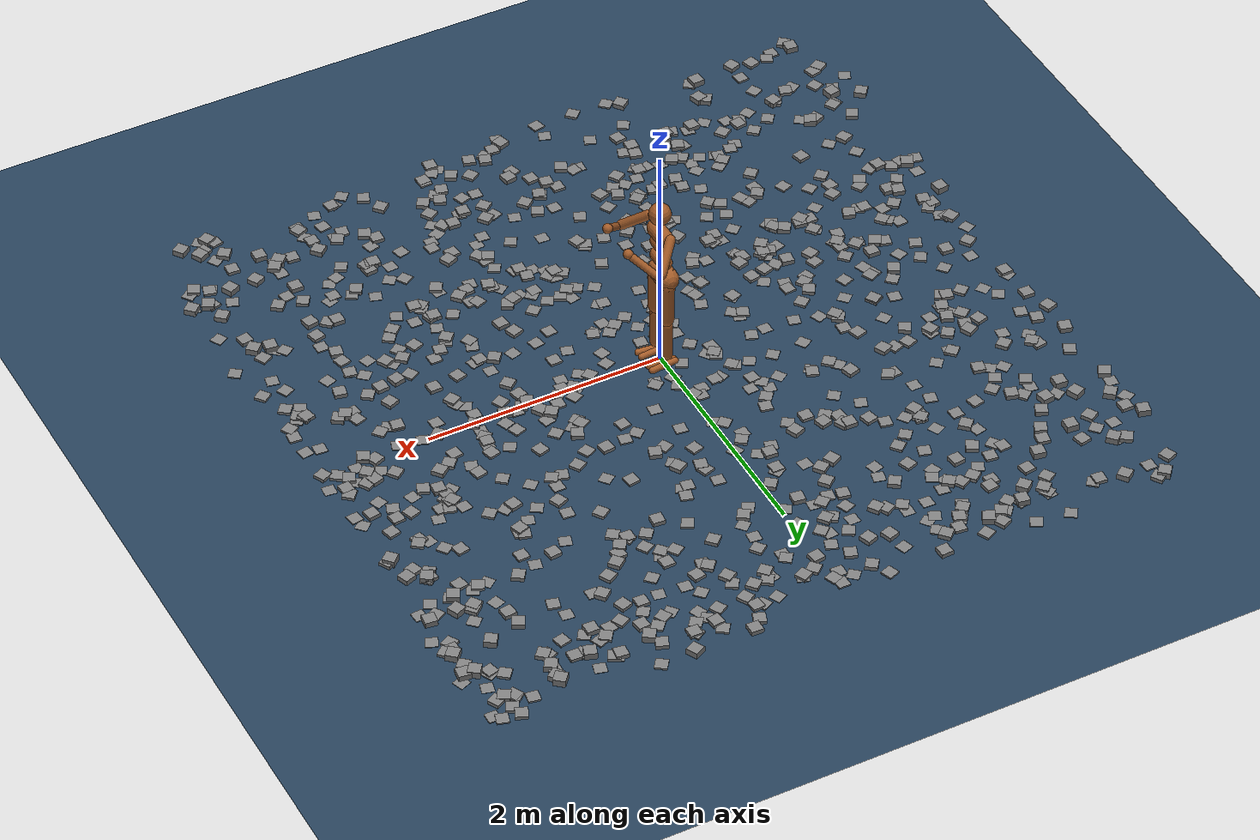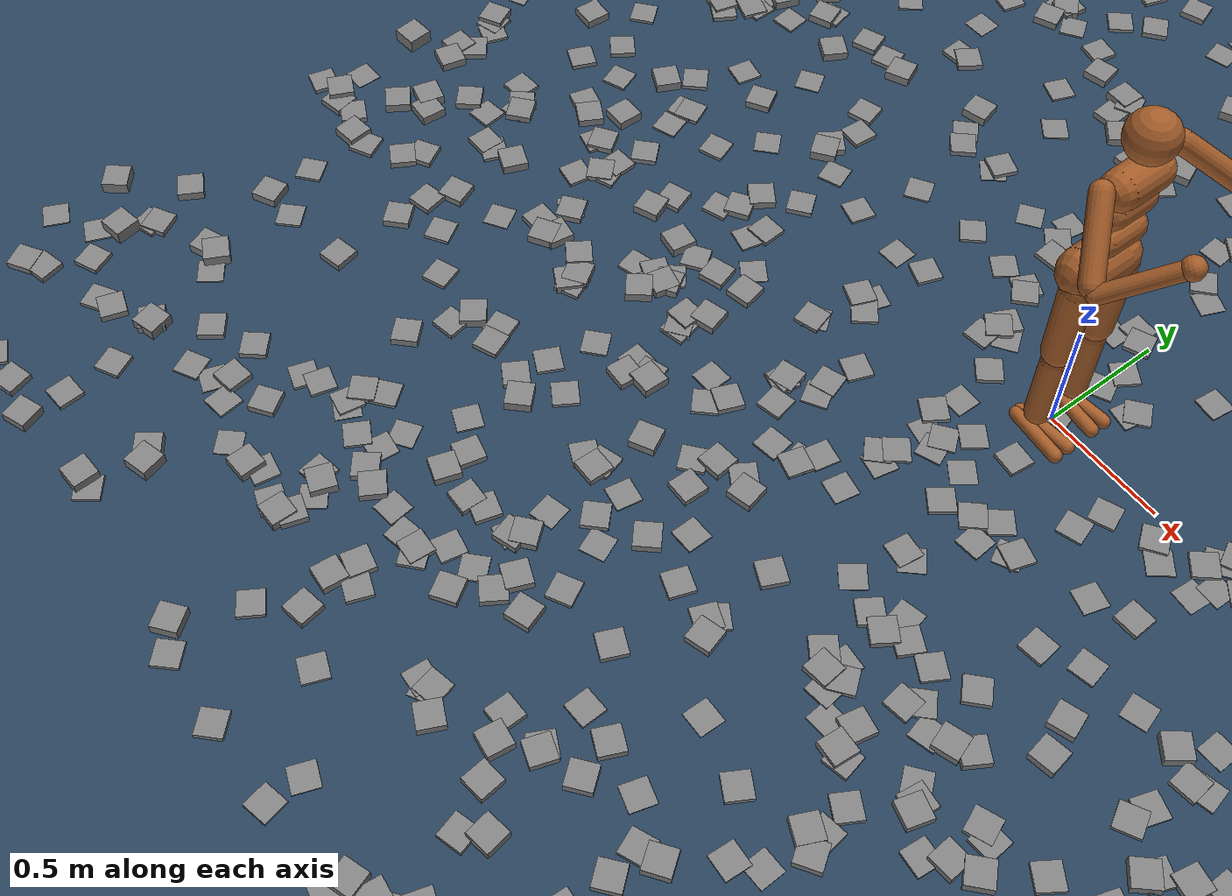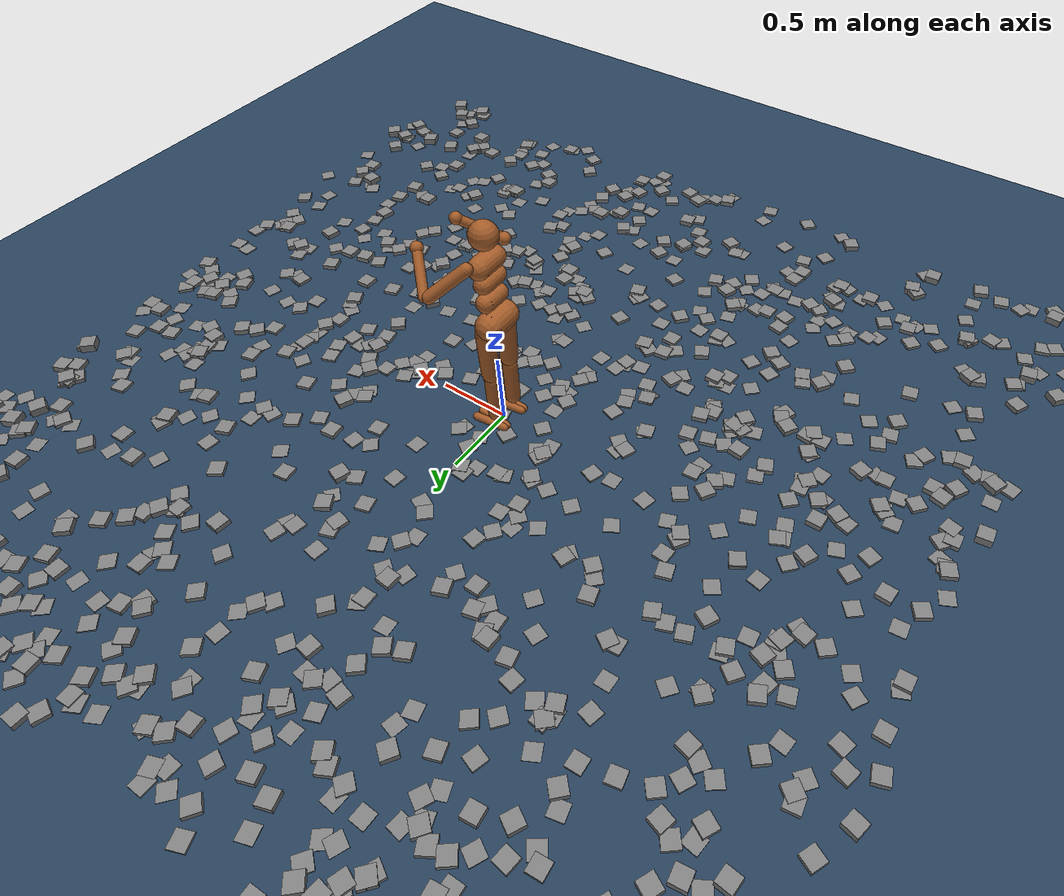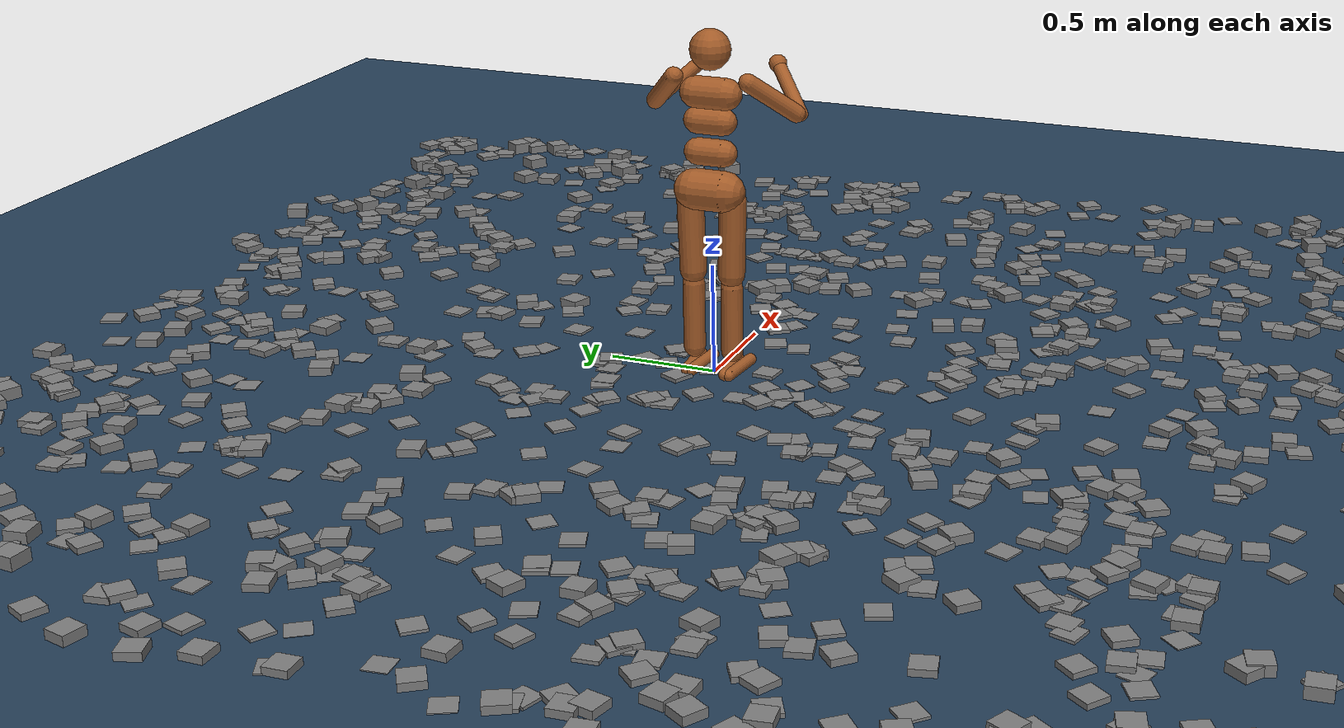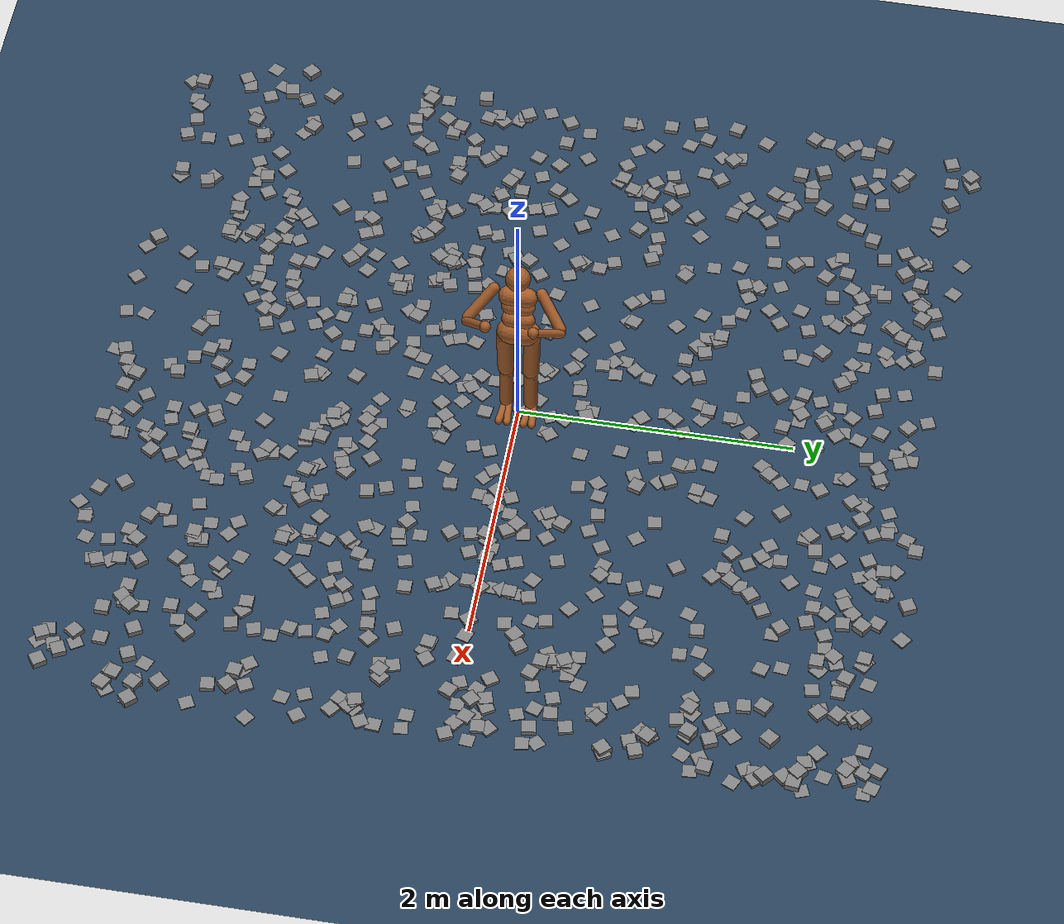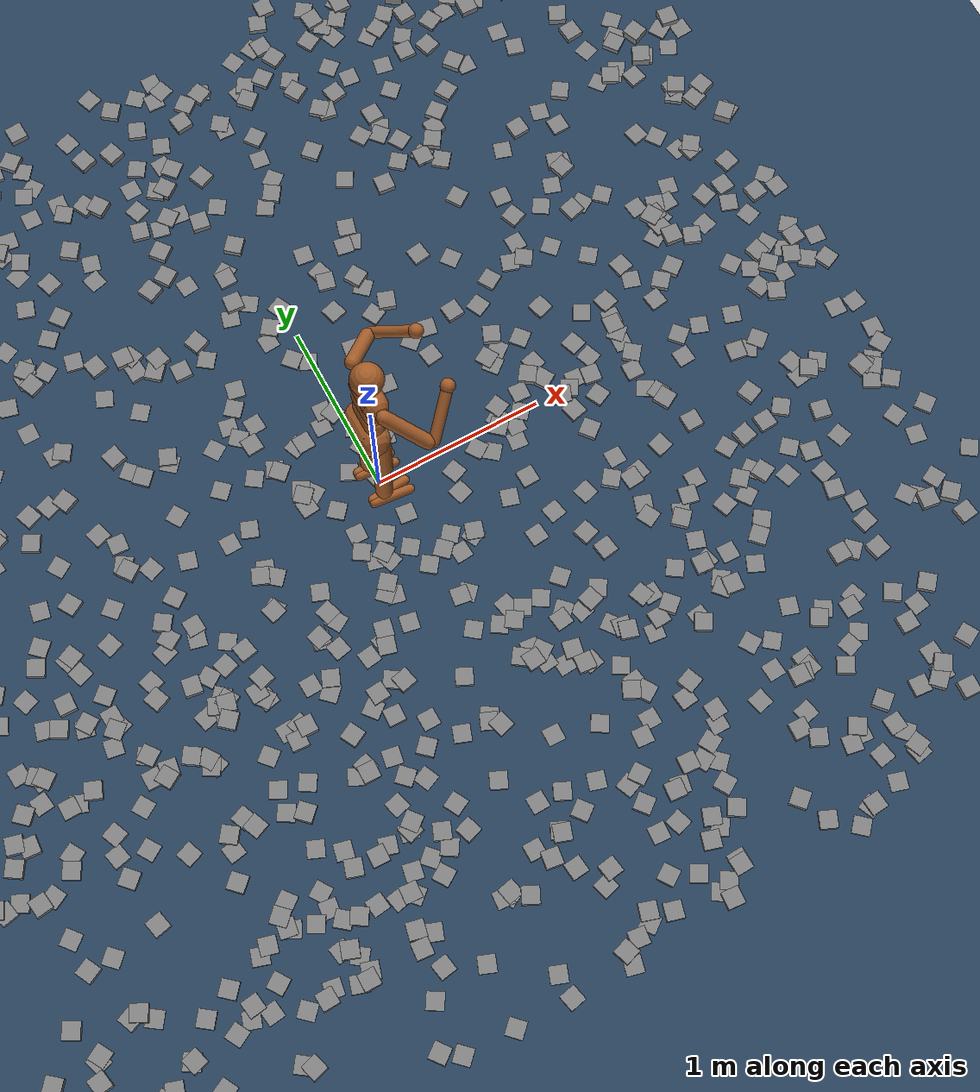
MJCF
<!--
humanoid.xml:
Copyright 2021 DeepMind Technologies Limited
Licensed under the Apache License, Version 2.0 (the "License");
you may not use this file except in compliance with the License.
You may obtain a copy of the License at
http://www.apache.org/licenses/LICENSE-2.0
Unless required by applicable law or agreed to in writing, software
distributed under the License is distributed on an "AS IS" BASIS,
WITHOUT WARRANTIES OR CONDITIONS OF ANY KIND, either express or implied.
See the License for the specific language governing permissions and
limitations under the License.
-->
<mujoco model="midphase">
  <include file="humanoid.xml"/>
  <compiler autolimits="true" boundmass="1e-05" boundinertia="1e-11" angle="radian" eulerseq="xyz"/>
  <option timestep="0.001" cone="elliptic" noslip_iterations="5" noslip_tolerance="0"/>
  <visual>
    <headlight ambient="0.4 0.4 0.4" diffuse="0.8 0.8 0.8" specular="0.1 0.1 0.1"/>
    <map znear="0.01"/>
    <scale forcewidth="0.01" contactwidth="0.059999999999999998" contactheight="0.01" jointwidth="0.01" framelength="0.29999999999999999" framewidth="0.01"/>
  </visual>
  <worldbody>
    <geom name="floor" size="0 0 .05" type="plane" material="grid" condim="3"/>
    <body>
      <geom name="box_1" type="box" size="0.05 0.05 0.0021314871261933462" pos="-2.7579238840899611 0.066618520140325543 0.0021314871261933462" euler="0 0 0.089539728943937719"/>
      <geom name="box_2" type="box" size="0.05 0.05 0.0055932598022792922" pos="-0.74195125085756208 -2.6293255815911882 0.0055932598022792922" euler="0 0 1.210988547159926"/>
      <geom name="box_3" type="box" size="0.05 0.05 0.0076431479752661451" pos="-1.8733782173454741 -0.57192101108242266 0.0076431479752661451" euler="0 0 0.37668922906788105"/>
      <geom name="box_4" type="box" size="0.05 0.05 0.0068584302548584187" pos="-0.39075822380038261 1.9800176817608275 0.0068584302548584187" euler="0 0 2.9304970501092895"/>
      <geom name="box_5" type="box" size="0.05 0.05 0.011352780476941039" pos="0.29288102356394852 1.2911361982345166 0.011352780476941039" euler="0 0 1.893636994119658"/>
      <geom name="box_6" type="box" size="0.05 0.05 0.0090259570070387179" pos="-0.45807120396657197 0.87536467839993648 0.0090259570070387179" euler="0 0 1.3747207682077196"/>
      <geom name="box_7" type="box" size="0.05 0.05 0.011049003475305186" pos="2.7819765630061752 -0.69935088704533399 0.011049003475305186" euler="0 0 2.4872775633035982"/>
      <geom name="box_8" type="box" size="0.05 0.05 0.0026554566943292734" pos="0.40826736656359408 2.5535798297559662 0.0026554566943292734" euler="0 0 0.22316635857445863"/>
      <geom name="box_9" type="box" size="0.05 0.05 0.026230352299157756" pos="-2.8786896153580459 1.9957190732876278 0.026230352299157756" euler="0 0 2.4446515321253526"/>
      <geom name="box_10" type="box" size="0.05 0.05 0.023635346112307207" pos="2.8717100533965843 1.794951385300342 0.023635346112307207" euler="0 0 1.4497801742371135"/>
      <geom name="box_11" type="box" size="0.05 0.05 0.018948709423942094" pos="-2.2903534447864007 0.8395261279651427 0.018948709423942094" euler="0 0 0.45035763459220635"/>
      <geom name="box_12" type="box" size="0.05 0.05 0.0079681032049079507" pos="0.13108993050042983 -0.51202836005685848 0.0079681032049079507" euler="0 0 0.83112596745384704"/>
      <geom name="box_13" type="box" size="0.05 0.05 0.0065587194736828943" pos="-0.26309800670070871 0.41060369321189105 0.0065587194736828943" euler="0 0 0.059029899013271603"/>
      <geom name="box_14" type="box" size="0.05 0.05 0.0071363826919313518" pos="0.67257433633452823 0.70160398124854151 0.0071363826919313518" euler="0 0 2.9648720303010268"/>
      <geom name="box_15" type="box" size="0.05 0.05 0.0015420292446634287" pos="-0.84295259655728394 -0.37780827720395127 0.0015420292446634287" euler="0 0 2.1916730400401567"/>
      <geom name="box_16" type="box" size="0.05 0.05 0.0034495996554422129" pos="1.0006002926740063 1.0238272177089565 0.0034495996554422129" euler="0 0 0.66093630831298456"/>
      <geom name="box_17" type="box" size="0.05 0.05 0.0093334287557840859" pos="-1.1074298944548968 -0.81773537434426435 0.0093334287557840859" euler="0 0 1.7913259850454366"/>
      <geom name="box_18" type="box" size="0.05 0.05 0.0056779760186648912" pos="2.9302430283553571 -2.3877311355118316 0.0056779760186648912" euler="0 0 0.65620568245319977"/>
      <geom name="box_19" type="box" size="0.05 0.05 0.0056440862480304516" pos="0.91864995279239059 -1.4802503847613073 0.0056440862480304516" euler="0 0 1.4649584982951505"/>
      <geom name="box_20" type="box" size="0.05 0.05 0.0050073055891098001" pos="-2.0461824981268819 -2.337749153014169 0.0050073055891098001" euler="0 0 2.061920216597708"/>
      <geom name="box_21" type="box" size="0.05 0.05 0.0028449242400681641" pos="-1.820505829919679 -0.78764897603421513 0.0028449242400681641" euler="0 0 2.5792262995372295"/>
      <geom name="box_22" type="box" size="0.05 0.05 0.014590884847783345" pos="2.0276694449928234 -2.4234095526362216 0.014590884847783345" euler="0 0 3.0676378818143037"/>
      <geom name="box_23" type="box" size="0.05 0.05 0.0017445680528320928" pos="2.860566529142023 0.6290731184702758 0.0017445680528320928" euler="0 0 2.3224650301041994"/>
      <geom name="box_24" type="box" size="0.05 0.05 0.0032558266601306371" pos="-1.3031582245415425 -2.2788206327209863 0.0032558266601306371" euler="0 0 0.93035186896820077"/>
      <geom name="box_25" type="box" size="0.05 0.05 0.014156970268030377" pos="-1.0921009236361439 -0.51442203291198041 0.014156970268030377" euler="0 0 0.20152530327551901"/>
      <geom name="box_26" type="box" size="0.05 0.05 0.0027848697044103917" pos="0.3996087252394509 -1.4076630543633275 0.0027848697044103917" euler="0 0 1.643832240776143"/>
      <geom name="box_27" type="box" size="0.05 0.05 0.01368079721930995" pos="0.45567897333707563 2.5757771854572846 0.01368079721930995" euler="0 0 1.0008138806828746"/>
      <geom name="box_28" type="box" size="0.05 0.05 0.0044806358781352192" pos="-2.2092128255736467 1.2979632247113937 0.0044806358781352192" euler="0 0 0.90919605550705185"/>
      <geom name="box_29" type="box" size="0.05 0.05 0.0010892140476583942" pos="0.51907760886049914 -2.8793547228750387 0.0010892140476583942" euler="0 0 2.6041919060557763"/>
      <geom name="box_30" type="box" size="0.05 0.05 0.019281582357231326" pos="1.0668992207773806 -1.3799521608470109 0.019281582357231326" euler="0 0 2.309680138863476"/>
      <geom name="box_31" type="box" size="0.05 0.05 0.011872786210026593" pos="-1.5074811388802518 0.45694400650702161 0.011872786210026593" euler="0 0 1.8599545819007226"/>
      <geom name="box_32" type="box" size="0.05 0.05 0.025545851501662706" pos="-1.6615102041562901 2.7164940691019099 0.025545851501662706" euler="0 0 1.404685804698693"/>
      <geom name="box_33" type="box" size="0.05 0.05 0.0085336090760927078" pos="1.1968756519050263 -1.215378294869198 0.0085336090760927078" euler="0 0 2.5566212518846934"/>
      <geom name="box_34" type="box" size="0.05 0.05 0.014158100211477551" pos="2.2866191826669695 0.48763723581515217 0.014158100211477551" euler="0 0 2.7700533352135435"/>
      <geom name="box_35" type="box" size="0.05 0.05 0.01323581378536311" pos="1.3515256789178434 0.0079462915602137585 0.01323581378536311" euler="0 0 3.0036253230639072"/>
      <geom name="box_36" type="box" size="0.05 0.05 0.0037141733500709443" pos="-0.45686970865092214 0.63835928476754589 0.0037141733500709443" euler="0 0 0.060297210807494242"/>
      <geom name="box_37" type="box" size="0.05 0.05 0.0091466053179695556" pos="0.96104122495611044 -1.2595343567373356 0.0091466053179695556" euler="0 0 1.9415527315479051"/>
      <geom name="box_38" type="box" size="0.05 0.05 0.012226582463715292" pos="-2.1871556146652988 -1.2103060442638154 0.012226582463715292" euler="0 0 1.7905975762630562"/>
      <geom name="box_39" type="box" size="0.05 0.05 0.009196950273245505" pos="0.44595149309747306 0.91920491914280156 0.009196950273245505" euler="0 0 2.0486428424191869"/>
      <geom name="box_40" type="box" size="0.05 0.05 0.01794654374529777" pos="2.379279575106378 -0.79462877971262103 0.01794654374529777" euler="0 0 1.3693100471719575"/>
      <geom name="box_41" type="box" size="0.05 0.05 0.018470169661148797" pos="1.8371639342765143 1.2233315012421979 0.018470169661148797" euler="0 0 0.31487205287249725"/>
      <geom name="box_42" type="box" size="0.05 0.05 0.026175655663678212" pos="1.285447797294669 2.9930820394071986 0.026175655663678212" euler="0 0 0.46950569600500242"/>
      <geom name="box_43" type="box" size="0.05 0.05 0.017112156357122453" pos="-2.0250423919417511 0.69335738570306482 0.017112156357122453" euler="0 0 0.38899194848741964"/>
      <geom name="box_44" type="box" size="0.05 0.05 0.0023141729136476226" pos="1.8439137523500637 0.41460443168756012 0.0023141729136476226" euler="0 0 1.2792040552296697"/>
      <geom name="box_45" type="box" size="0.05 0.05 0.017461264192643954" pos="1.1845726388673814 -0.27874390393158688 0.017461264192643954" euler="0 0 2.2684045667794193"/>
      <geom name="box_46" type="box" size="0.05 0.05 0.011439363869872553" pos="2.8531290300173149 2.1348200543556661 0.011439363869872553" euler="0 0 0.036800880819134574"/>
      <geom name="box_47" type="box" size="0.05 0.05 0.0020324217784458186" pos="1.3799433745443483 -1.9702219364313569 0.0020324217784458186" euler="0 0 1.6368847743022505"/>
      <geom name="box_48" type="box" size="0.05 0.05 0.0074938159537510235" pos="-1.8000208506215996 -2.8888692332363162 0.0074938159537510235" euler="0 0 2.4934748740387636"/>
      <geom name="box_49" type="box" size="0.05 0.05 0.0016049396610948491" pos="-0.92788991581858404 2.5684877607935448 0.0016049396610948491" euler="0 0 2.2129831101658186"/>
      <geom name="box_50" type="box" size="0.05 0.05 0.0055199636061156639" pos="-2.0118350610125235 0.72887040899858135 0.0055199636061156639" euler="0 0 1.8134170934008578"/>
      <geom name="box_51" type="box" size="0.05 0.05 0.012208289550736849" pos="2.6052839875487628 0.68379573579537567 0.012208289550736849" euler="0 0 1.6827400790049176"/>
      <geom name="box_52" type="box" size="0.05 0.05 0.0049870312305273206" pos="1.3807321771006178 -1.1283300271223888 0.0049870312305273206" euler="0 0 1.2510483635627982"/>
      <geom name="box_53" type="box" size="0.05 0.05 0.015223305449909446" pos="-1.882841964717983 2.6662343399036015 0.015223305449909446" euler="0 0 2.3233673446833327"/>
      <geom name="box_54" type="box" size="0.05 0.05 0.0092539158856042962" pos="-1.6355122321600606 -1.4738611093776424 0.0092539158856042962" euler="0 0 0.18230398376747195"/>
      <geom name="box_55" type="box" size="0.05 0.05 0.0044124698736330613" pos="-1.1292247080353846 1.1780609328927572 0.0044124698736330613" euler="0 0 1.1867424032012901"/>
      <geom name="box_56" type="box" size="0.05 0.05 0.014157208492125314" pos="-2.8519276296520126 -2.5965022112205087 0.014157208492125314" euler="0 0 2.1343753461250934"/>
      <geom name="box_57" type="box" size="0.05 0.05 0.0051210427035710045" pos="0.21947526665233319 2.3800277582420524 0.0051210427035710045" euler="0 0 3.1112415617053348"/>
      <geom name="box_58" type="box" size="0.05 0.05 0.015409194422886689" pos="0.97846921860060476 -1.4200657395770961 0.015409194422886689" euler="0 0 0.064877028210819962"/>
      <geom name="box_59" type="box" size="0.05 0.05 0.01678992064948762" pos="-1.0798970950651929 -0.69921663496861219 0.01678992064948762" euler="0 0 1.8482527219211597"/>
      <geom name="box_60" type="box" size="0.05 0.05 0.01616288984433871" pos="0.77389106154689236 2.2359039326843719 0.01616288984433871" euler="0 0 0.85935764702480477"/>
      <geom name="box_61" type="box" size="0.05 0.05 0.0072497226362931945" pos="-1.8861843341642868 2.716749941831667 0.0072497226362931945" euler="0 0 2.1598081185290696"/>
      <geom name="box_62" type="box" size="0.05 0.05 0.0071860473436569771" pos="2.6842235429335455 1.3851348406209469 0.0071860473436569771" euler="0 0 0.797781198817058"/>
      <geom name="box_63" type="box" size="0.05 0.05 0.0090690239062786171" pos="0.10920428358397949 -2.8460236916728103 0.0090690239062786171" euler="0 0 0.65178646484550951"/>
      <geom name="box_64" type="box" size="0.05 0.05 0.0062810591181235199" pos="-0.7549801179946467 -0.21854745381113583 0.0062810591181235199" euler="0 0 0.87219630412116811"/>
      <geom name="box_65" type="box" size="0.05 0.05 0.0048299750840094455" pos="2.183133635539388 -2.2948088642278015 0.0048299750840094455" euler="0 0 1.6253944021562114"/>
      <geom name="box_66" type="box" size="0.05 0.05 0.0044823168880674938" pos="1.3011580871555619 -0.62364178315623775 0.0044823168880674938" euler="0 0 1.7763234395177951"/>
      <geom name="box_67" type="box" size="0.05 0.05 0.018868206959803447" pos="-2.1309134439397366 -0.071662316106272606 0.018868206959803447" euler="0 0 1.1171903647523735"/>
      <geom name="box_68" type="box" size="0.05 0.05 0.0025850262733983524" pos="1.5919515228417911 1.4919817191032836 0.0025850262733983524" euler="0 0 2.8391192952899043"/>
      <geom name="box_69" type="box" size="0.05 0.05 0.0036293277411329401" pos="0.31315481953443935 0.50685641373461321 0.0036293277411329401" euler="0 0 3.022012260064745"/>
      <geom name="box_70" type="box" size="0.05 0.05 0.01866105701905162" pos="-1.5550273205073191 -2.3982363464070131 0.01866105701905162" euler="0 0 0.051615203625776832"/>
      <geom name="box_71" type="box" size="0.05 0.05 0.012141793157540208" pos="1.0194992795454603 1.7109174721388261 0.012141793157540208" euler="0 0 0.88508123053168197"/>
      <geom name="box_72" type="box" size="0.05 0.05 0.017653599661015224" pos="-2.6162684032741135 -0.08623442439226281 0.017653599661015224" euler="0 0 3.0708915499408822"/>
      <geom name="box_73" type="box" size="0.05 0.05 0.019037057625897948" pos="-0.97104628897892642 2.7694209272489907 0.019037057625897948" euler="0 0 0.72791212754674239"/>
      <geom name="box_74" type="box" size="0.05 0.05 0.026354351032123462" pos="2.6482662282389917 1.7952155241143499 0.026354351032123462" euler="0 0 1.9806106069315528"/>
      <geom name="box_75" type="box" size="0.05 0.05 0.0012515002974190902" pos="-1.2418782929532197 2.0936613318775095 0.0012515002974190902" euler="0 0 1.9411168761524566"/>
      <geom name="box_76" type="box" size="0.05 0.05 0.010089035833759773" pos="-0.91659889240668235 -2.1111548343110096 0.010089035833759773" euler="0 0 3.0845079981315733"/>
      <geom name="box_77" type="box" size="0.05 0.05 0.0022321024451703907" pos="-0.015651807008024043 0.8368350983923416 0.0022321024451703907" euler="0 0 1.1579426908430939"/>
      <geom name="box_78" type="box" size="0.05 0.05 0.0052620235505200456" pos="1.9327063991654736 -1.8609125285834522 0.0052620235505200456" euler="0 0 1.6063559592089538"/>
      <geom name="box_79" type="box" size="0.05 0.05 0.028864205083827005" pos="-2.4129330930357957 2.1731491045300997 0.028864205083827005" euler="0 0 3.0565167192494016"/>
      <geom name="box_80" type="box" size="0.05 0.05 0.0025409264097719384" pos="2.4393329953270735 1.6442839961918327 0.0025409264097719384" euler="0 0 1.0466063621922361"/>
      <geom name="box_81" type="box" size="0.05 0.05 0.0020151164539496799" pos="-0.55655297151715599 -1.6065951469743436 0.0020151164539496799" euler="0 0 0.41622218004716705"/>
      <geom name="box_82" type="box" size="0.05 0.05 0.0052614527166108763" pos="1.3535661852634728 -2.9314352482498141 0.0052614527166108763" euler="0 0 2.420850818494046"/>
      <geom name="box_83" type="box" size="0.05 0.05 0.0081156490857324966" pos="-2.5228675044794655 -2.4623817945683677 0.0081156490857324966" euler="0 0 2.1113004544441862"/>
      <geom name="box_84" type="box" size="0.05 0.05 0.0075433983644019554" pos="-0.47676319991940908 0.34421274794350154 0.0075433983644019554" euler="0 0 2.7035012457386114"/>
      <geom name="box_85" type="box" size="0.05 0.05 0.0067303740551379072" pos="-1.3780325685677122 -2.2111032042532344 0.0067303740551379072" euler="0 0 0.17396355823276272"/>
      <geom name="box_86" type="box" size="0.05 0.05 0.014216883467138286" pos="-1.4272911045619305 -0.26315659919712209 0.014216883467138286" euler="0 0 2.1465916240916152"/>
      <geom name="box_87" type="box" size="0.05 0.05 0.015982364733823855" pos="-1.2988869205070002 -0.72043826459927729 0.015982364733823855" euler="0 0 0.56910253058338034"/>
      <geom name="box_88" type="box" size="0.05 0.05 0.015770743675126309" pos="-2.658911541400558 1.1819834503499242 0.015770743675126309" euler="0 0 2.4463437352727655"/>
      <geom name="box_89" type="box" size="0.05 0.05 0.0061836161460648732" pos="-1.4434646139278704 -0.75712117240463161 0.0061836161460648732" euler="0 0 1.8459986971850182"/>
      <geom name="box_90" type="box" size="0.05 0.05 0.0018476337238281675" pos="-0.77488320469266769 -1.8176743188861622 0.0018476337238281675" euler="0 0 1.4446798661179148"/>
      <geom name="box_91" type="box" size="0.05 0.05 0.0098974928868106882" pos="1.7987753074237078 -2.5382613180802034 0.0098974928868106882" euler="0 0 1.6299686919932892"/>
      <geom name="box_92" type="box" size="0.05 0.05 0.0016718862793543275" pos="0.46525769298825281 2.7566000450005506 0.0016718862793543275" euler="0 0 2.0281187373591485"/>
      <geom name="box_93" type="box" size="0.05 0.05 0.0071325325954345415" pos="-0.41758536295163262 0.060101113909501347 0.0071325325954345415" euler="0 0 1.684451278380545"/>
      <geom name="box_94" type="box" size="0.05 0.05 0.019171708733123027" pos="-1.3344234136094035 -2.2268366072020789 0.019171708733123027" euler="0 0 1.2336270206837534"/>
      <geom name="box_95" type="box" size="0.05 0.05 0.014250431227727206" pos="-1.8772146494949316 2.4239037295694219 0.014250431227727206" euler="0 0 1.7084167777413461"/>
      <geom name="box_96" type="box" size="0.05 0.05 0.0085814811123589383" pos="2.2922484613793372 -0.24837622938848458 0.0085814811123589383" euler="0 0 2.2750397271463072"/>
      <geom name="box_97" type="box" size="0.05 0.05 0.0072266876295852588" pos="2.4242663574057461 1.1401501211473644 0.0072266876295852588" euler="0 0 2.1979275059228232"/>
      <geom name="box_98" type="box" size="0.05 0.05 0.0040502376272198715" pos="1.5406718564213353 0.81636633268284786 0.0040502376272198715" euler="0 0 0.75404592756230926"/>
      <geom name="box_99" type="box" size="0.05 0.05 0.018138540794386863" pos="1.7783488471039899 2.7549996182113352 0.018138540794386863" euler="0 0 1.4392855740443939"/>
      <geom name="box_100" type="box" size="0.05 0.05 0.011939272078852575" pos="2.146335865161328 -0.25665927987685766 0.011939272078852575" euler="0 0 2.9904018635573517"/>
      <geom name="box_101" type="box" size="0.05 0.05 0.005623019440019722" pos="1.9246027242078902 2.4530623104764304 0.005623019440019722" euler="0 0 2.5620436378708296"/>
      <geom name="box_102" type="box" size="0.05 0.05 0.0048162902670085776" pos="0.77339063437020261 -0.60939444828193778 0.0048162902670085776" euler="0 0 0.19701854936147201"/>
      <geom name="box_103" type="box" size="0.05 0.05 0.019220671715405997" pos="-1.4478955986635538 2.0942298505710646 0.019220671715405997" euler="0 0 0.10462957008965236"/>
      <geom name="box_104" type="box" size="0.05 0.05 0.0045194141794874946" pos="-0.86778690916842205 -0.85975865758474246 0.0045194141794874946" euler="0 0 0.051297504075257933"/>
      <geom name="box_105" type="box" size="0.05 0.05 0.01896072913610251" pos="-0.59244299517834786 2.5757485038162837 0.01896072913610251" euler="0 0 0.31294953297100586"/>
      <geom name="box_106" type="box" size="0.05 0.05 0.0054221384563020803" pos="2.2169311832797938 -0.27502561855468954 0.0054221384563020803" euler="0 0 1.0263610900844733"/>
      <geom name="box_107" type="box" size="0.05 0.05 0.0091471187274665203" pos="0.68678823886124629 -2.801552451146966 0.0091471187274665203" euler="0 0 0.049027897417604382"/>
      <geom name="box_108" type="box" size="0.05 0.05 0.0058106326807341865" pos="-2.591555556151679 -1.4883540705234426 0.0058106326807341865" euler="0 0 0.69479750691245112"/>
      <geom name="box_109" type="box" size="0.05 0.05 0.01893592752586969" pos="-2.2136686127084535 -2.9277826626140744 0.01893592752586969" euler="0 0 0.36280461949607173"/>
      <geom name="box_110" type="box" size="0.05 0.05 0.0057256783553515551" pos="2.8455372769083018 2.9420700093653629 0.0057256783553515551" euler="0 0 1.285081340944829"/>
      <geom name="box_111" type="box" size="0.05 0.05 0.001587737864366022" pos="0.83257054419917598 -0.058167920707576926 0.001587737864366022" euler="0 0 3.1083224877066833"/>
      <geom name="box_112" type="box" size="0.05 0.05 0.013587586859120843" pos="1.6994066298828789 -1.2696090160110365 0.013587586859120843" euler="0 0 0.75843896327235016"/>
      <geom name="box_113" type="box" size="0.05 0.05 0.009057690780281135" pos="-1.5236208900542132 0.99515470535512618 0.009057690780281135" euler="0 0 1.6251726372821396"/>
      <geom name="box_114" type="box" size="0.05 0.05 0.0088822805173377171" pos="0.32812685196851366 -1.2776908804822216 0.0088822805173377171" euler="0 0 2.2197699064395566"/>
      <geom name="box_115" type="box" size="0.05 0.05 0.0018741389068586416" pos="-0.83672663708464645 1.9719414873344263 0.0018741389068586416" euler="0 0 2.9058692554057854"/>
      <geom name="box_116" type="box" size="0.05 0.05 0.019724337125222653" pos="-1.6042380430214069 -0.90888378304462059 0.019724337125222653" euler="0 0 2.5602927045115069"/>
      <geom name="box_117" type="box" size="0.05 0.05 0.029768326059019749" pos="2.8138302280221108 2.429690073299561 0.029768326059019749" euler="0 0 0.93165898370118372"/>
      <geom name="box_118" type="box" size="0.05 0.05 0.0054349848538938301" pos="-1.5034797536612927 -2.3645630707066068 0.0054349848538938301" euler="0 0 2.9875057368036577"/>
      <geom name="box_119" type="box" size="0.05 0.05 0.017752684034342953" pos="1.138609590466503 -2.649861846116468 0.017752684034342953" euler="0 0 2.2955903377300952"/>
      <geom name="box_120" type="box" size="0.05 0.05 0.01522697689326253" pos="-1.365378627204225 -0.72565862353542876 0.01522697689326253" euler="0 0 1.1758861397876883"/>
      <geom name="box_121" type="box" size="0.05 0.05 0.0067848997401690706" pos="-1.5731565447657669 -1.9688814057141419 0.0067848997401690706" euler="0 0 1.4114913428366442"/>
      <geom name="box_122" type="box" size="0.05 0.05 0.018909088394260677" pos="2.0351347335519145 -1.5735490439061675 0.018909088394260677" euler="0 0 1.5783030288892255"/>
      <geom name="box_123" type="box" size="0.05 0.05 0.015264532375840686" pos="0.80398618646796471 2.2037364327747886 0.015264532375840686" euler="0 0 2.9537558529108785"/>
      <geom name="box_124" type="box" size="0.05 0.05 0.014102828797423028" pos="1.1974503613485084 2.8077933996253623 0.014102828797423028" euler="0 0 3.1240022154810387"/>
      <geom name="box_125" type="box" size="0.05 0.05 0.0089322411211242257" pos="-2.5747813308947496 -1.2432358113568869 0.0089322411211242257" euler="0 0 0.47863642412840907"/>
      <geom name="box_126" type="box" size="0.05 0.05 0.018012331801475989" pos="-2.2122640291604636 0.62470682412529221 0.018012331801475989" euler="0 0 1.2026269863852814"/>
      <geom name="box_127" type="box" size="0.05 0.05 0.012252377956474898" pos="2.8067680307910114 0.28130941001653298 0.012252377956474898" euler="0 0 0.86338370812936271"/>
      <geom name="box_128" type="box" size="0.05 0.05 0.0061614025845167716" pos="2.3805669493464592 -0.55959992498551037 0.0061614025845167716" euler="0 0 1.7344050582620087"/>
      <geom name="box_129" type="box" size="0.05 0.05 0.0055527974544277757" pos="-0.26733510329983812 -0.58971878772240816 0.0055527974544277757" euler="0 0 0.78041391695744633"/>
      <geom name="box_130" type="box" size="0.05 0.05 0.015261305435650761" pos="-1.1377150441211314 -0.76179081671551518 0.015261305435650761" euler="0 0 1.6492432847377814"/>
      <geom name="box_131" type="box" size="0.05 0.05 0.0019251156235350424" pos="-0.99895520525234804 2.5449525997245814 0.0019251156235350424" euler="0 0 2.7090536117938968"/>
      <geom name="box_132" type="box" size="0.05 0.05 0.007621043791636444" pos="-1.4781448544590634 -0.32318692404478844 0.007621043791636444" euler="0 0 0.32869820663396682"/>
      <geom name="box_133" type="box" size="0.05 0.05 0.014500039651724566" pos="1.4405851537060954 1.0830868868569556 0.014500039651724566" euler="0 0 1.9552783484916423"/>
      <geom name="box_134" type="box" size="0.05 0.05 0.017705460497595214" pos="-1.7704578782417895 -0.94981131081160708 0.017705460497595214" euler="0 0 2.1244784143682032"/>
      <geom name="box_135" type="box" size="0.05 0.05 0.014496399750510054" pos="0.26206832296857119 -1.3038020943267803 0.014496399750510054" euler="0 0 0.094986864430986889"/>
      <geom name="box_136" type="box" size="0.05 0.05 0.027741232391248597" pos="-2.9526953789493575 -0.76392558107402664 0.027741232391248597" euler="0 0 1.666731815726427"/>
      <geom name="box_137" type="box" size="0.05 0.05 0.0075096087024902163" pos="-2.4630327298025994 -0.56434606819029742 0.0075096087024902163" euler="0 0 0.076382169594693142"/>
      <geom name="box_138" type="box" size="0.05 0.05 0.0031983614332147794" pos="0.7333863530387692 -1.3255923106284098 0.0031983614332147794" euler="0 0 0.65894890092897218"/>
      <geom name="box_139" type="box" size="0.05 0.05 0.019028359393689642" pos="0.46284146412205107 1.1716200354281163 0.019028359393689642" euler="0 0 2.1110156164230394"/>
      <geom name="box_140" type="box" size="0.05 0.05 0.018073448689138356" pos="-2.983780716638984 0.88317992336421636 0.018073448689138356" euler="0 0 1.8861878413382858"/>
      <geom name="box_141" type="box" size="0.05 0.05 0.024596680841354038" pos="2.7766219190414549 -2.898769959779762 0.024596680841354038" euler="0 0 2.1880640876460378"/>
      <geom name="box_142" type="box" size="0.05 0.05 0.0018751863306918221" pos="0.058843179729504591 -0.99621078241914507 0.0018751863306918221" euler="0 0 2.4844976469589679"/>
      <geom name="box_143" type="box" size="0.05 0.05 0.0018179715882916852" pos="-0.34778617362044839 0.11971424742502901 0.0018179715882916852" euler="0 0 2.1801283625035142"/>
      <geom name="box_144" type="box" size="0.05 0.05 0.017852254843130935" pos="-1.6334429907728343 -0.53819062385924621 0.017852254843130935" euler="0 0 1.9581379657816946"/>
      <geom name="box_145" type="box" size="0.05 0.05 0.017563928960354365" pos="0.7129570094482589 -2.1992311743903934 0.017563928960354365" euler="0 0 3.0805833414206303"/>
      <geom name="box_146" type="box" size="0.05 0.05 0.018542815289894099" pos="0.016324566871944057 2.5340878907797979 0.018542815289894099" euler="0 0 1.7007979244620286"/>
      <geom name="box_147" type="box" size="0.05 0.05 0.0020449807054285151" pos="1.9793842116200588 2.809718461765784 0.0020449807054285151" euler="0 0 2.8895829212388331"/>
      <geom name="box_148" type="box" size="0.05 0.05 0.006700549470042662" pos="-1.9513679750343602 -0.66519193739288518 0.006700549470042662" euler="0 0 2.9912445029924641"/>
      <geom name="box_149" type="box" size="0.05 0.05 0.027328392236275454" pos="-2.037194136674394 2.3178279965193589 0.027328392236275454" euler="0 0 1.4023894162855401"/>
      <geom name="box_150" type="box" size="0.05 0.05 0.0024532486115754226" pos="-2.0386172020791404 0.96670506904859721 0.0024532486115754226" euler="0 0 1.383129371531004"/>
      <geom name="box_151" type="box" size="0.05 0.05 0.0021389416667418918" pos="1.1787788679150033 -1.5156074667650778 0.0021389416667418918" euler="0 0 0.12445583470393345"/>
      <geom name="box_152" type="box" size="0.05 0.05 0.027043808359198316" pos="-2.6335287775992757 2.4463977449102368 0.027043808359198316" euler="0 0 2.3244138807611381"/>
      <geom name="box_153" type="box" size="0.05 0.05 0.019961282775244796" pos="1.0354938677791283 0.17363957418529896 0.019961282775244796" euler="0 0 0.95644646164584501"/>
      <geom name="box_154" type="box" size="0.05 0.05 0.0098157423640191296" pos="-0.82686564636366366 -0.17610630471654254 0.0098157423640191296" euler="0 0 1.1882922627953336"/>
      <geom name="box_155" type="box" size="0.05 0.05 0.0022009447484339821" pos="-1.9520496876299653 -1.032071994551522 0.0022009447484339821" euler="0 0 2.1373783710323444"/>
      <geom name="box_156" type="box" size="0.05 0.05 0.0031457195283165224" pos="0.64349624406924599 -0.13412098274150352 0.0031457195283165224" euler="0 0 0.89221224061548876"/>
      <geom name="box_157" type="box" size="0.05 0.05 0.0040372964358781592" pos="0.087076459792540639 -0.79243451677775223 0.0040372964358781592" euler="0 0 1.4341995366083693"/>
      <geom name="box_158" type="box" size="0.05 0.05 0.010958360134936566" pos="2.822962161575866 -2.1993634095263759 0.010958360134936566" euler="0 0 0.30411858814363069"/>
      <geom name="box_159" type="box" size="0.05 0.05 0.019986281884521249" pos="0.54616140522294732 0.95505883110016931 0.019986281884521249" euler="0 0 1.2480188784920987"/>
      <geom name="box_160" type="box" size="0.05 0.05 0.016448023401701751" pos="-0.88864202284174443 1.3284400077597152 0.016448023401701751" euler="0 0 2.0030251091939242"/>
      <geom name="box_161" type="box" size="0.05 0.05 0.021249205856730426" pos="2.8573539807229196 2.3387619386732412 0.021249205856730426" euler="0 0 2.401942281856285"/>
      <geom name="box_162" type="box" size="0.05 0.05 0.0055961323798282116" pos="-0.98701098194460224 -2.1138865307597561 0.0055961323798282116" euler="0 0 0.19677680706292616"/>
      <geom name="box_163" type="box" size="0.05 0.05 0.0096286683075093374" pos="-0.40631111291220812 0.13197764177989502 0.0096286683075093374" euler="0 0 2.4287136140298724"/>
      <geom name="box_164" type="box" size="0.05 0.05 0.022616544144471496" pos="-2.2960771176911337 -2.3579751588372506 0.022616544144471496" euler="0 0 1.852580609680039"/>
      <geom name="box_165" type="box" size="0.05 0.05 0.01259424907451125" pos="2.088902282081909 2.6149924813007317 0.01259424907451125" euler="0 0 3.089524658033449"/>
      <geom name="box_166" type="box" size="0.05 0.05 0.013478477210375903" pos="-0.71798889883456152 -2.1131479398163657 0.013478477210375903" euler="0 0 2.151785000758919"/>
      <geom name="box_167" type="box" size="0.05 0.05 0.017851375960489829" pos="2.1723755751072433 -2.4164520312741562 0.017851375960489829" euler="0 0 1.5638122767507374"/>
      <geom name="box_168" type="box" size="0.05 0.05 0.0021121635224756168" pos="-1.5506577597604896 -1.9858475632250323 0.0021121635224756168" euler="0 0 2.7004528408624524"/>
      <geom name="box_169" type="box" size="0.05 0.05 0.019619284200503878" pos="-0.17627457649156275 -2.3049959921946881 0.019619284200503878" euler="0 0 1.4358924468574743"/>
      <geom name="box_170" type="box" size="0.05 0.05 0.0061537894584754189" pos="-0.45776187926716316 2.1427495050274041 0.0061537894584754189" euler="0 0 0.3685577145896638"/>
      <geom name="box_171" type="box" size="0.05 0.05 0.0041024631463795688" pos="-0.57724355599599297 -0.60112715994401533 0.0041024631463795688" euler="0 0 2.1092134043317126"/>
      <geom name="box_172" type="box" size="0.05 0.05 0.0092034424254320672" pos="1.2826012104600979 0.8351213953523553 0.0092034424254320672" euler="0 0 1.2540017215308834"/>
      <geom name="box_173" type="box" size="0.05 0.05 0.013415002061159101" pos="0.68716619886192465 -2.5797468591321322 0.013415002061159101" euler="0 0 2.5836669674809798"/>
      <geom name="box_174" type="box" size="0.05 0.05 0.0086956766526420474" pos="1.3580547865070116 0.22153800649434263 0.0086956766526420474" euler="0 0 0.34707408028148945"/>
      <geom name="box_175" type="box" size="0.05 0.05 0.01500783060933307" pos="-0.56775850290866359 -1.0737420597406986 0.01500783060933307" euler="0 0 0.094091720693388003"/>
      <geom name="box_176" type="box" size="0.05 0.05 0.0130609401357402" pos="-2.3412932516249958 0.637848798270511 0.0130609401357402" euler="0 0 2.2092229207772114"/>
      <geom name="box_177" type="box" size="0.05 0.05 0.0018465168106184843" pos="2.7548535118678501 -2.3802110694891683 0.0018465168106184843" euler="0 0 2.7242859764792251"/>
      <geom name="box_178" type="box" size="0.05 0.05 0.0042858988935400889" pos="0.20950112956250377 -0.57453829236444731 0.0042858988935400889" euler="0 0 1.6467721649433684"/>
      <geom name="box_179" type="box" size="0.05 0.05 0.025440529017860425" pos="-1.8565985103595917 -2.8852626153078615 0.025440529017860425" euler="0 0 1.6278156484652724"/>
      <geom name="box_180" type="box" size="0.05 0.05 0.0026209075392553639" pos="-0.76070426553123482 -1.6628170919101186 0.0026209075392553639" euler="0 0 0.25299875048601306"/>
      <geom name="box_181" type="box" size="0.05 0.05 0.0022568397802221396" pos="-1.6716213222433667 -2.3999156344706689 0.0022568397802221396" euler="0 0 0.83264676929151149"/>
      <geom name="box_182" type="box" size="0.05 0.05 0.017230789768879991" pos="-2.6063707967404461 2.1376570777366917 0.017230789768879991" euler="0 0 0.50931582004093245"/>
      <geom name="box_183" type="box" size="0.05 0.05 0.0047923267002821721" pos="1.6407332666941832 -0.26154260796560003 0.0047923267002821721" euler="0 0 0.48182253997223079"/>
      <geom name="box_184" type="box" size="0.05 0.05 0.0080333164021119535" pos="-0.40209476231291585 0.16940453507121456 0.0080333164021119535" euler="0 0 1.097799054367949"/>
      <geom name="box_185" type="box" size="0.05 0.05 0.018018134532993866" pos="1.5061298931383904 2.5632708442387075 0.018018134532993866" euler="0 0 0.090957115325797547"/>
      <geom name="box_186" type="box" size="0.05 0.05 0.019759626384405395" pos="-0.64458726922709353 2.2702349722799644 0.019759626384405395" euler="0 0 2.170164377985023"/>
      <geom name="box_187" type="box" size="0.05 0.05 0.0081513939486926729" pos="1.5556947103000081 -0.81273224401928035 0.0081513939486926729" euler="0 0 1.57413638276205"/>
      <geom name="box_188" type="box" size="0.05 0.05 0.013953058956317863" pos="-0.81052898387257155 -1.4345730037136415 0.013953058956317863" euler="0 0 1.5581366363440519"/>
      <geom name="box_189" type="box" size="0.05 0.05 0.0040370604502296351" pos="-1.3359583721685389 0.14627886646331989 0.0040370604502296351" euler="0 0 0.36876106984243123"/>
      <geom name="box_190" type="box" size="0.05 0.05 0.0061788190736720323" pos="-2.7191618717268673 2.824388656623797 0.0061788190736720323" euler="0 0 0.012127651944910519"/>
      <geom name="box_191" type="box" size="0.05 0.05 0.014672782999003476" pos="0.6772005187019543 -2.511782406880168 0.014672782999003476" euler="0 0 2.7705595753555365"/>
      <geom name="box_192" type="box" size="0.05 0.05 0.011440510883110155" pos="2.7983398286273609 0.045813283444589459 0.011440510883110155" euler="0 0 0.94374600412201926"/>
      <geom name="box_193" type="box" size="0.05 0.05 0.017670576994308275" pos="2.5849123037878385 0.12456862345116315 0.017670576994308275" euler="0 0 0.83945564828619401"/>
      <geom name="box_194" type="box" size="0.05 0.05 0.010228771766134809" pos="-0.7684875089252321 -2.9916999000060054 0.010228771766134809" euler="0 0 0.77812544706608244"/>
      <geom name="box_195" type="box" size="0.05 0.05 0.0073859430615978603" pos="2.1526648093914131 -0.24898099760132997 0.0073859430615978603" euler="0 0 1.3967121572673935"/>
      <geom name="box_196" type="box" size="0.05 0.05 0.011925496741868616" pos="2.2840687382824774 2.6701606616423481 0.011925496741868616" euler="0 0 3.1161153712389456"/>
      <geom name="box_197" type="box" size="0.05 0.05 0.0081017949031828816" pos="2.796884673763028 1.751277417785408 0.0081017949031828816" euler="0 0 2.1227400623495778"/>
      <geom name="box_198" type="box" size="0.05 0.05 0.0065874565852801562" pos="-1.7012564343347412 -2.0037130528725262 0.0065874565852801562" euler="0 0 2.898925387735428"/>
      <geom name="box_199" type="box" size="0.05 0.05 0.0085981146539772183" pos="-0.28143452730672935 -0.036252996076659105 0.0085981146539772183" euler="0 0 2.4446981674987671"/>
      <geom name="box_200" type="box" size="0.05 0.05 0.016542632809360931" pos="-2.1655637931083231 -0.43857383873355804 0.016542632809360931" euler="0 0 2.6479067236661211"/>
      <geom name="box_201" type="box" size="0.05 0.05 0.0031854130034168694" pos="-2.3855174492855014 -2.0616999067922217 0.0031854130034168694" euler="0 0 0.95566837476032673"/>
      <geom name="box_202" type="box" size="0.05 0.05 0.0056845818564119658" pos="-0.45202198295644269 -2.3542937691025085 0.0056845818564119658" euler="0 0 1.7851082179136553"/>
      <geom name="box_203" type="box" size="0.05 0.05 0.018718662873289469" pos="0.578598392097736 -2.2948461425781739 0.018718662873289469" euler="0 0 3.0658295917804526"/>
      <geom name="box_204" type="box" size="0.05 0.05 0.010184477168845449" pos="-0.64921836861200521 -1.5469284352434873 0.010184477168845449" euler="0 0 0.78664918597279754"/>
      <geom name="box_205" type="box" size="0.05 0.05 0.0081707248791888579" pos="-2.7600431885956982 0.83823063645076168 0.0081707248791888579" euler="0 0 1.282721417279489"/>
      <geom name="box_206" type="box" size="0.05 0.05 0.0076867885694181237" pos="1.8561898289351904 1.2542127610997404 0.0076867885694181237" euler="0 0 2.9981281035099991"/>
      <geom name="box_207" type="box" size="0.05 0.05 0.012811643292611898" pos="2.3852565878964329 1.619803117500533 0.012811643292611898" euler="0 0 1.1228826596618418"/>
      <geom name="box_208" type="box" size="0.05 0.05 0.0050362528645867795" pos="-1.2685802540898266 2.2463995024490542 0.0050362528645867795" euler="0 0 0.35320083381700634"/>
      <geom name="box_209" type="box" size="0.05 0.05 0.011011241531991425" pos="-1.9018002475204732 -0.58184398557426809 0.011011241531991425" euler="0 0 2.3412183924499126"/>
      <geom name="box_210" type="box" size="0.05 0.05 0.0022075217218870099" pos="-0.073942058770754659 -2.9967242106180261 0.0022075217218870099" euler="0 0 1.3364389351998627"/>
      <geom name="box_211" type="box" size="0.05 0.05 0.025891791520393611" pos="-1.7504804872710971 2.5943636337629661 0.025891791520393611" euler="0 0 0.67669341636115021"/>
      <geom name="box_212" type="box" size="0.05 0.05 0.0031975755661952528" pos="1.8173602293680053 -2.0451225783465432 0.0031975755661952528" euler="0 0 1.9029002351518027"/>
      <geom name="box_213" type="box" size="0.05 0.05 0.010108306438394572" pos="1.3673289502170691 0.8247736642332395 0.010108306438394572" euler="0 0 2.5507802205747692"/>
      <geom name="box_214" type="box" size="0.05 0.05 0.021736525326489842" pos="2.4891785270002975 -2.703906319269362 0.021736525326489842" euler="0 0 0.92013656420932566"/>
      <geom name="box_215" type="box" size="0.05 0.05 0.016529443117770805" pos="-0.49134472951199459 -1.9622918743730617 0.016529443117770805" euler="0 0 0.33681249022420567"/>
      <geom name="box_216" type="box" size="0.05 0.05 0.0087847979069841271" pos="-0.16114212920613458 2.2937020315146448 0.0087847979069841271" euler="0 0 2.3036957573266457"/>
      <geom name="box_217" type="box" size="0.05 0.05 0.0076355072174275115" pos="-0.75893391506589802 0.093830079907510466 0.0076355072174275115" euler="0 0 2.7930642175417368"/>
      <geom name="box_218" type="box" size="0.05 0.05 0.021603217025630256" pos="-2.9690822143858604 1.1649471082147533 0.021603217025630256" euler="0 0 2.8887177144567269"/>
      <geom name="box_219" type="box" size="0.05 0.05 0.0078209102884530084" pos="-1.9379653105950245 -0.098891235435247804 0.0078209102884530084" euler="0 0 0.44081577108918818"/>
      <geom name="box_220" type="box" size="0.05 0.05 0.010849300280819776" pos="2.6227022516431067 2.5398318453522499 0.010849300280819776" euler="0 0 0.88855817696084427"/>
      <geom name="box_221" type="box" size="0.05 0.05 0.005881416230046713" pos="0.60127720878776358 2.7791837715622805 0.005881416230046713" euler="0 0 0.46433158529060137"/>
      <geom name="box_222" type="box" size="0.05 0.05 0.0045248400529403487" pos="2.2413409637446282 -0.048646609749932956 0.0045248400529403487" euler="0 0 2.8241695632034993"/>
      <geom name="box_223" type="box" size="0.05 0.05 0.0094906623149777838" pos="0.19601152482816442 -1.0423822041037658 0.0094906623149777838" euler="0 0 0.99444778070670981"/>
      <geom name="box_224" type="box" size="0.05 0.05 0.0075856976688960355" pos="-0.40153530539238957 -0.85591872193227347 0.0075856976688960355" euler="0 0 2.8744654502729414"/>
      <geom name="box_225" type="box" size="0.05 0.05 0.015804409232734847" pos="1.3652819479891782 -1.2605193024482675 0.015804409232734847" euler="0 0 1.8149276833433743"/>
      <geom name="box_226" type="box" size="0.05 0.05 0.014981984039346925" pos="1.7735422112592785 -0.93281723547412643 0.014981984039346925" euler="0 0 2.4217681888885769"/>
      <geom name="box_227" type="box" size="0.05 0.05 0.015105903017771299" pos="-2.1509610862685982 2.1956728113988637 0.015105903017771299" euler="0 0 1.3864522885902255"/>
      <geom name="box_228" type="box" size="0.05 0.05 0.0054836160918664912" pos="-0.30978492661201606 0.40707600886504514 0.0054836160918664912" euler="0 0 1.95146074416424"/>
      <geom name="box_229" type="box" size="0.05 0.05 0.0089171433812655077" pos="2.2007312595545736 0.76640853717170643 0.0089171433812655077" euler="0 0 1.2611230964838374"/>
      <geom name="box_230" type="box" size="0.05 0.05 0.0021282805721099954" pos="1.8650316907737086 -0.9108483435208794 0.0021282805721099954" euler="0 0 0.66430483299636034"/>
      <geom name="box_231" type="box" size="0.05 0.05 0.010699738503387329" pos="2.256161087523445 2.5112787071420994 0.010699738503387329" euler="0 0 0.37736868183264383"/>
      <geom name="box_232" type="box" size="0.05 0.05 0.0026494405152153082" pos="-1.9477675829085368 -2.3046091870447216 0.0026494405152153082" euler="0 0 2.8270147490186694"/>
      <geom name="box_233" type="box" size="0.05 0.05 0.017428677102685718" pos="2.8829139808140409 -2.4212948358156949 0.017428677102685718" euler="0 0 2.7126730480969785"/>
      <geom name="box_234" type="box" size="0.05 0.05 0.0069768926050814573" pos="-0.79249507309276002 -0.94594574024905276 0.0069768926050814573" euler="0 0 2.3793296284879135"/>
      <geom name="box_235" type="box" size="0.05 0.05 0.009110459535842455" pos="0.94391349970285088 0.10395650109648091 0.009110459535842455" euler="0 0 1.5235645080720288"/>
      <geom name="box_236" type="box" size="0.05 0.05 0.0017325876751209685" pos="0.32787035172155754 1.9611696182921694 0.0017325876751209685" euler="0 0 2.2794564843724223"/>
      <geom name="box_237" type="box" size="0.05 0.05 0.0018155596215678083" pos="1.6386603150325154 -1.698778499453756 0.0018155596215678083" euler="0 0 2.8373282956411132"/>
      <geom name="box_238" type="box" size="0.05 0.05 0.016580426281525285" pos="-1.0015677931540874 -2.4016023165914762 0.016580426281525285" euler="0 0 1.494107276361001"/>
      <geom name="box_239" type="box" size="0.05 0.05 0.016463722696492083" pos="-1.2108758420216155 -2.0943906161337504 0.016463722696492083" euler="0 0 1.0375644930682564"/>
      <geom name="box_240" type="box" size="0.05 0.05 0.014408490835802545" pos="-2.1576962532039188 -1.6358253055349892 0.014408490835802545" euler="0 0 0.21630482583760885"/>
      <geom name="box_241" type="box" size="0.05 0.05 0.0073835733044648492" pos="-0.62860053878197908 -1.1349601371401039 0.0073835733044648492" euler="0 0 2.257631388571514"/>
      <geom name="box_242" type="box" size="0.05 0.05 0.019502555240073684" pos="1.3666276392865084 1.8911963718858811 0.019502555240073684" euler="0 0 0.68380798996629633"/>
      <geom name="box_243" type="box" size="0.05 0.05 0.0075646074707703542" pos="-2.0258523125239991 -1.2549545600595446 0.0075646074707703542" euler="0 0 0.5648435648326946"/>
      <geom name="box_244" type="box" size="0.05 0.05 0.0090050311793428012" pos="-0.11963467307546605 0.13305521401271481 0.0090050311793428012" euler="0 0 2.6816824715378265"/>
      <geom name="box_245" type="box" size="0.05 0.05 0.0097204273434592994" pos="-1.6793768353145617 0.73736419311451495 0.0097204273434592994" euler="0 0 0.35027519451387151"/>
      <geom name="box_246" type="box" size="0.05 0.05 0.014866725075056084" pos="-1.0659987717202912 -1.1009955272783616 0.014866725075056084" euler="0 0 1.5160831085009376"/>
      <geom name="box_247" type="box" size="0.05 0.05 0.0061184822777827436" pos="-2.5849040472456633 2.2750400261244268 0.0061184822777827436" euler="0 0 2.3084855561359565"/>
      <geom name="box_248" type="box" size="0.05 0.05 0.0047479300117140152" pos="2.634965454524222 0.037873344140331611 0.0047479300117140152" euler="0 0 3.1409912840083152"/>
      <geom name="box_249" type="box" size="0.05 0.05 0.012230242235845814" pos="0.20944919029920817 -1.2585117446404295 0.012230242235845814" euler="0 0 0.95558941331033032"/>
      <geom name="box_250" type="box" size="0.05 0.05 0.017216039680949365" pos="2.5303144012249996 1.8315831334750499 0.017216039680949365" euler="0 0 2.2743289791612864"/>
      <geom name="box_251" type="box" size="0.05 0.05 0.016845651233656004" pos="2.533791022004686 -0.045831559854695225 0.016845651233656004" euler="0 0 2.7452247519267163"/>
      <geom name="box_252" type="box" size="0.05 0.05 0.0071337612134136624" pos="-1.7169879191904807 1.6273527777954611 0.0071337612134136624" euler="0 0 0.038236817238630136"/>
      <geom name="box_253" type="box" size="0.05 0.05 0.0028558509815067583" pos="-1.6225953318483013 0.041177750923880652 0.0028558509815067583" euler="0 0 2.3148924795107679"/>
      <geom name="box_254" type="box" size="0.05 0.05 0.013865681738117058" pos="0.089533211620610231 2.6304721301663143 0.013865681738117058" euler="0 0 0.71831432483666569"/>
      <geom name="box_255" type="box" size="0.05 0.05 0.014466637427879923" pos="0.55728162468694542 -2.93961782606344 0.014466637427879923" euler="0 0 1.494852081290629"/>
      <geom name="box_256" type="box" size="0.05 0.05 0.0018891704014458196" pos="-2.7361474078554564 2.2771288981423812 0.0018891704014458196" euler="0 0 1.633883957771203"/>
      <geom name="box_257" type="box" size="0.05 0.05 0.0041167044652953315" pos="-1.6535183284749588 2.7220541785638783 0.0041167044652953315" euler="0 0 1.8294113953967064"/>
      <geom name="box_258" type="box" size="0.05 0.05 0.0088206947586614189" pos="-1.274732986316631 -0.25977824483709488 0.0088206947586614189" euler="0 0 0.065816583703699319"/>
      <geom name="box_259" type="box" size="0.05 0.05 0.015311562272251361" pos="-0.06324818739181115 -1.5379327483126068 0.015311562272251361" euler="0 0 1.8492639589337452"/>
      <geom name="box_260" type="box" size="0.05 0.05 0.019022265721447981" pos="-1.5849946553661871 0.72299940167992638 0.019022265721447981" euler="0 0 2.0094325395675163"/>
      <geom name="box_261" type="box" size="0.05 0.05 0.0045216231526082739" pos="1.6696570037786627 2.0900716187400361 0.0045216231526082739" euler="0 0 1.540699581517581"/>
      <geom name="box_262" type="box" size="0.05 0.05 0.0029746998780210915" pos="2.9748917577578098 -2.2238654337678021 0.0029746998780210915" euler="0 0 1.481126850964497"/>
      <geom name="box_263" type="box" size="0.05 0.05 0.011149792465274897" pos="2.6631051441049172 2.7895496450906379 0.011149792465274897" euler="0 0 2.2600273922645355"/>
      <geom name="box_264" type="box" size="0.05 0.05 0.010990370108457735" pos="-1.473705593294254 -1.4081800527777155 0.010990370108457735" euler="0 0 0.39990597510557913"/>
      <geom name="box_265" type="box" size="0.05 0.05 0.014823328582224245" pos="-2.149096345791135 -1.0996160006792624 0.014823328582224245" euler="0 0 1.9688564608302723"/>
      <geom name="box_266" type="box" size="0.05 0.05 0.017211673547011745" pos="-2.8543637722676327 -0.41930409373956046 0.017211673547011745" euler="0 0 2.0487098363812843"/>
      <geom name="box_267" type="box" size="0.05 0.05 0.0012566654259076587" pos="-0.14805130672750533 2.8152352303061114 0.0012566654259076587" euler="0 0 0.83450925991055225"/>
      <geom name="box_268" type="box" size="0.05 0.05 0.0054226807714411298" pos="-0.097482811789582957 -1.4633172298798922 0.0054226807714411298" euler="0 0 2.5877853870600753"/>
      <geom name="box_269" type="box" size="0.05 0.05 0.011602973496487989" pos="-1.1362246902521622 1.7473645861146743 0.011602973496487989" euler="0 0 2.246688786827185"/>
      <geom name="box_270" type="box" size="0.05 0.05 0.0012157474417316587" pos="1.2296883715365574 -0.4881788185798408 0.0012157474417316587" euler="0 0 0.016682006576452368"/>
      <geom name="box_271" type="box" size="0.05 0.05 0.019344816143611995" pos="0.067330725442119821 -2.5002541216860044 0.019344816143611995" euler="0 0 0.16045835327830826"/>
      <geom name="box_272" type="box" size="0.05 0.05 0.018891688112405373" pos="2.1540158379483518 -2.0878366367425829 0.018891688112405373" euler="0 0 0.0020867042433641968"/>
      <geom name="box_273" type="box" size="0.05 0.05 0.0030691710379851978" pos="-1.3300482100793141 -1.884614382867015 0.0030691710379851978" euler="0 0 2.1724367914613296"/>
      <geom name="box_274" type="box" size="0.05 0.05 0.016099655952994053" pos="-1.4121024119831982 2.8505680812722787 0.016099655952994053" euler="0 0 2.008931554531697"/>
      <geom name="box_275" type="box" size="0.05 0.05 0.019379418238702661" pos="-0.61248831099037382 1.6470057293052118 0.019379418238702661" euler="0 0 0.44283097271539196"/>
      <geom name="box_276" type="box" size="0.05 0.05 0.014316257339507015" pos="2.1667380483947198 0.70594189541545971 0.014316257339507015" euler="0 0 0.13479377256220162"/>
      <geom name="box_277" type="box" size="0.05 0.05 0.003285269554609923" pos="2.4797060453128852 0.14746240487175566 0.003285269554609923" euler="0 0 1.1128300979716821"/>
      <geom name="box_278" type="box" size="0.05 0.05 0.015420706540294496" pos="1.5294066248254099 2.3101311072708377 0.015420706540294496" euler="0 0 0.31495014269824995"/>
      <geom name="box_279" type="box" size="0.05 0.05 0.017020732710757359" pos="-2.897637082445415 2.8023295084633171 0.017020732710757359" euler="0 0 1.9322617591586975"/>
      <geom name="box_280" type="box" size="0.05 0.05 0.016734785651117204" pos="-1.2243009984664333 2.5757500294187006 0.016734785651117204" euler="0 0 0.83536716538944789"/>
      <geom name="box_281" type="box" size="0.05 0.05 0.0029161536516984854" pos="2.9106520760227923 1.7003798730888349 0.0029161536516984854" euler="0 0 1.6304549211731656"/>
      <geom name="box_282" type="box" size="0.05 0.05 0.0048122887304287406" pos="-0.16551726497356167 -0.37046431816977865 0.0048122887304287406" euler="0 0 0.63710255317015729"/>
      <geom name="box_283" type="box" size="0.05 0.05 0.0059931991701652918" pos="-0.85345269551796754 -2.0178944330901092 0.0059931991701652918" euler="0 0 1.3866177661778269"/>
      <geom name="box_284" type="box" size="0.05 0.05 0.016510921804877263" pos="0.1323745240935863 -2.7890396417028347 0.016510921804877263" euler="0 0 2.84700997085598"/>
      <geom name="box_285" type="box" size="0.05 0.05 0.0030999235870005507" pos="0.3154879950630276 2.110851496543459 0.0030999235870005507" euler="0 0 3.0234532937350176"/>
      <geom name="box_286" type="box" size="0.05 0.05 0.018496366776431593" pos="0.784990850458823 2.9879640056139518 0.018496366776431593" euler="0 0 3.1035453569391289"/>
      <geom name="box_287" type="box" size="0.05 0.05 0.0047793153586703323" pos="-2.2318747772950998 0.49915698594316904 0.0047793153586703323" euler="0 0 0.0064862439529433987"/>
      <geom name="box_288" type="box" size="0.05 0.05 0.006336330398012611" pos="2.7367389573597602 -1.0173565643829368 0.006336330398012611" euler="0 0 2.0055616664332727"/>
      <geom name="box_289" type="box" size="0.05 0.05 0.023961081214230753" pos="2.6869313226695368 1.3713523796969209 0.023961081214230753" euler="0 0 1.0356296549051371"/>
      <geom name="box_290" type="box" size="0.05 0.05 0.013990802498244879" pos="-2.3510068531419739 -0.64608635960724348 0.013990802498244879" euler="0 0 0.69497724492245894"/>
      <geom name="box_291" type="box" size="0.05 0.05 0.010620515467152279" pos="-2.3853223093684175 -0.61784500630395556 0.010620515467152279" euler="0 0 0.86912076004278827"/>
      <geom name="box_292" type="box" size="0.05 0.05 0.013045751504812242" pos="-0.90061391697672644 1.2384634660020657 0.013045751504812242" euler="0 0 0.077210999009862377"/>
      <geom name="box_293" type="box" size="0.05 0.05 0.019155799485627997" pos="-1.6165722618370799 -1.3877458274589041 0.019155799485627997" euler="0 0 2.5140771252120633"/>
      <geom name="box_294" type="box" size="0.05 0.05 0.013045651407140282" pos="-1.1006987398374803 1.960831622214454 0.013045651407140282" euler="0 0 0.3266968526110724"/>
      <geom name="box_295" type="box" size="0.05 0.05 0.017961436120730648" pos="1.5061937972095123 -2.0641324317932606 0.017961436120730648" euler="0 0 1.3383259715144025"/>
      <geom name="box_296" type="box" size="0.05 0.05 0.013630414675397069" pos="-2.3785292193097671 -2.8914218507911489 0.013630414675397069" euler="0 0 1.855378688134532"/>
      <geom name="box_297" type="box" size="0.05 0.05 0.012263719397904053" pos="1.7921354933034159 2.5407332292246396 0.012263719397904053" euler="0 0 0.93981889199346491"/>
      <geom name="box_298" type="box" size="0.05 0.05 0.0072759722574704646" pos="-0.082367482024110927 0.52890876261179587 0.0072759722574704646" euler="0 0 3.0908679635339507"/>
      <geom name="box_299" type="box" size="0.05 0.05 0.0035754202290616214" pos="-0.66270895592658707 -1.4173938812972273 0.0035754202290616214" euler="0 0 2.9676292173869254"/>
      <geom name="box_300" type="box" size="0.05 0.05 0.0090380343631563005" pos="1.3215951150285488 2.5523701517546442 0.0090380343631563005" euler="0 0 2.0881085237505435"/>
      <geom name="box_301" type="box" size="0.05 0.05 0.01334115025933064" pos="-1.806054360447096 -0.79514806648843628 0.01334115025933064" euler="0 0 2.2207032835039797"/>
      <geom name="box_302" type="box" size="0.05 0.05 0.027432075385172106" pos="2.5678569995901475 2.2011654819562496 0.027432075385172106" euler="0 0 2.5640132075418061"/>
      <geom name="box_303" type="box" size="0.05 0.05 0.011648561185485826" pos="-1.3419770835777036 -0.78285875916210301 0.011648561185485826" euler="0 0 1.1934718972776999"/>
      <geom name="box_304" type="box" size="0.05 0.05 0.0085852252895002763" pos="1.009309377256626 -1.279699901757634 0.0085852252895002763" euler="0 0 0.061143144319629479"/>
      <geom name="box_305" type="box" size="0.05 0.05 0.017345902888524972" pos="-1.1488322426735971 2.6531083141082874 0.017345902888524972" euler="0 0 2.7905669258138071"/>
      <geom name="box_306" type="box" size="0.05 0.05 0.016489275773611079" pos="0.91799856567145799 -0.93426501180636645 0.016489275773611079" euler="0 0 1.7242608263897956"/>
      <geom name="box_307" type="box" size="0.05 0.05 0.024676209905216316" pos="-2.4083377876631338 1.8064492815318278 0.024676209905216316" euler="0 0 0.12937012991278768"/>
      <geom name="box_308" type="box" size="0.05 0.05 0.015571139155074017" pos="1.8453828249592412 -2.6939561470274649 0.015571139155074017" euler="0 0 1.9702834837487218"/>
      <geom name="box_309" type="box" size="0.05 0.05 0.011786162227900038" pos="-1.9810829809697119 -2.1097263739357461 0.011786162227900038" euler="0 0 2.4292651897734236"/>
      <geom name="box_310" type="box" size="0.05 0.05 0.0044398500326072107" pos="2.8979948094991945 2.8934866637300649 0.0044398500326072107" euler="0 0 3.1185553341284065"/>
      <geom name="box_311" type="box" size="0.05 0.05 0.022964790118830049" pos="2.6295368217837733 -1.5325823458766232 0.022964790118830049" euler="0 0 1.4395162690424335"/>
      <geom name="box_312" type="box" size="0.05 0.05 0.0029899860269445725" pos="-1.7782744075366081 0.39786963332597924 0.0029899860269445725" euler="0 0 0.58376053114073234"/>
      <geom name="box_313" type="box" size="0.05 0.05 0.0090722245028320991" pos="-2.3006483254224088 -0.85416579091068723 0.0090722245028320991" euler="0 0 0.014623601211354784"/>
      <geom name="box_314" type="box" size="0.05 0.05 0.0021910883784491703" pos="0.98518263048689425 -0.5898708899760674 0.0021910883784491703" euler="0 0 0.26953168671078503"/>
      <geom name="box_315" type="box" size="0.05 0.05 0.0038733742745076152" pos="-1.3313009234108297 -1.9841238567383954 0.0038733742745076152" euler="0 0 3.0319352778780111"/>
      <geom name="box_316" type="box" size="0.05 0.05 0.010729533602551907" pos="1.8327746244299794 0.51664765044686867 0.010729533602551907" euler="0 0 1.7884676056074196"/>
      <geom name="box_317" type="box" size="0.05 0.05 0.011550588041872232" pos="2.8305784566837069 -0.81693134945017309 0.011550588041872232" euler="0 0 2.4753103348443828"/>
      <geom name="box_318" type="box" size="0.05 0.05 0.0032594219007742575" pos="-0.62619799424564304 2.7327955998346853 0.0032594219007742575" euler="0 0 1.8796650538815567"/>
      <geom name="box_319" type="box" size="0.05 0.05 0.018410466266894909" pos="-0.49476479401886042 1.6894903660896459 0.018410466266894909" euler="0 0 2.1794705516581017"/>
      <geom name="box_320" type="box" size="0.05 0.05 0.011898585192369492" pos="-1.4437356951508786 1.5491622981229431 0.011898585192369492" euler="0 0 1.4447405731187095"/>
      <geom name="box_321" type="box" size="0.05 0.05 0.011413815544178592" pos="2.7302800860376983 2.875717919935064 0.011413815544178592" euler="0 0 2.7067678426678987"/>
      <geom name="box_322" type="box" size="0.05 0.05 0.001679110967509191" pos="2.3262050143639188 0.83165506584847826 0.001679110967509191" euler="0 0 1.3508747265940553"/>
      <geom name="box_323" type="box" size="0.05 0.05 0.015212433187522127" pos="1.6207687451494932 0.012633484344678259 0.015212433187522127" euler="0 0 2.469884014256218"/>
      <geom name="box_324" type="box" size="0.05 0.05 0.011428080240857178" pos="1.7614042082901111 -1.196093047819399 0.011428080240857178" euler="0 0 2.5157829958358677"/>
      <geom name="box_325" type="box" size="0.05 0.05 0.0029440195018642906" pos="-0.16004279730514082 1.0507554829245418 0.0029440195018642906" euler="0 0 0.067100281409468693"/>
      <geom name="box_326" type="box" size="0.05 0.05 0.010587292722017097" pos="-1.2469358089948679 2.8979406597470376 0.010587292722017097" euler="0 0 0.43902431225232635"/>
      <geom name="box_327" type="box" size="0.05 0.05 0.01898933624794592" pos="-2.6936816118484583 -1.0123867182436423 0.01898933624794592" euler="0 0 1.0063347084541279"/>
      <geom name="box_328" type="box" size="0.05 0.05 0.016789591165912186" pos="2.0709245219743222 -0.70341468454337086 0.016789591165912186" euler="0 0 0.077814290772442826"/>
      <geom name="box_329" type="box" size="0.05 0.05 0.0029044353110583379" pos="0.96321706286724096 -2.0858130980921414 0.0029044353110583379" euler="0 0 3.1292501874574521"/>
      <geom name="box_330" type="box" size="0.05 0.05 0.016113674008749978" pos="2.2026872495619774 -1.2344030152218661 0.016113674008749978" euler="0 0 1.3677032515219647"/>
      <geom name="box_331" type="box" size="0.05 0.05 0.0028583930681020022" pos="1.0650501359640616 2.6271862466642348 0.0028583930681020022" euler="0 0 1.9513698833147131"/>
      <geom name="box_332" type="box" size="0.05 0.05 0.002020937399720972" pos="2.306162179451702 1.6149331499315469 0.002020937399720972" euler="0 0 2.2364069788341139"/>
      <geom name="box_333" type="box" size="0.05 0.05 0.014310043833539392" pos="-0.62266353202953617 -1.9953850832427646 0.014310043833539392" euler="0 0 2.5820872806108994"/>
      <geom name="box_334" type="box" size="0.05 0.05 0.029832759413402101" pos="2.2984655839148118 2.7994506415449836 0.029832759413402101" euler="0 0 2.4339414131333728"/>
      <geom name="box_335" type="box" size="0.05 0.05 0.0074999736288719849" pos="0.68861931686579325 -2.7772223766513129 0.0074999736288719849" euler="0 0 0.04477245529869317"/>
      <geom name="box_336" type="box" size="0.05 0.05 0.0022373079024275494" pos="1.9408303144052228 2.1968082379483862 0.0022373079024275494" euler="0 0 3.018481582026356"/>
      <geom name="box_337" type="box" size="0.05 0.05 0.017181634617679346" pos="-2.7325733340740155 2.4797015782022021 0.017181634617679346" euler="0 0 0.95833246657858751"/>
      <geom name="box_338" type="box" size="0.05 0.05 0.0086167117090077197" pos="2.894669298004259 -0.59730879158446015 0.0086167117090077197" euler="0 0 2.0918966931657561"/>
      <geom name="box_339" type="box" size="0.05 0.05 0.0061548159239108577" pos="1.6091679867766784 0.16628835343719484 0.0061548159239108577" euler="0 0 0.74620094535551096"/>
      <geom name="box_340" type="box" size="0.05 0.05 0.0190363181008197" pos="-1.4516447247695565 0.19392196955136498 0.0190363181008197" euler="0 0 2.2091334467998465"/>
      <geom name="box_341" type="box" size="0.05 0.05 0.0081071898751391876" pos="1.1645242504978794 1.687157063774344 0.0081071898751391876" euler="0 0 0.53069704459957756"/>
      <geom name="box_342" type="box" size="0.05 0.05 0.0067625465069736561" pos="-0.51731868085040356 1.1182813800028377 0.0067625465069736561" euler="0 0 0.92957205924175068"/>
      <geom name="box_343" type="box" size="0.05 0.05 0.0024302683168219551" pos="-0.86466507215479105 1.8618124892593935 0.0024302683168219551" euler="0 0 1.8145527836664515"/>
      <geom name="box_344" type="box" size="0.05 0.05 0.01408498510309493" pos="-2.5305234018571872 -0.77227833430500414 0.01408498510309493" euler="0 0 2.4083168128919881"/>
      <geom name="box_345" type="box" size="0.05 0.05 0.011416869356899673" pos="1.2478941279071201 1.6032603963245817 0.011416869356899673" euler="0 0 0.90211685326207147"/>
      <geom name="box_346" type="box" size="0.05 0.05 0.0062818089511138524" pos="0.26011584190061754 1.4377950070796954 0.0062818089511138524" euler="0 0 3.0060975503385832"/>
      <geom name="box_347" type="box" size="0.05 0.05 0.015722715807600637" pos="1.7596900365422892 0.95982329113957476 0.015722715807600637" euler="0 0 1.8228710324392294"/>
      <geom name="box_348" type="box" size="0.05 0.05 0.022932329713532356" pos="2.6641947985685963 -2.7798514927835223 0.022932329713532356" euler="0 0 0.46307107919391644"/>
      <geom name="box_349" type="box" size="0.05 0.05 0.0062116183730122777" pos="-2.4972518825394925 0.096742204446558233 0.0062116183730122777" euler="0 0 0.69071300070981889"/>
      <geom name="box_350" type="box" size="0.05 0.05 0.013889889705215829" pos="1.2110428976664975 -2.8188433603877305 0.013889889705215829" euler="0 0 2.7436138989338614"/>
      <geom name="box_351" type="box" size="0.05 0.05 0.0041037092796047331" pos="0.014359763442606699 0.24028778216215141 0.0041037092796047331" euler="0 0 2.0280372134177433"/>
      <geom name="box_352" type="box" size="0.05 0.05 0.011566530409559003" pos="-2.3933550566190522 -1.0897263800029406 0.011566530409559003" euler="0 0 0.52823404273952024"/>
      <geom name="box_353" type="box" size="0.05 0.05 0.012782391730796587" pos="-1.0918282142376812 2.7484030679606093 0.012782391730796587" euler="0 0 3.0339437130226927"/>
      <geom name="box_354" type="box" size="0.05 0.05 0.015536329034004658" pos="0.70498360600371601 2.9122713874026358 0.015536329034004658" euler="0 0 2.7874822295744615"/>
      <geom name="box_355" type="box" size="0.05 0.05 0.010255814411430118" pos="-1.1184563295437928 -0.80676583129154178 0.010255814411430118" euler="0 0 0.63229819272611254"/>
      <geom name="box_356" type="box" size="0.05 0.05 0.0017305183894246784" pos="2.9422111328374774 2.4729057180695326 0.0017305183894246784" euler="0 0 0.37180571247207395"/>
      <geom name="box_357" type="box" size="0.05 0.05 0.013799412122108071" pos="2.3918260104495968 0.22302076769224488 0.013799412122108071" euler="0 0 0.62891508211864788"/>
      <geom name="box_358" type="box" size="0.05 0.05 0.0021414813219519011" pos="0.86533906757891987 -2.2674863589811967 0.0021414813219519011" euler="0 0 0.81555818642631639"/>
      <geom name="box_359" type="box" size="0.05 0.05 0.014023875772349221" pos="-1.7408371567791483 -2.2061659508816227 0.014023875772349221" euler="0 0 0.607069716844994"/>
      <geom name="box_360" type="box" size="0.05 0.05 0.010179692507785887" pos="-2.7030015344335938 -2.3888723085107011 0.010179692507785887" euler="0 0 0.42151891569216415"/>
      <geom name="box_361" type="box" size="0.05 0.05 0.019962432967403913" pos="-1.2074981348883544 -1.4696172881001635 0.019962432967403913" euler="0 0 2.3578804366731476"/>
      <geom name="box_362" type="box" size="0.05 0.05 0.0030269664892515554" pos="0.20386754177277489 2.6652163074836519 0.0030269664892515554" euler="0 0 1.245987414594669"/>
      <geom name="box_363" type="box" size="0.05 0.05 0.013483829861412042" pos="-0.54735702318097612 -1.2232333595118401 0.013483829861412042" euler="0 0 1.5500836879577382"/>
      <geom name="box_364" type="box" size="0.05 0.05 0.014337574308157745" pos="-0.23369868508555092 2.6109630724669532 0.014337574308157745" euler="0 0 2.7795706658904109"/>
      <geom name="box_365" type="box" size="0.05 0.05 0.014383629248622298" pos="-0.061890525812705377 -2.2098763091132589 0.014383629248622298" euler="0 0 1.2472552189233592"/>
      <geom name="box_366" type="box" size="0.05 0.05 0.014471965386495346" pos="-1.2906868766776129 -2.3760715347394772 0.014471965386495346" euler="0 0 2.8522471243208942"/>
      <geom name="box_367" type="box" size="0.05 0.05 0.010185720965249442" pos="0.69165855981058311 1.7549934336534996 0.010185720965249442" euler="0 0 2.6252594526736672"/>
      <geom name="box_368" type="box" size="0.05 0.05 0.018618815433933032" pos="2.2871295084566405 2.498514064206633 0.018618815433933032" euler="0 0 0.85310292646075414"/>
      <geom name="box_369" type="box" size="0.05 0.05 0.0037466983242372613" pos="0.15950417292281482 0.22767467491141469 0.0037466983242372613" euler="0 0 2.9457554875413439"/>
      <geom name="box_370" type="box" size="0.05 0.05 0.02470614464492682" pos="2.9006038694074574 2.4127872888253927 0.02470614464492682" euler="0 0 1.4411204569016689"/>
      <geom name="box_371" type="box" size="0.05 0.05 0.0047325688445981253" pos="1.6142819659208438 1.0673698177111275 0.0047325688445981253" euler="0 0 1.004787797255168"/>
      <geom name="box_372" type="box" size="0.05 0.05 0.01321326413086173" pos="1.0291661805945491 2.057839778406505 0.01321326413086173" euler="0 0 0.05105964150917195"/>
      <geom name="box_373" type="box" size="0.05 0.05 0.010009511433008812" pos="-0.34276185226672506 2.3885265307619017 0.010009511433008812" euler="0 0 1.0099369978995507"/>
      <geom name="box_374" type="box" size="0.05 0.05 0.016779050557298232" pos="0.088602624211118197 -2.1573628717736821 0.016779050557298232" euler="0 0 2.239617220959595"/>
      <geom name="box_375" type="box" size="0.05 0.05 0.019174337989076605" pos="-2.6525443386224383 -1.2516670767785836 0.019174337989076605" euler="0 0 0.11952089201870118"/>
      <geom name="box_376" type="box" size="0.05 0.05 0.016239301954016662" pos="1.0030129242229417 2.7852025167286891 0.016239301954016662" euler="0 0 1.6697385202306454"/>
      <geom name="box_377" type="box" size="0.05 0.05 0.013499380540802134" pos="-0.75351609672155995 -0.87708580456415453 0.013499380540802134" euler="0 0 1.1883633953069324"/>
      <geom name="box_378" type="box" size="0.05 0.05 0.0015781037914031123" pos="-0.84328109387008698 2.4022047096253534 0.0015781037914031123" euler="0 0 3.089049092501063"/>
      <geom name="box_379" type="box" size="0.05 0.05 0.0053270788735984434" pos="-1.8382602575850211 -2.3265000444756838 0.0053270788735984434" euler="0 0 0.13309057911881017"/>
      <geom name="box_380" type="box" size="0.05 0.05 0.010384959857581824" pos="-0.31924007778551289 2.0219421917321023 0.010384959857581824" euler="0 0 0.69688074463988192"/>
      <geom name="box_381" type="box" size="0.05 0.05 0.011468885433524239" pos="2.5777124366805264 1.0032882407200496 0.011468885433524239" euler="0 0 2.5072391854495852"/>
      <geom name="box_382" type="box" size="0.05 0.05 0.0047616731988561018" pos="2.8827987530437795 0.53197292808884544 0.0047616731988561018" euler="0 0 0.14297612464450402"/>
      <geom name="box_383" type="box" size="0.05 0.05 0.0047177751331349774" pos="-0.57135822625711219 0.60766303544265821 0.0047177751331349774" euler="0 0 2.425092342131185"/>
      <geom name="box_384" type="box" size="0.05 0.05 0.019606134560680551" pos="1.2603498300941318 1.7392170186547498 0.019606134560680551" euler="0 0 0.99670230495699463"/>
      <geom name="box_385" type="box" size="0.05 0.05 0.015090459035894149" pos="0.89793897141501322 2.2859883647167871 0.015090459035894149" euler="0 0 1.7465297590148074"/>
      <geom name="box_386" type="box" size="0.05 0.05 0.01160738505921572" pos="1.6232643696981919 2.4494902754074737 0.01160738505921572" euler="0 0 0.4723376916561085"/>
      <geom name="box_387" type="box" size="0.05 0.05 0.019668903884937344" pos="-0.42972892136486252 2.5389541270424418 0.019668903884937344" euler="0 0 0.33016471938392133"/>
      <geom name="box_388" type="box" size="0.05 0.05 0.021809225506163252" pos="2.252707944559778 -2.5570423106145088 0.021809225506163252" euler="0 0 1.5424163899734886"/>
      <geom name="box_389" type="box" size="0.05 0.05 0.0069076772265377001" pos="1.4289092741463385 2.438964751427525 0.0069076772265377001" euler="0 0 2.5128513762857878"/>
      <geom name="box_390" type="box" size="0.05 0.05 0.0046858251544037496" pos="-0.0093912848252859504 1.210714577615124 0.0046858251544037496" euler="0 0 0.434912163816422"/>
      <geom name="box_391" type="box" size="0.05 0.05 0.012139269108891741" pos="-0.11374531134076449 -1.2105252077669237 0.012139269108891741" euler="0 0 2.7098098024076358"/>
      <geom name="box_392" type="box" size="0.05 0.05 0.01996874266488612" pos="-0.90800881368979391 2.0929981536264606 0.01996874266488612" euler="0 0 2.528600221010747"/>
      <geom name="box_393" type="box" size="0.05 0.05 0.01697217725580908" pos="2.0838461300024091 -0.51326079116592194 0.01697217725580908" euler="0 0 0.40054955030950939"/>
      <geom name="box_394" type="box" size="0.05 0.05 0.019254562995456914" pos="-2.6414524922376361 -0.89837275593087496 0.019254562995456914" euler="0 0 2.8894420836185439"/>
      <geom name="box_395" type="box" size="0.05 0.05 0.010775126480701409" pos="0.84338756112731073 1.131889901902281 0.010775126480701409" euler="0 0 0.13337470989201214"/>
      <geom name="box_396" type="box" size="0.05 0.05 0.0030601683975195462" pos="0.28120907283804719 -0.95939552325533306 0.0030601683975195462" euler="0 0 0.21550331212231605"/>
      <geom name="box_397" type="box" size="0.05 0.05 0.0075015236682841281" pos="-0.85209637883282197 -0.38914808090202246 0.0075015236682841281" euler="0 0 1.856451059746133"/>
      <geom name="box_398" type="box" size="0.05 0.05 0.0017766223417863478" pos="-1.0942087603563231 -1.0262774404861013 0.0017766223417863478" euler="0 0 0.061863120117902501"/>
      <geom name="box_399" type="box" size="0.05 0.05 0.01562599139287886" pos="-1.4530698341487815 1.4414699860497402 0.01562599139287886" euler="0 0 1.9739061136515459"/>
      <geom name="box_400" type="box" size="0.05 0.05 0.019601207461015634" pos="1.6135166172889299 2.1394048060158077 0.019601207461015634" euler="0 0 2.2629497142635855"/>
      <geom name="box_401" type="box" size="0.05 0.05 0.0016510737666923605" pos="2.3929513158109046 0.52030299733940533 0.0016510737666923605" euler="0 0 1.8477518167675513"/>
      <geom name="box_402" type="box" size="0.05 0.05 0.024809440658604957" pos="2.9911594662501262 -2.2105440158031495 0.024809440658604957" euler="0 0 2.3258693140436075"/>
      <geom name="box_403" type="box" size="0.05 0.05 0.015223514110761976" pos="-0.76167282416878068 -1.8188876720081175 0.015223514110761976" euler="0 0 0.31026333481056734"/>
      <geom name="box_404" type="box" size="0.05 0.05 0.003785090986870077" pos="-0.28407882476582591 1.2823065540068139 0.003785090986870077" euler="0 0 2.8758379446727216"/>
      <geom name="box_405" type="box" size="0.05 0.05 0.018918182951452804" pos="2.5150260043427979 -0.53024124294937991 0.018918182951452804" euler="0 0 0.959024595676646"/>
      <geom name="box_406" type="box" size="0.05 0.05 0.0040883640993607502" pos="2.9439101556383962 -1.8066466933953111 0.0040883640993607502" euler="0 0 2.0635185253804145"/>
      <geom name="box_407" type="box" size="0.05 0.05 0.0089293296991893208" pos="0.90548402314503473 1.9638793666550978 0.0089293296991893208" euler="0 0 2.1504156051529022"/>
      <geom name="box_408" type="box" size="0.05 0.05 0.0089341054306524628" pos="-0.70160184261738268 -0.64126550865949739 0.0089341054306524628" euler="0 0 1.8526343151416487"/>
      <geom name="box_409" type="box" size="0.05 0.05 0.0042545051590203668" pos="2.5743969436126068 -2.6788222787560914 0.0042545051590203668" euler="0 0 0.57058358074628057"/>
      <geom name="box_410" type="box" size="0.05 0.05 0.012959763313173892" pos="-1.8399921553985161 -0.92035313634496951 0.012959763313173892" euler="0 0 1.5913162129377116"/>
      <geom name="box_411" type="box" size="0.05 0.05 0.013594273092585277" pos="1.3928533148382085 2.3406692483148426 0.013594273092585277" euler="0 0 3.10731296815172"/>
      <geom name="box_412" type="box" size="0.05 0.05 0.017638153134463538" pos="2.0721871120065778 1.6682330815481938 0.017638153134463538" euler="0 0 0.96614039515299366"/>
      <geom name="box_413" type="box" size="0.05 0.05 0.014400828359196045" pos="-2.7434211723132069 -2.9977959374912526 0.014400828359196045" euler="0 0 0.85995641753461671"/>
      <geom name="box_414" type="box" size="0.05 0.05 0.016234501474134196" pos="0.83017737000406377 -2.3893784007327312 0.016234501474134196" euler="0 0 2.1143236922470168"/>
      <geom name="box_415" type="box" size="0.05 0.05 0.0095843333436051309" pos="-1.8881224825237992 -0.50924847100923687 0.0095843333436051309" euler="0 0 1.6335810244142803"/>
      <geom name="box_416" type="box" size="0.05 0.05 0.0032617917183989124" pos="1.7989795853308239 2.7631343887159847 0.0032617917183989124" euler="0 0 2.509985390610419"/>
      <geom name="box_417" type="box" size="0.05 0.05 0.0054398100082359612" pos="1.8296134329547629 -2.600422006586693 0.0054398100082359612" euler="0 0 0.74132282873966959"/>
      <geom name="box_418" type="box" size="0.05 0.05 0.009936104364384777" pos="-1.8148853589234875 0.16989076234410394 0.009936104364384777" euler="0 0 2.1101759221610319"/>
      <geom name="box_419" type="box" size="0.05 0.05 0.026235283176707307" pos="2.7581738341754614 -1.5582460798190001 0.026235283176707307" euler="0 0 2.3974757410272804"/>
      <geom name="box_420" type="box" size="0.05 0.05 0.0048592879314430871" pos="0.37239666452831477 -0.2626649882306813 0.0048592879314430871" euler="0 0 1.8729686781861667"/>
      <geom name="box_421" type="box" size="0.05 0.05 0.007258118213255769" pos="0.33116329394021626 -0.49839628722719054 0.007258118213255769" euler="0 0 1.2581126998452843"/>
      <geom name="box_422" type="box" size="0.05 0.05 0.023361243057640452" pos="-2.4428927215921923 -2.0007475636270753 0.023361243057640452" euler="0 0 2.6741188654867156"/>
      <geom name="box_423" type="box" size="0.05 0.05 0.016543467278303362" pos="-1.3112776362336374 -0.73638640400543842 0.016543467278303362" euler="0 0 2.9091980702534541"/>
      <geom name="box_424" type="box" size="0.05 0.05 0.0091938990899960646" pos="0.68607779987778539 -1.6710589271822536 0.0091938990899960646" euler="0 0 0.1390216679909172"/>
      <geom name="box_425" type="box" size="0.05 0.05 0.0016227421245739043" pos="1.0357628355447712 1.9708829431071093 0.0016227421245739043" euler="0 0 2.6788015162366983"/>
      <geom name="box_426" type="box" size="0.05 0.05 0.016256532188912917" pos="-1.5350577969787238 -0.96543246913558178 0.016256532188912917" euler="0 0 0.59291972744576571"/>
      <geom name="box_427" type="box" size="0.05 0.05 0.0037371122807260031" pos="1.6047945785096553 0.10099824228582488 0.0037371122807260031" euler="0 0 3.0879546022906692"/>
      <geom name="box_428" type="box" size="0.05 0.05 0.021190356807267944" pos="2.3979102199660129 -2.301220475028503 0.021190356807267944" euler="0 0 0.51265044724341458"/>
      <geom name="box_429" type="box" size="0.05 0.05 0.014841005345279282" pos="-2.3425818477498641 0.39507057251226518 0.014841005345279282" euler="0 0 1.320202590974547"/>
      <geom name="box_430" type="box" size="0.05 0.05 0.0016259635220934152" pos="2.4040514328531906 1.6192290880143325 0.0016259635220934152" euler="0 0 2.6693794735944243"/>
      <geom name="box_431" type="box" size="0.05 0.05 0.0053938441066140805" pos="-1.1388270105347813 0.092598520117994187 0.0053938441066140805" euler="0 0 1.306755877477239"/>
      <geom name="box_432" type="box" size="0.05 0.05 0.0077241780934159286" pos="-1.1527554122398602 2.6725858223496344 0.0077241780934159286" euler="0 0 0.92419649103041945"/>
      <geom name="box_433" type="box" size="0.05 0.05 0.0069201839898980549" pos="-2.9777413574998879 2.0704657636672472 0.0069201839898980549" euler="0 0 0.48644641628306923"/>
      <geom name="box_434" type="box" size="0.05 0.05 0.016153000856490858" pos="-1.4684128974478465 2.3077323410690553 0.016153000856490858" euler="0 0 0.64858623689466754"/>
      <geom name="box_435" type="box" size="0.05 0.05 0.0073010901977971082" pos="1.8482960419374272 2.5621234127183747 0.0073010901977971082" euler="0 0 0.36304657384593259"/>
      <geom name="box_436" type="box" size="0.05 0.05 0.00416809002211589" pos="1.4573897524843282 -1.8239954743155657 0.00416809002211589" euler="0 0 0.89953080096332183"/>
      <geom name="box_437" type="box" size="0.05 0.05 0.0071122547508088224" pos="-1.9638198830697042 -0.11067987223076603 0.0071122547508088224" euler="0 0 0.34457950215730349"/>
      <geom name="box_438" type="box" size="0.05 0.05 0.0027883262856248222" pos="-0.44043654240672581 -2.8527113008561344 0.0027883262856248222" euler="0 0 1.2199846229414024"/>
      <geom name="box_439" type="box" size="0.05 0.05 0.0025285217952106098" pos="-0.038528813122939987 1.9544291313425779 0.0025285217952106098" euler="0 0 2.571149052245377"/>
      <geom name="box_440" type="box" size="0.05 0.05 0.015476603717542382" pos="0.60736654604712115 2.0075182918274184 0.015476603717542382" euler="0 0 0.74761279263953195"/>
      <geom name="box_441" type="box" size="0.05 0.05 0.0011721399909253132" pos="2.3445860787005595 1.8367449086426646 0.0011721399909253132" euler="0 0 0.33709613233171587"/>
      <geom name="box_442" type="box" size="0.05 0.05 0.0083011903296040489" pos="-1.8496553404689262 -1.3771359543202606 0.0083011903296040489" euler="0 0 1.9357959565860867"/>
      <geom name="box_443" type="box" size="0.05 0.05 0.0069411070262346674" pos="1.2204421839688404 -0.8815502368703485 0.0069411070262346674" euler="0 0 0.48514177962237642"/>
      <geom name="box_444" type="box" size="0.05 0.05 0.023865583223708797" pos="2.3059453583348102 2.751194065470389 0.023865583223708797" euler="0 0 0.65192048087237719"/>
      <geom name="box_445" type="box" size="0.05 0.05 0.013653238455187081" pos="-1.3599075807607759 2.3227892605884453 0.013653238455187081" euler="0 0 0.52007688099473659"/>
      <geom name="box_446" type="box" size="0.05 0.05 0.025412656442747473" pos="-2.4947324117209049 2.8433599438432173 0.025412656442747473" euler="0 0 2.201104568382775"/>
      <geom name="box_447" type="box" size="0.05 0.05 0.0057586736052950335" pos="0.40001603617820702 -0.13919181642683887 0.0057586736052950335" euler="0 0 1.9537011522013896"/>
      <geom name="box_448" type="box" size="0.05 0.05 0.0042522689149480115" pos="-0.18369386912908237 1.5567015087458564 0.0042522689149480115" euler="0 0 0.55983481089989051"/>
      <geom name="box_449" type="box" size="0.05 0.05 0.017044939355955954" pos="-0.40894409610176297 -1.0755125037303239 0.017044939355955954" euler="0 0 0.23286904092644153"/>
      <geom name="box_450" type="box" size="0.05 0.05 0.0023794012644045006" pos="1.6296168401660989 0.26352899881790837 0.0023794012644045006" euler="0 0 3.0766387717499653"/>
      <geom name="box_451" type="box" size="0.05 0.05 0.0051663083188582832" pos="1.6000158061672503 -1.4017776503454191 0.0051663083188582832" euler="0 0 1.1579876590158689"/>
      <geom name="box_452" type="box" size="0.05 0.05 0.013569975316366844" pos="1.7342273487711912 -2.134559387870604 0.013569975316366844" euler="0 0 2.6389902864979069"/>
      <geom name="box_453" type="box" size="0.05 0.05 0.027244487267771903" pos="-2.6458605283853114 1.8658903896009207 0.027244487267771903" euler="0 0 1.9721527461466155"/>
      <geom name="box_454" type="box" size="0.05 0.05 0.0062829545277232196" pos="1.4923338384518292 0.36672556457864891 0.0062829545277232196" euler="0 0 2.6280904770145255"/>
      <geom name="box_455" type="box" size="0.05 0.05 0.0052977297159981212" pos="0.28170037106738199 -1.2382990811795391 0.0052977297159981212" euler="0 0 3.0417038022233212"/>
      <geom name="box_456" type="box" size="0.05 0.05 0.0018225250926721772" pos="-2.9055705619772247 -1.0448709479772227 0.0018225250926721772" euler="0 0 1.5786798298801754"/>
      <geom name="box_457" type="box" size="0.05 0.05 0.012836398136587782" pos="0.35548980020344434 2.2456966497073809 0.012836398136587782" euler="0 0 2.2139814847276247"/>
      <geom name="box_458" type="box" size="0.05 0.05 0.018624513574189681" pos="2.7357705042495075 2.7496760030526346 0.018624513574189681" euler="0 0 2.5895094858200567"/>
      <geom name="box_459" type="box" size="0.05 0.05 0.019792673431780223" pos="-0.073412643013759826 -2.9201033205211964 0.019792673431780223" euler="0 0 1.9046279507526465"/>
      <geom name="box_460" type="box" size="0.05 0.05 0.015897113674875927" pos="1.9086063001441742 -0.95637213669388821 0.015897113674875927" euler="0 0 0.47766981687973953"/>
      <geom name="box_461" type="box" size="0.05 0.05 0.017114216132899814" pos="1.4636269237904491 2.8022807518759389 0.017114216132899814" euler="0 0 2.7483983373177696"/>
      <geom name="box_462" type="box" size="0.05 0.05 0.010735761158471954" pos="-2.3922945182115471 -0.098996049696239652 0.010735761158471954" euler="0 0 0.98550207718396443"/>
      <geom name="box_463" type="box" size="0.05 0.05 0.0069938379861740627" pos="-1.1897905521620808 2.1709379518535741 0.0069938379861740627" euler="0 0 2.6525315443558406"/>
      <geom name="box_464" type="box" size="0.05 0.05 0.0026862481128369052" pos="0.59748807824396977 -0.41891485416567509 0.0026862481128369052" euler="0 0 2.855999126912625"/>
      <geom name="box_465" type="box" size="0.05 0.05 0.0068570264243018927" pos="1.1863704107097561 2.8222519670232993 0.0068570264243018927" euler="0 0 0.5506442846135382"/>
      <geom name="box_466" type="box" size="0.05 0.05 0.012584042837795305" pos="1.1623400320333674 1.6749235471494837 0.012584042837795305" euler="0 0 1.5411053067660361"/>
      <geom name="box_467" type="box" size="0.05 0.05 0.0071070165802376295" pos="-1.7239055471290274 -0.14031462859604371 0.0071070165802376295" euler="0 0 0.35208419763062387"/>
      <geom name="box_468" type="box" size="0.05 0.05 0.0044440855808090055" pos="-1.2913217698142743 -0.33224783938547997 0.0044440855808090055" euler="0 0 2.922078146534997"/>
      <geom name="box_469" type="box" size="0.05 0.05 0.0021983337238219141" pos="-0.59167052025167699 0.69358331465786804 0.0021983337238219141" euler="0 0 2.973696787813445"/>
      <geom name="box_470" type="box" size="0.05 0.05 0.014183106149683999" pos="2.5072597019586809 -2.5136772681956305 0.014183106149683999" euler="0 0 1.5102936415951798"/>
      <geom name="box_471" type="box" size="0.05 0.05 0.017439017795301957" pos="-1.7423836267368267 -0.91524199130491501 0.017439017795301957" euler="0 0 1.4268022705589645"/>
      <geom name="box_472" type="box" size="0.05 0.05 0.012555260127858809" pos="2.7303848722413591 0.11355407182299126 0.012555260127858809" euler="0 0 2.7334991090789753"/>
      <geom name="box_473" type="box" size="0.05 0.05 0.010933661375553107" pos="-0.90547594807394738 -1.8348347543191856 0.010933661375553107" euler="0 0 1.2979011639752296"/>
      <geom name="box_474" type="box" size="0.05 0.05 0.0075250462456376999" pos="-2.7333396704426631 -2.1249530047748957 0.0075250462456376999" euler="0 0 1.8855349771791137"/>
      <geom name="box_475" type="box" size="0.05 0.05 0.0025870811825510235" pos="2.0239582564877843 -1.0383465013548563 0.0025870811825510235" euler="0 0 0.32934637535172279"/>
      <geom name="box_476" type="box" size="0.05 0.05 0.026017315680049835" pos="2.6227381231906781 -2.291878132548725 0.026017315680049835" euler="0 0 0.44268107991059807"/>
      <geom name="box_477" type="box" size="0.05 0.05 0.012536432162473649" pos="-1.4742712183359361 0.99570846452649686 0.012536432162473649" euler="0 0 2.5658194183711833"/>
      <geom name="box_478" type="box" size="0.05 0.05 0.017193890769830515" pos="2.7449312606870961 1.2532973955650482 0.017193890769830515" euler="0 0 0.35421931519448985"/>
      <geom name="box_479" type="box" size="0.05 0.05 0.014658699390157064" pos="1.309119156535103 1.8117434422406706 0.014658699390157064" euler="0 0 0.082690913561175763"/>
      <geom name="box_480" type="box" size="0.05 0.05 0.0097023982986872565" pos="1.954084926116697 1.4810028656121386 0.0097023982986872565" euler="0 0 1.6095923120646338"/>
      <geom name="box_481" type="box" size="0.05 0.05 0.012723669002181373" pos="0.29651149979889535 1.2278621929596127 0.012723669002181373" euler="0 0 2.8994207553440514"/>
      <geom name="box_482" type="box" size="0.05 0.05 0.010515735610030816" pos="2.3270058377008178 1.2075410846743644 0.010515735610030816" euler="0 0 0.21468506133482282"/>
      <geom name="box_483" type="box" size="0.05 0.05 0.00697992266800904" pos="-1.281081910108546 -1.2889504312045663 0.00697992266800904" euler="0 0 1.1181793801103408"/>
      <geom name="box_484" type="box" size="0.05 0.05 0.0034654898287992454" pos="0.47165988070260134 1.1016090021213421 0.0034654898287992454" euler="0 0 0.84430110009703185"/>
      <geom name="box_485" type="box" size="0.05 0.05 0.0011757118902502881" pos="-2.6471476743932274 0.45451707018331344 0.0011757118902502881" euler="0 0 0.58474516316320657"/>
      <geom name="box_486" type="box" size="0.05 0.05 0.01701550113042222" pos="2.5665184759422246 0.22284251449944392 0.01701550113042222" euler="0 0 0.29043452390163466"/>
      <geom name="box_487" type="box" size="0.05 0.05 0.0032333728743652065" pos="2.8992164297407079 -0.3083960278936968 0.0032333728743652065" euler="0 0 0.13348504109490605"/>
      <geom name="box_488" type="box" size="0.05 0.05 0.016655811786051217" pos="-0.71007752012740699 2.3131358246932621 0.016655811786051217" euler="0 0 0.46507722726615275"/>
      <geom name="box_489" type="box" size="0.05 0.05 0.0021472101584863318" pos="-2.9101424386858836 -0.25566780728513372 0.0021472101584863318" euler="0 0 2.0244333240045713"/>
      <geom name="box_490" type="box" size="0.05 0.05 0.014862616277671704" pos="0.68857650369892021 2.6664247288173364 0.014862616277671704" euler="0 0 0.50347138776601397"/>
      <geom name="box_491" type="box" size="0.05 0.05 0.0011764045596126145" pos="0.65456338766126043 -1.8893016667246167 0.0011764045596126145" euler="0 0 0.019488602078115178"/>
      <geom name="box_492" type="box" size="0.05 0.05 0.014571697079581128" pos="0.19255445503217139 2.6566764573671611 0.014571697079581128" euler="0 0 2.0241238347639547"/>
      <geom name="box_493" type="box" size="0.05 0.05 0.0088913855836056793" pos="-0.036807078476777555 0.49133365580741906 0.0088913855836056793" euler="0 0 0.39699528923094596"/>
      <geom name="box_494" type="box" size="0.05 0.05 0.0075835153820856781" pos="1.5647557720008116 2.989193717067657 0.0075835153820856781" euler="0 0 0.93532422484583921"/>
      <geom name="box_495" type="box" size="0.05 0.05 0.0058234137978695217" pos="-2.2490300522319426 2.7852585396962688 0.0058234137978695217" euler="0 0 2.4532231593245082"/>
      <geom name="box_496" type="box" size="0.05 0.05 0.0024586568652696893" pos="0.31611882664928359 -0.51739075159633963 0.0024586568652696893" euler="0 0 0.47590732924558138"/>
      <geom name="box_497" type="box" size="0.05 0.05 0.0031927095188874475" pos="2.7808199684711141 -1.1702149022536668 0.0031927095188874475" euler="0 0 2.9576187625550547"/>
      <geom name="box_498" type="box" size="0.05 0.05 0.011521555400415454" pos="-0.23518174624085653 -2.2222857088994394 0.011521555400415454" euler="0 0 0.015040014303570692"/>
      <geom name="box_499" type="box" size="0.05 0.05 0.0043503252418252937" pos="-2.3166353711318193 1.3321471856020786 0.0043503252418252937" euler="0 0 2.1931972772715276"/>
      <geom name="box_500" type="box" size="0.05 0.05 0.01447544151506502" pos="2.6504528595931003 1.3262604505949378 0.01447544151506502" euler="0 0 0.93610119286362115"/>
      <geom name="box_501" type="box" size="0.05 0.05 0.0078230236454127008" pos="1.3915816660892162 -0.94664201249423652 0.0078230236454127008" euler="0 0 1.1799462686012714"/>
      <geom name="box_502" type="box" size="0.05 0.05 0.017628792586890051" pos="0.69971066131244442 2.402460879241076 0.017628792586890051" euler="0 0 0.54410259858717247"/>
      <geom name="box_503" type="box" size="0.05 0.05 0.016034349492417381" pos="-2.8340810609679448 0.96203157586933452 0.016034349492417381" euler="0 0 1.3019981193747752"/>
      <geom name="box_504" type="box" size="0.05 0.05 0.010533689483298959" pos="1.3271886775854176 -0.11935315712889594 0.010533689483298959" euler="0 0 2.0227585276783788"/>
      <geom name="box_505" type="box" size="0.05 0.05 0.0057598911419263921" pos="1.8691108237312992 -0.14349608419060811 0.0057598911419263921" euler="0 0 1.6435430148406007"/>
      <geom name="box_506" type="box" size="0.05 0.05 0.0042238841959073275" pos="0.63025810086283407 -1.1825711479809897 0.0042238841959073275" euler="0 0 1.8135912191230557"/>
      <geom name="box_507" type="box" size="0.05 0.05 0.0060940760333382422" pos="-2.0431854459530472 -0.49782155284803853 0.0060940760333382422" euler="0 0 1.3408930530800327"/>
      <geom name="box_508" type="box" size="0.05 0.05 0.0088749584101877957" pos="-2.21041889779986 -2.7647367647166177 0.0088749584101877957" euler="0 0 0.079268123244049679"/>
      <geom name="box_509" type="box" size="0.05 0.05 0.018176965569270353" pos="-0.2288793470283772 1.3574596878367622 0.018176965569270353" euler="0 0 1.4918534463608215"/>
      <geom name="box_510" type="box" size="0.05 0.05 0.017747389453888551" pos="-2.7886811725475575 -1.916036270756194 0.017747389453888551" euler="0 0 1.0634746436203553"/>
      <geom name="box_511" type="box" size="0.05 0.05 0.0021758942080150191" pos="2.1164169473636543 -0.89878828826054136 0.0021758942080150191" euler="0 0 0.84191127620109374"/>
      <geom name="box_512" type="box" size="0.05 0.05 0.019687552945253189" pos="1.9278208661886245 -0.72200134075992617 0.019687552945253189" euler="0 0 1.7955778950796515"/>
      <geom name="box_513" type="box" size="0.05 0.05 0.024348697071027298" pos="-2.9904325763742325 -2.1272991558068042 0.024348697071027298" euler="0 0 2.4476493751422486"/>
      <geom name="box_514" type="box" size="0.05 0.05 0.0085275066399110901" pos="1.6154827141965331 0.22199334625697542 0.0085275066399110901" euler="0 0 3.0751699004971167"/>
      <geom name="box_515" type="box" size="0.05 0.05 0.014727501662688519" pos="0.61166218867867395 -2.6197859727069099 0.014727501662688519" euler="0 0 1.287605153647942"/>
      <geom name="box_516" type="box" size="0.05 0.05 0.0093396861028695703" pos="-1.5675669553758043 2.6629655344388912 0.0093396861028695703" euler="0 0 2.157593582395815"/>
      <geom name="box_517" type="box" size="0.05 0.05 0.0019364199223976118" pos="1.6139935362351379 -2.5010113691513451 0.0019364199223976118" euler="0 0 3.0623441646660834"/>
      <geom name="box_518" type="box" size="0.05 0.05 0.0010014002892290157" pos="2.6007353468923098 -1.4828767335104329 0.0010014002892290157" euler="0 0 2.380774649434942"/>
      <geom name="box_519" type="box" size="0.05 0.05 0.0031840908431051826" pos="-1.4745594649224016 1.4946036398983189 0.0031840908431051826" euler="0 0 1.672383089571883"/>
      <geom name="box_520" type="box" size="0.05 0.05 0.0070117936521419608" pos="-0.63822152497634832 -0.74670386949274459 0.0070117936521419608" euler="0 0 1.7849343323659623"/>
      <geom name="box_521" type="box" size="0.05 0.05 0.0037355541478122519" pos="2.0449814544735005 -0.016611618135764061 0.0037355541478122519" euler="0 0 1.231572547133577"/>
      <geom name="box_522" type="box" size="0.05 0.05 0.01085021388891072" pos="1.8289377899383332 1.2802224324873599 0.01085021388891072" euler="0 0 1.2838979095318355"/>
      <geom name="box_523" type="box" size="0.05 0.05 0.0070325702845470224" pos="0.99109706647133278 -2.0111664609147732 0.0070325702845470224" euler="0 0 0.08544439110576782"/>
      <geom name="box_524" type="box" size="0.05 0.05 0.0083772082501708187" pos="0.57351011781697814 -0.080363452311247752 0.0083772082501708187" euler="0 0 2.1757245279628203"/>
      <geom name="box_525" type="box" size="0.05 0.05 0.011924816218208172" pos="-0.069345199618344289 -2.1943978576930512 0.011924816218208172" euler="0 0 2.6723266751062114"/>
      <geom name="box_526" type="box" size="0.05 0.05 0.0066108391243804646" pos="1.4396248846972242 1.2279879216497491 0.0066108391243804646" euler="0 0 3.0417269879333895"/>
      <geom name="box_527" type="box" size="0.05 0.05 0.0053812980965157083" pos="1.2318406366755719 -0.80594200124449022 0.0053812980965157083" euler="0 0 1.2422194159886488"/>
      <geom name="box_528" type="box" size="0.05 0.05 0.0056738215131751481" pos="-0.93593894609487638 2.6897805099495784 0.0056738215131751481" euler="0 0 0.91913842342512686"/>
      <geom name="box_529" type="box" size="0.05 0.05 0.016849348874568501" pos="0.4988278708429319 -1.4517842595494723 0.016849348874568501" euler="0 0 1.4871851178413109"/>
      <geom name="box_530" type="box" size="0.05 0.05 0.011366949566896222" pos="-1.6175981141569467 -0.43985152689647977 0.011366949566896222" euler="0 0 1.9179100666309117"/>
      <geom name="box_531" type="box" size="0.05 0.05 0.029041722491035264" pos="2.8483394244914235 1.0822215263711703 0.029041722491035264" euler="0 0 2.3246096780707535"/>
      <geom name="box_532" type="box" size="0.05 0.05 0.0044998818238577154" pos="-0.51337184862887408 -0.86772110963369276 0.0044998818238577154" euler="0 0 0.13779788712266569"/>
      <geom name="box_533" type="box" size="0.05 0.05 0.011181776644246123" pos="-1.5768622076899448 -1.898973197571969 0.011181776644246123" euler="0 0 2.3712235339142298"/>
      <geom name="box_534" type="box" size="0.05 0.05 0.0071925548566084832" pos="1.0058028087508042 1.9227729650362413 0.0071925548566084832" euler="0 0 0.72499771858372897"/>
      <geom name="box_535" type="box" size="0.05 0.05 0.0092641491615106791" pos="1.2501616022195812 -0.64344632457316298 0.0092641491615106791" euler="0 0 0.091957370385107151"/>
      <geom name="box_536" type="box" size="0.05 0.05 0.019800976575955517" pos="2.4496385184924856 -0.54587093044275203 0.019800976575955517" euler="0 0 1.043790755059703"/>
      <geom name="box_537" type="box" size="0.05 0.05 0.015969139453982002" pos="0.86649338542207932 -0.80401184117291491 0.015969139453982002" euler="0 0 0.32050381025521074"/>
      <geom name="box_538" type="box" size="0.05 0.05 0.0031835626497764076" pos="1.2484496009265458 2.5314947954913896 0.0031835626497764076" euler="0 0 0.68259152310008475"/>
      <geom name="box_539" type="box" size="0.05 0.05 0.00707633937252537" pos="1.3444351584543819 -1.7796249480078261 0.00707633937252537" euler="0 0 0.55324652306844957"/>
      <geom name="box_540" type="box" size="0.05 0.05 0.0098139988185270283" pos="1.9009508488706262 0.23721963065778429 0.0098139988185270283" euler="0 0 0.1440431387538092"/>
      <geom name="box_541" type="box" size="0.05 0.05 0.0052707692394606273" pos="1.1038776681988516 0.23021063081409432 0.0052707692394606273" euler="0 0 1.7984053999065106"/>
      <geom name="box_542" type="box" size="0.05 0.05 0.019655420123252748" pos="2.0864359895720881 0.36839230554674485 0.019655420123252748" euler="0 0 2.2407284347707992"/>
      <geom name="box_543" type="box" size="0.05 0.05 0.0016347385596872819" pos="-0.43080805395280741 2.2863996760590517 0.0016347385596872819" euler="0 0 0.022873979908123211"/>
      <geom name="box_544" type="box" size="0.05 0.05 0.0062807717869702131" pos="0.5416795303729014 -1.1313036267467962 0.0062807717869702131" euler="0 0 0.77998383900758417"/>
      <geom name="box_545" type="box" size="0.05 0.05 0.015991683478627335" pos="-1.0895823923364747 1.373686176860538 0.015991683478627335" euler="0 0 1.7881818848136353"/>
      <geom name="box_546" type="box" size="0.05 0.05 0.0090041945300118054" pos="1.9811794790103114 2.0576091558076923 0.0090041945300118054" euler="0 0 1.3026430129018172"/>
      <geom name="box_547" type="box" size="0.05 0.05 0.011301552127756898" pos="2.5575952808435041 0.97058156762646286 0.011301552127756898" euler="0 0 0.25279511404392063"/>
      <geom name="box_548" type="box" size="0.05 0.05 0.018753245319046184" pos="-0.86395644219055789 2.9246099382981789 0.018753245319046184" euler="0 0 0.042899724623720936"/>
      <geom name="box_549" type="box" size="0.05 0.05 0.017331195913412516" pos="1.3417385663931487 -1.2665593718558688 0.017331195913412516" euler="0 0 3.0587850409847337"/>
      <geom name="box_550" type="box" size="0.05 0.05 0.0095448570166818542" pos="2.4939170459148752 -2.8846076438907091 0.0095448570166818542" euler="0 0 1.7903061640560147"/>
      <geom name="box_551" type="box" size="0.05 0.05 0.0031771752238365083" pos="2.0941718096139779 0.79709794148977453 0.0031771752238365083" euler="0 0 1.6929320379636736"/>
      <geom name="box_552" type="box" size="0.05 0.05 0.0062654590938148267" pos="0.24133682871714468 0.79142487813856022 0.0062654590938148267" euler="0 0 3.0030870884049925"/>
      <geom name="box_553" type="box" size="0.05 0.05 0.015671331539424571" pos="2.8044036104739263 2.7696366936399723 0.015671331539424571" euler="0 0 2.042664598416446"/>
      <geom name="box_554" type="box" size="0.05 0.05 0.0031623557624478596" pos="-0.20386953704370381 2.3422713666946962 0.0031623557624478596" euler="0 0 0.088770987638886856"/>
      <geom name="box_555" type="box" size="0.05 0.05 0.013121402350073318" pos="-2.3875696252850886 1.5416119507263284 0.013121402350073318" euler="0 0 1.0670451613193748"/>
      <geom name="box_556" type="box" size="0.05 0.05 0.0068062468021449409" pos="0.62269742305539388 -0.68503218154480994 0.0068062468021449409" euler="0 0 1.6699692510821791"/>
      <geom name="box_557" type="box" size="0.05 0.05 0.0022892605363717339" pos="2.6457019792688303 0.4538044371658887 0.0022892605363717339" euler="0 0 1.930092461575577"/>
      <geom name="box_558" type="box" size="0.05 0.05 0.0019555301998003924" pos="2.7132948885606716 0.16849156745631744 0.0019555301998003924" euler="0 0 2.5172746893487004"/>
      <geom name="box_559" type="box" size="0.05 0.05 0.016037620869257658" pos="-0.47453918557745389 -1.4581472450837905 0.016037620869257658" euler="0 0 0.83872952200560713"/>
      <geom name="box_560" type="box" size="0.05 0.05 0.0096843514865097707" pos="0.74320035161312159 -0.36152812894291175 0.0096843514865097707" euler="0 0 0.033256081717428214"/>
      <geom name="box_561" type="box" size="0.05 0.05 0.016375781527345163" pos="2.7721395201343428 -1.6946867383197692 0.016375781527345163" euler="0 0 0.1298934595222829"/>
      <geom name="box_562" type="box" size="0.05 0.05 0.0098029166689575092" pos="2.7084648876984456 2.4623750745896098 0.0098029166689575092" euler="0 0 1.8367725580216974"/>
      <geom name="box_563" type="box" size="0.05 0.05 0.0034912083503757661" pos="-1.0202346973848242 2.3874813089161657 0.0034912083503757661" euler="0 0 1.5449851135054695"/>
      <geom name="box_564" type="box" size="0.05 0.05 0.0097978432489045364" pos="-1.5094471441583561 -1.3392305911950055 0.0097978432489045364" euler="0 0 0.38813335775745916"/>
      <geom name="box_565" type="box" size="0.05 0.05 0.0011044015383740917" pos="2.4963054496499462 1.0126952579535651 0.0011044015383740917" euler="0 0 0.22768354799702956"/>
      <geom name="box_566" type="box" size="0.05 0.05 0.019373104954676968" pos="-1.342513995184474 -0.82384239123635794 0.019373104954676968" euler="0 0 2.440231053955654"/>
      <geom name="box_567" type="box" size="0.05 0.05 0.015167665093625275" pos="-0.67459695945873843 1.1201401789011669 0.015167665093625275" euler="0 0 3.1255765231825423"/>
      <geom name="box_568" type="box" size="0.05 0.05 0.018354451010685981" pos="0.81713729451506678 -2.5315508749301743 0.018354451010685981" euler="0 0 1.0154105016019115"/>
      <geom name="box_569" type="box" size="0.05 0.05 0.0079601630457843374" pos="-1.7939671099145658 2.0615421556392484 0.0079601630457843374" euler="0 0 2.1875653735694884"/>
      <geom name="box_570" type="box" size="0.05 0.05 0.0056490034698927659" pos="0.17504561827593967 0.25683881251688145 0.0056490034698927659" euler="0 0 2.2432661254561062"/>
      <geom name="box_571" type="box" size="0.05 0.05 0.019298783914026618" pos="-2.2015440588950024 1.6407280291314752 0.019298783914026618" euler="0 0 1.2763426916358447"/>
      <geom name="box_572" type="box" size="0.05 0.05 0.011874023303213885" pos="-1.2989173062417938 -1.4215273182204924 0.011874023303213885" euler="0 0 1.0477443841710181"/>
      <geom name="box_573" type="box" size="0.05 0.05 0.017868715451287993" pos="2.3692184412058941 -1.9423101591599112 0.017868715451287993" euler="0 0 0.87863685590253693"/>
      <geom name="box_574" type="box" size="0.05 0.05 0.0093149047226022512" pos="-0.27399454703090953 -0.31606267646564801 0.0093149047226022512" euler="0 0 2.5784127283515108"/>
      <geom name="box_575" type="box" size="0.05 0.05 0.010848961797356112" pos="-0.11215820358070872 1.1241107726836423 0.010848961797356112" euler="0 0 2.5166001616577698"/>
      <geom name="box_576" type="box" size="0.05 0.05 0.018129693575052598" pos="-1.2341015462775879 0.82850758633370258 0.018129693575052598" euler="0 0 1.8381744510700491"/>
      <geom name="box_577" type="box" size="0.05 0.05 0.0014546073654475038" pos="-2.685557779380864 2.4607883228008003 0.0014546073654475038" euler="0 0 1.6789677335273872"/>
      <geom name="box_578" type="box" size="0.05 0.05 0.019623021711378856" pos="-0.93178692739327129 1.3460013832519184 0.019623021711378856" euler="0 0 1.5344578008293903"/>
      <geom name="box_579" type="box" size="0.05 0.05 0.011410227287802596" pos="-0.46433955701370877 -1.0401886222439534 0.011410227287802596" euler="0 0 2.5813585128648455"/>
      <geom name="box_580" type="box" size="0.05 0.05 0.0090257424006046257" pos="1.0939594743753531 1.8342140282320649 0.0090257424006046257" euler="0 0 2.1093518463260708"/>
      <geom name="box_581" type="box" size="0.05 0.05 0.0089589561038498841" pos="-2.251221312634196 0.48148899942780332 0.0089589561038498841" euler="0 0 2.8193699463392905"/>
      <geom name="box_582" type="box" size="0.05 0.05 0.016826781045057214" pos="2.4643514090570431 0.021166918694412118 0.016826781045057214" euler="0 0 1.9504312916124933"/>
      <geom name="box_583" type="box" size="0.05 0.05 0.0056711367363438403" pos="0.38758265784432933 -2.454183964226619 0.0056711367363438403" euler="0 0 3.0818376788774384"/>
      <geom name="box_584" type="box" size="0.05 0.05 0.0056348755584709372" pos="1.2630319717811913 0.030680631706432315 0.0056348755584709372" euler="0 0 1.5041085985663258"/>
      <geom name="box_585" type="box" size="0.05 0.05 0.017062097205036875" pos="1.3329045942006239 -2.3232704110140765 0.017062097205036875" euler="0 0 3.1116008404137405"/>
      <geom name="box_586" type="box" size="0.05 0.05 0.0055143232384669083" pos="0.20705364003475246 -0.4526822636519432 0.0055143232384669083" euler="0 0 0.89995518484922032"/>
      <geom name="box_587" type="box" size="0.05 0.05 0.0054564481392735866" pos="2.2765047721450085 -1.3499615957958984 0.0054564481392735866" euler="0 0 1.5724848034224357"/>
      <geom name="box_588" type="box" size="0.05 0.05 0.011858451482786657" pos="-0.97710531801029088 -1.8584369464600052 0.011858451482786657" euler="0 0 3.1118706547155592"/>
      <geom name="box_589" type="box" size="0.05 0.05 0.01796015625789911" pos="1.3968907442201726 -2.4105005192877798 0.01796015625789911" euler="0 0 1.1501922056637637"/>
      <geom name="box_590" type="box" size="0.05 0.05 0.01906088082902253" pos="-2.4933700414563127 -2.0071006299623209 0.01906088082902253" euler="0 0 1.9648073701049151"/>
      <geom name="box_591" type="box" size="0.05 0.05 0.0085218407372829839" pos="2.0293622667235773 2.6129565832285291 0.0085218407372829839" euler="0 0 0.44606366810511633"/>
      <geom name="box_592" type="box" size="0.05 0.05 0.0075682470602896268" pos="-0.43523156584046507 -2.9945802868725022 0.0075682470602896268" euler="0 0 0.21932810129366975"/>
      <geom name="box_593" type="box" size="0.05 0.05 0.0071611846352982109" pos="-0.11338821590512982 -1.4908635709883231 0.0071611846352982109" euler="0 0 2.7541773921431267"/>
      <geom name="box_594" type="box" size="0.05 0.05 0.007586735690080385" pos="2.5477368728557721 2.8487235644082602 0.007586735690080385" euler="0 0 1.4132816900566851"/>
      <geom name="box_595" type="box" size="0.05 0.05 0.0082310744904854072" pos="-1.2500031994619802 1.6580020899566765 0.0082310744904854072" euler="0 0 0.85875343386212066"/>
      <geom name="box_596" type="box" size="0.05 0.05 0.0030898877964723312" pos="-0.12854484910890118 0.45066669881990506 0.0030898877964723312" euler="0 0 3.1293418254879279"/>
      <geom name="box_597" type="box" size="0.05 0.05 0.0029152858209977907" pos="-0.87945778051098689 -1.4226529379369339 0.0029152858209977907" euler="0 0 1.1344713196724436"/>
      <geom name="box_598" type="box" size="0.05 0.05 0.0080667608171323089" pos="-0.84114139655371689 2.3271901887863304 0.0080667608171323089" euler="0 0 0.93804767243089837"/>
      <geom name="box_599" type="box" size="0.05 0.05 0.01576666183966537" pos="2.6668449866276074 1.370273977961209 0.01576666183966537" euler="0 0 1.6233825502978119"/>
      <geom name="box_600" type="box" size="0.05 0.05 0.0054387447553720198" pos="-2.2609221068729761 -0.21305788067494635 0.0054387447553720198" euler="0 0 0.37144975342549463"/>
      <geom name="box_601" type="box" size="0.05 0.05 0.018998863054831578" pos="-2.1487964415584484 -0.82919256498516436 0.018998863054831578" euler="0 0 1.1989552852768419"/>
      <geom name="box_602" type="box" size="0.05 0.05 0.016496734142296573" pos="-1.4152456128748245 -0.16542692810089887 0.016496734142296573" euler="0 0 2.549023574765755"/>
      <geom name="box_603" type="box" size="0.05 0.05 0.0045380203085477414" pos="1.5020591222101212 -1.2729974271595623 0.0045380203085477414" euler="0 0 1.5549992032781623"/>
      <geom name="box_604" type="box" size="0.05 0.05 0.01100510093995892" pos="-1.8696028633031745 -0.38495272117013446 0.01100510093995892" euler="0 0 2.320355896255391"/>
      <geom name="box_605" type="box" size="0.05 0.05 0.017484152243120266" pos="2.3200993250847137 1.985452786665455 0.017484152243120266" euler="0 0 0.099291426978038375"/>
      <geom name="box_606" type="box" size="0.05 0.05 0.01109097164840395" pos="0.65496758613385886 2.769450865800489 0.01109097164840395" euler="0 0 0.073000015762768378"/>
      <geom name="box_607" type="box" size="0.05 0.05 0.023405520165351273" pos="-1.7713118283848857 -2.6780225622504652 0.023405520165351273" euler="0 0 1.8456496333654875"/>
      <geom name="box_608" type="box" size="0.05 0.05 0.0022907791873099945" pos="1.6491926953511271 -2.8182695390645591 0.0022907791873099945" euler="0 0 1.2784598214980365"/>
      <geom name="box_609" type="box" size="0.05 0.05 0.0074432498666560428" pos="-1.5129681180553816 -1.84271578345231 0.0074432498666560428" euler="0 0 0.67601601012766466"/>
      <geom name="box_610" type="box" size="0.05 0.05 0.026931002943496186" pos="-1.3354917489840104 2.7736794679655894 0.026931002943496186" euler="0 0 1.1071196192942114"/>
      <geom name="box_611" type="box" size="0.05 0.05 0.0097924633599174825" pos="-1.9137499708744494 1.5824812031292854 0.0097924633599174825" euler="0 0 0.1927226853055457"/>
      <geom name="box_612" type="box" size="0.05 0.05 0.002018113753987224" pos="-2.9669373585868444 1.8617445784166158 0.002018113753987224" euler="0 0 2.9860399481559852"/>
      <geom name="box_613" type="box" size="0.05 0.05 0.027357419985461349" pos="2.603078168839887 1.6431233489481176 0.027357419985461349" euler="0 0 1.1273968995910806"/>
      <geom name="box_614" type="box" size="0.05 0.05 0.013481840276102736" pos="-1.2224563724945943 -0.54422812659142794 0.013481840276102736" euler="0 0 0.30382739082185151"/>
      <geom name="box_615" type="box" size="0.05 0.05 0.016603514418033108" pos="-2.822395027546369 -0.090568348805776466 0.016603514418033108" euler="0 0 2.1463104977457781"/>
      <geom name="box_616" type="box" size="0.05 0.05 0.011631840148275899" pos="-2.1003516622700271 1.5245421974923046 0.011631840148275899" euler="0 0 2.2590470945656955"/>
      <geom name="box_617" type="box" size="0.05 0.05 0.0082489219343458136" pos="0.50786758672718424 -2.4523756748593311 0.0082489219343458136" euler="0 0 1.8864354181373777"/>
      <geom name="box_618" type="box" size="0.05 0.05 0.0091048565943226932" pos="2.2054851080498814 -1.1214067095840587 0.0091048565943226932" euler="0 0 1.8114268591412874"/>
      <geom name="box_619" type="box" size="0.05 0.05 0.015224458698679652" pos="2.2575716295018786 -1.4764999980648659 0.015224458698679652" euler="0 0 0.24756491623373675"/>
      <geom name="box_620" type="box" size="0.05 0.05 0.0095689881225766195" pos="-0.52262029855007119 0.53459015475774896 0.0095689881225766195" euler="0 0 0.082904530643808011"/>
      <geom name="box_621" type="box" size="0.05 0.05 0.0081815530056746563" pos="2.2657102643098588 0.74320740346366509 0.0081815530056746563" euler="0 0 0.053500826872794928"/>
      <geom name="box_622" type="box" size="0.05 0.05 0.014357305710980518" pos="2.8727792264528933 1.0879821524414073 0.014357305710980518" euler="0 0 0.50575828241937004"/>
      <geom name="box_623" type="box" size="0.05 0.05 0.012775669601243576" pos="2.8004264630609157 0.20824904649956011 0.012775669601243576" euler="0 0 0.077328820430076869"/>
      <geom name="box_624" type="box" size="0.05 0.05 0.011611938851212651" pos="-1.372700814413041 -2.4069242887385736 0.011611938851212651" euler="0 0 1.2657742100390044"/>
      <geom name="box_625" type="box" size="0.05 0.05 0.016084259278876443" pos="-2.8977556917131837 0.35428085181568481 0.016084259278876443" euler="0 0 1.6059920506033891"/>
      <geom name="box_626" type="box" size="0.05 0.05 0.0090743128460375119" pos="-0.45870109910761681 0.32070257801931756 0.0090743128460375119" euler="0 0 2.3310909785211429"/>
      <geom name="box_627" type="box" size="0.05 0.05 0.0013894360879797656" pos="-0.71979254385787517 0.60980097469887884 0.0013894360879797656" euler="0 0 2.1821845112762741"/>
      <geom name="box_628" type="box" size="0.05 0.05 0.0099616172578940315" pos="1.8045630509168085 -0.73541888870763694 0.0099616172578940315" euler="0 0 2.1056177345890443"/>
      <geom name="box_629" type="box" size="0.05 0.05 0.01358131045144256" pos="1.2140348561502439 1.3459858754146738 0.01358131045144256" euler="0 0 0.6018380886098369"/>
      <geom name="box_630" type="box" size="0.05 0.05 0.01304267714994925" pos="2.107940627292523 -1.5865967969701511 0.01304267714994925" euler="0 0 2.3819036190918248"/>
      <geom name="box_631" type="box" size="0.05 0.05 0.010051509443169297" pos="2.730756206835383 -1.4385205362494351 0.010051509443169297" euler="0 0 0.48467793290254346"/>
      <geom name="box_632" type="box" size="0.05 0.05 0.013724013116251342" pos="-1.4522473308124879 1.5409965628410776 0.013724013116251342" euler="0 0 2.303130803243429"/>
      <geom name="box_633" type="box" size="0.05 0.05 0.011100510544064246" pos="-1.7017253132490733 2.1708408446345384 0.011100510544064246" euler="0 0 3.0051581725193657"/>
      <geom name="box_634" type="box" size="0.05 0.05 0.0035753284359694381" pos="0.89623638377631476 0.0041525941233726549 0.0035753284359694381" euler="0 0 0.89082283463504786"/>
      <geom name="box_635" type="box" size="0.05 0.05 0.017309564546887032" pos="-1.119476863590521 -1.8548999750150761 0.017309564546887032" euler="0 0 2.8334766583672835"/>
      <geom name="box_636" type="box" size="0.05 0.05 0.0030013612230952911" pos="-0.23016383208697944 -0.79649152463897721 0.0030013612230952911" euler="0 0 2.9502016660735415"/>
      <geom name="box_637" type="box" size="0.05 0.05 0.012476511733830686" pos="0.32125175680080975 -2.6730110667470242 0.012476511733830686" euler="0 0 0.600679417500246"/>
      <geom name="box_638" type="box" size="0.05 0.05 0.019874699195632194" pos="0.97310191706501836 0.48597491203943832 0.019874699195632194" euler="0 0 2.7319334200546503"/>
      <geom name="box_639" type="box" size="0.05 0.05 0.0032873604891540311" pos="1.583171052917467 -0.20944929513744714 0.0032873604891540311" euler="0 0 2.6198830311308412"/>
      <geom name="box_640" type="box" size="0.05 0.05 0.019485738728324067" pos="1.0996241786755787 0.11002672472060393 0.019485738728324067" euler="0 0 0.55941048011592065"/>
      <geom name="box_641" type="box" size="0.05 0.05 0.010627088034381591" pos="-0.96937548132751505 0.69254043578030045 0.010627088034381591" euler="0 0 2.7601852020947151"/>
      <geom name="box_642" type="box" size="0.05 0.05 0.019678270508944939" pos="-2.3091728989414086 1.9124345060837395 0.019678270508944939" euler="0 0 1.1096537757387039"/>
      <geom name="box_643" type="box" size="0.05 0.05 0.022956763556462902" pos="2.3029526786673484 2.1206960000937434 0.022956763556462902" euler="0 0 1.1192023653710852"/>
      <geom name="box_644" type="box" size="0.05 0.05 0.0012786505984693454" pos="2.9179743780095331 0.15792967170798811 0.0012786505984693454" euler="0 0 1.4788486798158476"/>
      <geom name="box_645" type="box" size="0.05 0.05 0.0069854669651784789" pos="1.2012226124096177 2.1508654116111243 0.0069854669651784789" euler="0 0 0.77740967787267945"/>
      <geom name="box_646" type="box" size="0.05 0.05 0.0090011044188735359" pos="0.0040621279569386104 -2.5675190558308989 0.0090011044188735359" euler="0 0 0.28162014436139077"/>
      <geom name="box_647" type="box" size="0.05 0.05 0.019549194538043244" pos="-1.43268628377947 -0.56377618480338931 0.019549194538043244" euler="0 0 1.427496656002627"/>
      <geom name="box_648" type="box" size="0.05 0.05 0.0033259932075722781" pos="2.6655589206170234 -2.1616190907614037 0.0033259932075722781" euler="0 0 2.7727256112386196"/>
      <geom name="box_649" type="box" size="0.05 0.05 0.015123464287324629" pos="0.045812818306524505 -2.0165405993414076 0.015123464287324629" euler="0 0 1.1494840758595528"/>
      <geom name="box_650" type="box" size="0.05 0.05 0.018913949478009309" pos="-0.45296712385890059 1.8417077254280025 0.018913949478009309" euler="0 0 2.2582261570804651"/>
      <geom name="box_651" type="box" size="0.05 0.05 0.0075691710567074274" pos="0.2049361235152638 1.8128877239267718 0.0075691710567074274" euler="0 0 1.0144425930604204"/>
      <geom name="box_652" type="box" size="0.05 0.05 0.0056718904539867724" pos="-0.59693721851096715 -0.53450559421146604 0.0056718904539867724" euler="0 0 0.32437955950371139"/>
      <geom name="box_653" type="box" size="0.05 0.05 0.014041138478969952" pos="-2.4191806843858465 2.3385728149185843 0.014041138478969952" euler="0 0 0.19429111663715096"/>
      <geom name="box_654" type="box" size="0.05 0.05 0.014583715579470986" pos="-1.2918356016574171 -2.0707835060731252 0.014583715579470986" euler="0 0 2.4624955895640279"/>
      <geom name="box_655" type="box" size="0.05 0.05 0.015693312187027852" pos="-2.1243126589109211 0.79659384663786081 0.015693312187027852" euler="0 0 2.4898854912499586"/>
      <geom name="box_656" type="box" size="0.05 0.05 0.01738115907379852" pos="-2.4463224140198303 1.1130763142746574 0.01738115907379852" euler="0 0 2.249455489642405"/>
      <geom name="box_657" type="box" size="0.05 0.05 0.0081686103016487821" pos="0.048266033189920066 -0.23343599817985616 0.0081686103016487821" euler="0 0 3.0320023562265863"/>
      <geom name="box_658" type="box" size="0.05 0.05 0.0096532913998236894" pos="0.35238594483893415 -1.0162975721323231 0.0096532913998236894" euler="0 0 2.6553934787795881"/>
      <geom name="box_659" type="box" size="0.05 0.05 0.0095173607909944634" pos="-2.4438888470510363 -0.27057436371936117 0.0095173607909944634" euler="0 0 2.739369507507774"/>
      <geom name="box_660" type="box" size="0.05 0.05 0.016527723096769725" pos="-2.9139051135578993 0.66891194349881733 0.016527723096769725" euler="0 0 3.1284922229415488"/>
      <geom name="box_661" type="box" size="0.05 0.05 0.010474147702060767" pos="0.70342767970888742 2.4863933207873092 0.010474147702060767" euler="0 0 2.5559422341702058"/>
      <geom name="box_662" type="box" size="0.05 0.05 0.0021053516451575169" pos="0.54732171244429084 1.387756855218119 0.0021053516451575169" euler="0 0 2.6591262185621911"/>
      <geom name="box_663" type="box" size="0.05 0.05 0.015528027208218151" pos="1.648823142966906 -0.31497936013078842 0.015528027208218151" euler="0 0 2.0759599025460322"/>
      <geom name="box_664" type="box" size="0.05 0.05 0.0024605868812952155" pos="0.23701155016468967 -2.0489108965176057 0.0024605868812952155" euler="0 0 1.2865664853456897"/>
      <geom name="box_665" type="box" size="0.05 0.05 0.0084059420329552562" pos="1.1358041469315827 2.722237091778501 0.0084059420329552562" euler="0 0 2.4983603926301292"/>
      <geom name="box_666" type="box" size="0.05 0.05 0.0067138112099081639" pos="0.50574897603296609 -1.174795944918785 0.0067138112099081639" euler="0 0 1.699744880818963"/>
      <geom name="box_667" type="box" size="0.05 0.05 0.013577025911297096" pos="1.4299485407916599 -1.4439509520778471 0.013577025911297096" euler="0 0 3.0285593764978866"/>
      <geom name="box_668" type="box" size="0.05 0.05 0.0073946617682580122" pos="-2.5873329138969376 -2.9353334189658411 0.0073946617682580122" euler="0 0 3.1323134702433038"/>
      <geom name="box_669" type="box" size="0.05 0.05 0.013388244333703669" pos="-1.1246235092569346 -1.7495159147873498 0.013388244333703669" euler="0 0 2.9157177101791318"/>
      <geom name="box_670" type="box" size="0.05 0.05 0.0065275750212745731" pos="0.026317941336664763 0.34590488695542199 0.0065275750212745731" euler="0 0 0.99862700185079689"/>
      <geom name="box_671" type="box" size="0.05 0.05 0.0081029708159250299" pos="-0.48239781927040859 -1.8046311214549249 0.0081029708159250299" euler="0 0 2.062785757558157"/>
      <geom name="box_672" type="box" size="0.05 0.05 0.015961863104437028" pos="1.7103982747029693 -0.50763025494283776 0.015961863104437028" euler="0 0 1.5967816178751129"/>
      <geom name="box_673" type="box" size="0.05 0.05 0.016702177700984592" pos="-0.31273144248161344 2.7973268107449876 0.016702177700984592" euler="0 0 2.4913730349462679"/>
      <geom name="box_674" type="box" size="0.05 0.05 0.014178243075116465" pos="2.7235228002223657 -0.66689622694075545 0.014178243075116465" euler="0 0 1.8223758964471344"/>
      <geom name="box_675" type="box" size="0.05 0.05 0.0065358690438938475" pos="1.0407509012437846 2.7176207673661175 0.0065358690438938475" euler="0 0 0.90587394986482872"/>
      <geom name="box_676" type="box" size="0.05 0.05 0.017531359464690262" pos="2.5080264122348801 1.7958338503593581 0.017531359464690262" euler="0 0 0.63886367623586959"/>
      <geom name="box_677" type="box" size="0.05 0.05 0.011932535621556967" pos="1.4745824045779692 -0.88178165731494529 0.011932535621556967" euler="0 0 1.3646520892869149"/>
      <geom name="box_678" type="box" size="0.05 0.05 0.0092580179634299577" pos="-0.19734865471073659 1.518254340414197 0.0092580179634299577" euler="0 0 0.018657144942211192"/>
      <geom name="box_679" type="box" size="0.05 0.05 0.0024467580818290742" pos="-0.97451174802677087 0.65498431697896109 0.0024467580818290742" euler="0 0 2.4377453405054621"/>
      <geom name="box_680" type="box" size="0.05 0.05 0.012175833764497872" pos="-2.0516415983928455 0.99048974485219965 0.012175833764497872" euler="0 0 2.3197596840868044"/>
      <geom name="box_681" type="box" size="0.05 0.05 0.014039530147050519" pos="2.896820093807559 -0.0032310653605520656 0.014039530147050519" euler="0 0 0.42817499868335546"/>
      <geom name="box_682" type="box" size="0.05 0.05 0.0094518613859458506" pos="0.61245313316878836 0.54252885018158059 0.0094518613859458506" euler="0 0 1.7148497704253671"/>
      <geom name="box_683" type="box" size="0.05 0.05 0.0081047160872435627" pos="-2.2250616190406518 -2.5608162088501301 0.0081047160872435627" euler="0 0 0.48417336710784165"/>
      <geom name="box_684" type="box" size="0.05 0.05 0.0054030294937984381" pos="0.55767791661881461 0.67455149458040609 0.0054030294937984381" euler="0 0 0.73074034943036925"/>
      <geom name="box_685" type="box" size="0.05 0.05 0.0052452376288806869" pos="-0.10762888339359122 -0.28133540228865028 0.0052452376288806869" euler="0 0 2.5244119953242508"/>
      <geom name="box_686" type="box" size="0.05 0.05 0.016657990745200715" pos="1.5501929757369961 -2.0011132091712116 0.016657990745200715" euler="0 0 1.6712247000899385"/>
      <geom name="box_687" type="box" size="0.05 0.05 0.004510716921908459" pos="-1.933700496502454 -0.21046698781402595 0.004510716921908459" euler="0 0 1.9134791047113036"/>
      <geom name="box_688" type="box" size="0.05 0.05 0.0098962083901445799" pos="1.5405936354684187 -2.5260225132220953 0.0098962083901445799" euler="0 0 2.9732520100279345"/>
      <geom name="box_689" type="box" size="0.05 0.05 0.013536276558424664" pos="-0.98326148180714101 -2.2991579570241578 0.013536276558424664" euler="0 0 1.3590424358296096"/>
      <geom name="box_690" type="box" size="0.05 0.05 0.013277439486368219" pos="-2.4330763251456955 -1.1623854289935085 0.013277439486368219" euler="0 0 2.626426696310646"/>
      <geom name="box_691" type="box" size="0.05 0.05 0.006453384205478703" pos="-1.7617619288542565 -2.034541225241465 0.006453384205478703" euler="0 0 2.8415235135947188"/>
      <geom name="box_692" type="box" size="0.05 0.05 0.0046174654464715467" pos="-1.9229989866082182 2.9997841112556145 0.0046174654464715467" euler="0 0 0.97135477469706966"/>
      <geom name="box_693" type="box" size="0.05 0.05 0.0022078445272867425" pos="-0.22945422148231742 -0.39392933880910741 0.0022078445272867425" euler="0 0 2.9116358493973999"/>
      <geom name="box_694" type="box" size="0.05 0.05 0.014031706160871234" pos="-2.4531815632241587 -2.4421279745599191 0.014031706160871234" euler="0 0 2.8409028593604688"/>
      <geom name="box_695" type="box" size="0.05 0.05 0.0047697282072290872" pos="-2.0963608310686457 0.56298059027574343 0.0047697282072290872" euler="0 0 1.6889935845109467"/>
      <geom name="box_696" type="box" size="0.05 0.05 0.010697611607081534" pos="0.61822883655822558 -0.95861259409832655 0.010697611607081534" euler="0 0 0.74886385273386002"/>
      <geom name="box_697" type="box" size="0.05 0.05 0.0039594889548949285" pos="-1.2501044309016744 -1.6671604694327207 0.0039594889548949285" euler="0 0 2.7637294551125771"/>
      <geom name="box_698" type="box" size="0.05 0.05 0.0050035022089776225" pos="-1.3164601362910051 -0.68316972090104588 0.0050035022089776225" euler="0 0 0.85966010537927595"/>
      <geom name="box_699" type="box" size="0.05 0.05 0.011277008086677219" pos="1.6268765823275277 -1.0259030476585111 0.011277008086677219" euler="0 0 0.35346988134190083"/>
      <geom name="box_700" type="box" size="0.05 0.05 0.0080140627070181738" pos="-2.2470690165815381 -0.85488235535443247 0.0080140627070181738" euler="0 0 2.7703404780934799"/>
      <geom name="box_701" type="box" size="0.05 0.05 0.0068416263801175173" pos="0.7950538457295 0.087753216051787319 0.0068416263801175173" euler="0 0 0.4326753637128754"/>
      <geom name="box_702" type="box" size="0.05 0.05 0.021016127164050366" pos="2.1362099816028373 -2.4407251557279359 0.021016127164050366" euler="0 0 2.3677558311670537"/>
      <geom name="box_703" type="box" size="0.05 0.05 0.021134453129564849" pos="2.1999634499828753 -2.3754484071991979 0.021134453129564849" euler="0 0 0.96037035814895066"/>
      <geom name="box_704" type="box" size="0.05 0.05 0.014145817518925966" pos="-2.8678921266800987 1.4044540663829324 0.014145817518925966" euler="0 0 2.6954192007273314"/>
      <geom name="box_705" type="box" size="0.05 0.05 0.004539766816660764" pos="-0.39402057944008728 -1.329186227583804 0.004539766816660764" euler="0 0 0.015870917694872998"/>
      <geom name="box_706" type="box" size="0.05 0.05 0.028948716856510345" pos="2.8791847105342274 2.2037164627281403 0.028948716856510345" euler="0 0 0.83724901524121309"/>
      <geom name="box_707" type="box" size="0.05 0.05 0.018130610320702806" pos="-0.79372430428028462 -1.2144877514929195 0.018130610320702806" euler="0 0 0.48005934494178654"/>
      <geom name="box_708" type="box" size="0.05 0.05 0.010723798884477085" pos="2.9219549464011561 -1.0355315756839054 0.010723798884477085" euler="0 0 2.2098918503343921"/>
      <geom name="box_709" type="box" size="0.05 0.05 0.0033373184243533907" pos="-2.3700555641672687 -0.64384615870605622 0.0033373184243533907" euler="0 0 1.7328081366681212"/>
      <geom name="box_710" type="box" size="0.05 0.05 0.012262431992315925" pos="1.9096366487385668 -0.015821298640263048 0.012262431992315925" euler="0 0 0.73633576171505188"/>
      <geom name="box_711" type="box" size="0.05 0.05 0.0091293244196330586" pos="1.7595558363264123 -1.0342539056881452 0.0091293244196330586" euler="0 0 2.2037528674040776"/>
      <geom name="box_712" type="box" size="0.05 0.05 0.0015146908127911" pos="2.7843070130736054 1.6256405196163897 0.0015146908127911" euler="0 0 1.1195093774632734"/>
      <geom name="box_713" type="box" size="0.05 0.05 0.018703752576539081" pos="0.94511937228256793 -1.8127670484908862 0.018703752576539081" euler="0 0 0.38289472284489545"/>
      <geom name="box_714" type="box" size="0.05 0.05 0.0057846792379068921" pos="2.999693821289501 -1.3806670766136893 0.0057846792379068921" euler="0 0 0.94803386656893907"/>
      <geom name="box_715" type="box" size="0.05 0.05 0.017080299603455164" pos="-0.25389134442225725 2.1950625590144854 0.017080299603455164" euler="0 0 2.2038459456450292"/>
      <geom name="box_716" type="box" size="0.05 0.05 0.0063469061700734174" pos="-1.6291100659585172 1.3827364044508812 0.0063469061700734174" euler="0 0 2.8856365078956649"/>
      <geom name="box_717" type="box" size="0.05 0.05 0.019422845906332638" pos="1.1439212615471108 -0.59605552986087318 0.019422845906332638" euler="0 0 0.91177389630728289"/>
      <geom name="box_718" type="box" size="0.05 0.05 0.0095058875282396649" pos="-0.90820062019024395 -2.3529019124358763 0.0095058875282396649" euler="0 0 1.2207890062075104"/>
      <geom name="box_719" type="box" size="0.05 0.05 0.027997298026398075" pos="1.5132649529954278 2.6994856016820163 0.027997298026398075" euler="0 0 2.5668602178521329"/>
      <geom name="box_720" type="box" size="0.05 0.05 0.0023221550618613409" pos="-0.14963922015041353 1.3158994094186056 0.0023221550618613409" euler="0 0 0.97090790586993769"/>
      <geom name="box_721" type="box" size="0.05 0.05 0.017366712017188899" pos="-0.80715884804403881 1.187491369969786 0.017366712017188899" euler="0 0 0.8627508040685804"/>
      <geom name="box_722" type="box" size="0.05 0.05 0.016680749733432743" pos="1.7446370998974112 -1.8357447048923823 0.016680749733432743" euler="0 0 1.0393543425785496"/>
      <geom name="box_723" type="box" size="0.05 0.05 0.016219798528689568" pos="-1.5363732629322036 -1.0103871259972161 0.016219798528689568" euler="0 0 1.0777765545899554"/>
      <geom name="box_724" type="box" size="0.05 0.05 0.012516247738885933" pos="-2.7778184063698994 -2.557278101271514 0.012516247738885933" euler="0 0 1.8172591341663269"/>
      <geom name="box_725" type="box" size="0.05 0.05 0.015457895856314664" pos="0.79731191766424558 -1.4012323429237028 0.015457895856314664" euler="0 0 2.8575382574086055"/>
      <geom name="box_726" type="box" size="0.05 0.05 0.028330632997036715" pos="-2.5935226766976238 1.703432863710205 0.028330632997036715" euler="0 0 3.0460328579063325"/>
      <geom name="box_727" type="box" size="0.05 0.05 0.0064004218479692867" pos="1.4129027881526861 -2.2584374791127066 0.0064004218479692867" euler="0 0 1.8097985354681381"/>
      <geom name="box_728" type="box" size="0.05 0.05 0.021157553235537061" pos="2.8212776618174829 1.3049143521696562 0.021157553235537061" euler="0 0 1.9187766899415934"/>
      <geom name="box_729" type="box" size="0.05 0.05 0.0039873442131341807" pos="-0.37212522534191717 -0.76357949137435988 0.0039873442131341807" euler="0 0 2.9399010840010096"/>
      <geom name="box_730" type="box" size="0.05 0.05 0.013320898802929471" pos="-2.7513832096036843 -0.59495907507325541 0.013320898802929471" euler="0 0 2.482927445631812"/>
      <geom name="box_731" type="box" size="0.05 0.05 0.011696626623507803" pos="2.7730246528672478 -2.3627887942851742 0.011696626623507803" euler="0 0 2.8637071664907721"/>
      <geom name="box_732" type="box" size="0.05 0.05 0.0032301681015266988" pos="-0.15598448746852611 -0.42910707306459361 0.0032301681015266988" euler="0 0 0.36584563077378757"/>
      <geom name="box_733" type="box" size="0.05 0.05 0.001731094894949152" pos="1.4536294153787521 -2.8619547489258288 0.001731094894949152" euler="0 0 0.42062084841740771"/>
      <geom name="box_734" type="box" size="0.05 0.05 0.015606672238021316" pos="2.1443283439412948 0.70394896669067819 0.015606672238021316" euler="0 0 0.53384663654600661"/>
      <geom name="box_735" type="box" size="0.05 0.05 0.0012264962467665535" pos="2.8008035847093229 2.6073622471801094 0.0012264962467665535" euler="0 0 2.8951270061403873"/>
      <geom name="box_736" type="box" size="0.05 0.05 0.007042575494050538" pos="0.534080933911671 -1.4602043001658245 0.007042575494050538" euler="0 0 1.7738915403457938"/>
      <geom name="box_737" type="box" size="0.05 0.05 0.019805544630104865" pos="-2.0780007433643242 -0.33303765984991962 0.019805544630104865" euler="0 0 1.5553909842765834"/>
      <geom name="box_738" type="box" size="0.05 0.05 0.013534214464394814" pos="-2.7456726951687593 -1.1930688066163404 0.013534214464394814" euler="0 0 2.6763034453678358"/>
      <geom name="box_739" type="box" size="0.05 0.05 0.01036551324994409" pos="1.9600981910753754 0.96174551135866704 0.01036551324994409" euler="0 0 2.3861536889481969"/>
      <geom name="box_740" type="box" size="0.05 0.05 0.0036505986819497641" pos="-1.770733842614415 1.8600231650231995 0.0036505986819497641" euler="0 0 1.7838611972488723"/>
      <geom name="box_741" type="box" size="0.05 0.05 0.0095118553105068594" pos="1.8293641612251967 2.7515154621754689 0.0095118553105068594" euler="0 0 1.0875058791877812"/>
      <geom name="box_742" type="box" size="0.05 0.05 0.0035838611098405449" pos="-2.5093489307546033 0.98694735869649364 0.0035838611098405449" euler="0 0 3.0126667757431722"/>
      <geom name="box_743" type="box" size="0.05 0.05 0.013625519962685264" pos="-0.089042212084106787 -2.4105708920805129 0.013625519962685264" euler="0 0 0.10715942290941259"/>
      <geom name="box_744" type="box" size="0.05 0.05 0.003224008883869606" pos="2.2061230520609874 -0.97457678324382169 0.003224008883869606" euler="0 0 2.7512974381965516"/>
      <geom name="box_745" type="box" size="0.05 0.05 0.012555655292143458" pos="-1.5722359084951427 2.409640361440311 0.012555655292143458" euler="0 0 1.5975309462963363"/>
      <geom name="box_746" type="box" size="0.05 0.05 0.027245021458540408" pos="-2.7718906047449527 -2.2296605391126665 0.027245021458540408" euler="0 0 0.17527200669048587"/>
      <geom name="box_747" type="box" size="0.05 0.05 0.024217327394607621" pos="-2.1912302167743176 2.0980369596525268 0.024217327394607621" euler="0 0 1.1028080327036003"/>
      <geom name="box_748" type="box" size="0.05 0.05 0.0063334252209085408" pos="-0.80973871525951591 -1.3938957618427412 0.0063334252209085408" euler="0 0 0.29424377078561098"/>
      <geom name="box_749" type="box" size="0.05 0.05 0.019457275923814733" pos="-0.1711216996963203 1.905052793380773 0.019457275923814733" euler="0 0 1.4216176575408588"/>
      <geom name="box_750" type="box" size="0.05 0.05 0.014089083040343762" pos="0.24979806512893798 -2.8503262211313394 0.014089083040343762" euler="0 0 1.3049148588223278"/>
      <geom name="box_751" type="box" size="0.05 0.05 0.0014890177360791907" pos="-1.5942501225010512 1.191779705088952 0.0014890177360791907" euler="0 0 1.5824117535912274"/>
      <geom name="box_752" type="box" size="0.05 0.05 0.010029066635783186" pos="1.6461176968812339 0.36224222288445063 0.010029066635783186" euler="0 0 0.25916098324844994"/>
      <geom name="box_753" type="box" size="0.05 0.05 0.018892054348509778" pos="-1.2762427093515201 2.2780892555275987 0.018892054348509778" euler="0 0 0.8951247359082436"/>
      <geom name="box_754" type="box" size="0.05 0.05 0.014250607188949552" pos="0.27679649608267543 -1.0583177427196722 0.014250607188949552" euler="0 0 2.5558270500836411"/>
      <geom name="box_755" type="box" size="0.05 0.05 0.0086640201485514053" pos="-0.51622502582472318 0.77770981623955882 0.0086640201485514053" euler="0 0 2.4459946040718643"/>
      <geom name="box_756" type="box" size="0.05 0.05 0.0021139521187916706" pos="1.8984762822843821 -2.0035374684394922 0.0021139521187916706" euler="0 0 2.6024625324558008"/>
      <geom name="box_757" type="box" size="0.05 0.05 0.012463604306067799" pos="-1.7989759106965884 0.73756032039593489 0.012463604306067799" euler="0 0 0.36031719536565504"/>
      <geom name="box_758" type="box" size="0.05 0.05 0.0023332977894331853" pos="-1.1522058518186173 -0.42320048907211039 0.0023332977894331853" euler="0 0 0.99007764799209219"/>
      <geom name="box_759" type="box" size="0.05 0.05 0.0067006055607253803" pos="0.0045525175317653321 2.7815966663693246 0.0067006055607253803" euler="0 0 1.9219740721684222"/>
      <geom name="box_760" type="box" size="0.05 0.05 0.013048143293526441" pos="2.7368990047441146 -0.66457648828663585 0.013048143293526441" euler="0 0 2.1913165884709591"/>
      <geom name="box_761" type="box" size="0.05 0.05 0.0034848903671532514" pos="2.7174650882331086 2.4876161669690218 0.0034848903671532514" euler="0 0 0.46496845613074783"/>
      <geom name="box_762" type="box" size="0.05 0.05 0.021032076941179475" pos="1.8578539667929777 2.429659279780938 0.021032076941179475" euler="0 0 1.5487222524978654"/>
      <geom name="box_763" type="box" size="0.05 0.05 0.018433656922950986" pos="-2.5812703189294908 -1.6811736128611687 0.018433656922950986" euler="0 0 0.46927915575475404"/>
      <geom name="box_764" type="box" size="0.05 0.05 0.020639160444304628" pos="-1.8147606374033571 -2.6409221066948962 0.020639160444304628" euler="0 0 0.94941217930478483"/>
      <geom name="box_765" type="box" size="0.05 0.05 0.0062491130522297021" pos="0.46718234557112703 -1.0156502070321851 0.0062491130522297021" euler="0 0 2.6184511132718309"/>
      <geom name="box_766" type="box" size="0.05 0.05 0.0094734805514068536" pos="-1.4367141698059043 0.35968446473752902 0.0094734805514068536" euler="0 0 1.5023587409712311"/>
      <geom name="box_767" type="box" size="0.05 0.05 0.0084514177697612922" pos="-2.065286286275597 0.027877149797946643 0.0084514177697612922" euler="0 0 0.81373192765331792"/>
      <geom name="box_768" type="box" size="0.05 0.05 0.0087070439978420115" pos="1.4014226860236381 2.6211769533561338 0.0087070439978420115" euler="0 0 2.4311622063239948"/>
      <geom name="box_769" type="box" size="0.05 0.05 0.0078447150174337198" pos="0.55819883597258357 1.4789868952542236 0.0078447150174337198" euler="0 0 1.3013138079435025"/>
      <geom name="box_770" type="box" size="0.05 0.05 0.0070151038095691036" pos="-2.1885402242648206 1.4175648088552535 0.0070151038095691036" euler="0 0 2.6342524288531641"/>
      <geom name="box_771" type="box" size="0.05 0.05 0.0088154102798436232" pos="1.701046593855212 0.66127835002192459 0.0088154102798436232" euler="0 0 2.4632695383847363"/>
      <geom name="box_772" type="box" size="0.05 0.05 0.011460999444563937" pos="1.4854581818976396 -0.54894529261424374 0.011460999444563937" euler="0 0 0.27884143494118319"/>
      <geom name="box_773" type="box" size="0.05 0.05 0.0082742128051840232" pos="-0.27402764166812599 -1.482720676790537 0.0082742128051840232" euler="0 0 2.8026566993010924"/>
      <geom name="box_774" type="box" size="0.05 0.05 0.017371116740689037" pos="-2.7652433314063116 -0.70718555878445777 0.017371116740689037" euler="0 0 1.3336368938766159"/>
      <geom name="box_775" type="box" size="0.05 0.05 0.0057106173368196384" pos="1.7950992486302608 -1.8002004845524544 0.0057106173368196384" euler="0 0 2.6358880524195194"/>
      <geom name="box_776" type="box" size="0.05 0.05 0.013936342295411613" pos="-0.9483951110142419 -2.5390892761350523 0.013936342295411613" euler="0 0 0.17390698667273363"/>
      <geom name="box_777" type="box" size="0.05 0.05 0.016081273744160414" pos="2.5400465071303984 -0.041898874573027989 0.016081273744160414" euler="0 0 2.6517986044304234"/>
      <geom name="box_778" type="box" size="0.05 0.05 0.0089704874322135801" pos="0.98807234028797541 2.8693735867066712 0.0089704874322135801" euler="0 0 2.5201476790237245"/>
      <geom name="box_779" type="box" size="0.05 0.05 0.0024591519343151857" pos="1.7340854773266479 1.1559698777034217 0.0024591519343151857" euler="0 0 1.2551305001116753"/>
      <geom name="box_780" type="box" size="0.05 0.05 0.019959301677443614" pos="-1.7138428222914019 1.7834273498601299 0.019959301677443614" euler="0 0 0.78063955573335508"/>
      <geom name="box_781" type="box" size="0.05 0.05 0.012606581747287286" pos="1.1639288399312679 -0.13666511569435258 0.012606581747287286" euler="0 0 1.7920797153078669"/>
      <geom name="box_782" type="box" size="0.05 0.05 0.021578140391166064" pos="2.8136689201957399 -2.0295528322108831 0.021578140391166064" euler="0 0 0.85575665250772159"/>
      <geom name="box_783" type="box" size="0.05 0.05 0.0044359485984005629" pos="-1.5608521011386067 2.2277829732123013 0.0044359485984005629" euler="0 0 1.0886692204653403"/>
      <geom name="box_784" type="box" size="0.05 0.05 0.006202069111827033" pos="-2.7142754349010891 0.57357024190769978 0.006202069111827033" euler="0 0 2.5927004638430788"/>
      <geom name="box_785" type="box" size="0.05 0.05 0.011880026936820248" pos="2.5052369175529217 1.546405620708029 0.011880026936820248" euler="0 0 0.1925817737982225"/>
      <geom name="box_786" type="box" size="0.05 0.05 0.0097072989780914824" pos="0.40464564195159447 -1.7857661703841186 0.0097072989780914824" euler="0 0 1.0510021623159926"/>
      <geom name="box_787" type="box" size="0.05 0.05 0.011997836879235335" pos="-2.7115330725754894 -2.101341544284673 0.011997836879235335" euler="0 0 0.51523498398621304"/>
      <geom name="box_788" type="box" size="0.05 0.05 0.015286214684128628" pos="1.4841447520594828 1.9878219545835538 0.015286214684128628" euler="0 0 0.51160536661123546"/>
      <geom name="box_789" type="box" size="0.05 0.05 0.0033647515673888794" pos="1.0242597503290165 2.3441243514832699 0.0033647515673888794" euler="0 0 3.0435474862561955"/>
      <geom name="box_790" type="box" size="0.05 0.05 0.0066426612034589999" pos="-2.5159568314751 1.7983807737120561 0.0066426612034589999" euler="0 0 0.50947482351277551"/>
      <geom name="box_791" type="box" size="0.05 0.05 0.025422874912701825" pos="2.2922155351549609 2.6337893826151495 0.025422874912701825" euler="0 0 1.0005069202880181"/>
      <geom name="box_792" type="box" size="0.05 0.05 0.011940929775666582" pos="2.1531414573819063 0.63234288301221753 0.011940929775666582" euler="0 0 1.7784193097172234"/>
      <geom name="box_793" type="box" size="0.05 0.05 0.0043750135114365664" pos="-1.192264874143663 0.71320223363394453 0.0043750135114365664" euler="0 0 0.76522999027409377"/>
      <geom name="box_794" type="box" size="0.05 0.05 0.019332759507454347" pos="-0.52229727345596189 1.2346825379066111 0.019332759507454347" euler="0 0 1.9522726573206548"/>
      <geom name="box_795" type="box" size="0.05 0.05 0.0027682756614788103" pos="0.87873546819433468 -2.1521157012244774 0.0027682756614788103" euler="0 0 0.50648195450464706"/>
      <geom name="box_796" type="box" size="0.05 0.05 0.017983485389281691" pos="-1.852957410017922 0.58770540407472627 0.017983485389281691" euler="0 0 2.6335546315102274"/>
      <geom name="box_797" type="box" size="0.05 0.05 0.0038086346907565223" pos="-0.59973667988970902 0.35149817152339047 0.0038086346907565223" euler="0 0 2.5421754939888523"/>
      <geom name="box_798" type="box" size="0.05 0.05 0.0042883729469058987" pos="0.57401402663217027 -1.9555049336780059 0.0042883729469058987" euler="0 0 1.4970956329108247"/>
      <geom name="box_799" type="box" size="0.05 0.05 0.0031934100349586621" pos="-0.22544165820512685 -0.61908184939452227 0.0031934100349586621" euler="0 0 1.3611415865680283"/>
      <geom name="box_800" type="box" size="0.05 0.05 0.014951627849104546" pos="-2.1837399457289632 -1.3460080324806862 0.014951627849104546" euler="0 0 0.7526628912354193"/>
      <geom name="box_801" type="box" size="0.05 0.05 0.011758975231320627" pos="1.3018504378892768 0.50689796258563424 0.011758975231320627" euler="0 0 0.286933589351477"/>
      <geom name="box_802" type="box" size="0.05 0.05 0.0079758026528530812" pos="-2.5245778443564131 -2.8909618843425733 0.0079758026528530812" euler="0 0 1.1077133650007602"/>
      <geom name="box_803" type="box" size="0.05 0.05 0.015579856377448752" pos="0.56788608859825551 2.5718549284176824 0.015579856377448752" euler="0 0 2.2614818421176928"/>
      <geom name="box_804" type="box" size="0.05 0.05 0.01243549154310146" pos="2.7053586622237367 0.80454648537940576 0.01243549154310146" euler="0 0 1.8149952812846233"/>
      <geom name="box_805" type="box" size="0.05 0.05 0.013392881764566066" pos="2.1948315394047953 -0.67140578875808954 0.013392881764566066" euler="0 0 2.4986224428127892"/>
      <geom name="box_806" type="box" size="0.05 0.05 0.021299674174178971" pos="-1.1725706953082196 -2.9178695340954501 0.021299674174178971" euler="0 0 0.65948309869871002"/>
      <geom name="box_807" type="box" size="0.05 0.05 0.013561826546046849" pos="0.478141858471409 -1.3524318010782836 0.013561826546046849" euler="0 0 1.3644014535893481"/>
      <geom name="box_808" type="box" size="0.05 0.05 0.01130941938228457" pos="-2.237483157060618 -0.40632251489270121 0.01130941938228457" euler="0 0 1.3088635730950011"/>
      <geom name="box_809" type="box" size="0.05 0.05 0.0016050613599209239" pos="0.1314820813109705 -0.79363988959290266 0.0016050613599209239" euler="0 0 2.3961983649233796"/>
      <geom name="box_810" type="box" size="0.05 0.05 0.0062738176600637139" pos="-2.7867691647939239 -0.47844396240974785 0.0062738176600637139" euler="0 0 2.8170480688528383"/>
      <geom name="box_811" type="box" size="0.05 0.05 0.01187037556469224" pos="-1.9661440518140811 2.5692503659762576 0.01187037556469224" euler="0 0 0.5284889407595682"/>
      <geom name="box_812" type="box" size="0.05 0.05 0.0085556774446995283" pos="1.3740930620189529 -1.4344559491343893 0.0085556774446995283" euler="0 0 0.72209358794771206"/>
      <geom name="box_813" type="box" size="0.05 0.05 0.0057881356937856876" pos="1.7241888875809508 2.4659001189750382 0.0057881356937856876" euler="0 0 0.098308375793598843"/>
      <geom name="box_814" type="box" size="0.05 0.05 0.016457329906395899" pos="2.7516077348814454 0.55674774929381021 0.016457329906395899" euler="0 0 1.7323064506876107"/>
      <geom name="box_815" type="box" size="0.05 0.05 0.025028549881607753" pos="-2.7613002118293313 -2.9169824929621511 0.025028549881607753" euler="0 0 3.0394721989343592"/>
      <geom name="box_816" type="box" size="0.05 0.05 0.018808577232751103" pos="1.4842906893496117 -2.0657953791307997 0.018808577232751103" euler="0 0 1.4972953833047808"/>
      <geom name="box_817" type="box" size="0.05 0.05 0.0011808952269546007" pos="2.601597573743728 -2.9445173581228272 0.0011808952269546007" euler="0 0 2.3640214824231762"/>
      <geom name="box_818" type="box" size="0.05 0.05 0.0079871893715821127" pos="2.9058103660233394 -0.49819678802580913 0.0079871893715821127" euler="0 0 3.0583993782021408"/>
      <geom name="box_819" type="box" size="0.05 0.05 0.0047937838446737418" pos="-1.2408762565594715 -1.1022482169923706 0.0047937838446737418" euler="0 0 2.2954959878836414"/>
      <geom name="box_820" type="box" size="0.05 0.05 0.019754613166236824" pos="2.1843461507559043 0.54343616176045417 0.019754613166236824" euler="0 0 3.0470653537579651"/>
      <geom name="box_821" type="box" size="0.05 0.05 0.0018080479995700644" pos="-1.8889079921871279 2.734692321456107 0.0018080479995700644" euler="0 0 0.14620496691803209"/>
      <geom name="box_822" type="box" size="0.05 0.05 0.013830058646280945" pos="2.6631874639713118 2.7743804246999604 0.013830058646280945" euler="0 0 0.46259220672451734"/>
      <geom name="box_823" type="box" size="0.05 0.05 0.015716762059830695" pos="-0.035444832070905097 2.1616874191098265 0.015716762059830695" euler="0 0 1.9726601982874401"/>
      <geom name="box_824" type="box" size="0.05 0.05 0.007640931555255713" pos="-0.089418927412254323 0.89048221345096934 0.007640931555255713" euler="0 0 2.3103566428384088"/>
      <geom name="box_825" type="box" size="0.05 0.05 0.0027747259660027123" pos="-2.9895730392919657 -2.4005515576196363 0.0027747259660027123" euler="0 0 1.1424729701748568"/>
      <geom name="box_826" type="box" size="0.05 0.05 0.0061036466940522192" pos="-0.70206178579369816 -0.66259890916684672 0.0061036466940522192" euler="0 0 2.8909989202986961"/>
      <geom name="box_827" type="box" size="0.05 0.05 0.0010372807473502618" pos="1.2381076832019495 2.3231920925173704 0.0010372807473502618" euler="0 0 1.3889902256885414"/>
      <geom name="box_828" type="box" size="0.05 0.05 0.0076786820412462001" pos="-1.2879838522475175 1.8849522002249213 0.0076786820412462001" euler="0 0 2.8332175937487403"/>
      <geom name="box_829" type="box" size="0.05 0.05 0.013392658573456506" pos="-1.2360524821257097 2.5470312664124002 0.013392658573456506" euler="0 0 1.1029306698318244"/>
      <geom name="box_830" type="box" size="0.05 0.05 0.018541404905245185" pos="-1.3181445896966197 -2.412487207255551 0.018541404905245185" euler="0 0 1.5746803148193829"/>
      <geom name="box_831" type="box" size="0.05 0.05 0.015598861737855019" pos="0.71184452356382977 -1.7470402512975938 0.015598861737855019" euler="0 0 2.1439157342841098"/>
      <geom name="box_832" type="box" size="0.05 0.05 0.0040467097622292753" pos="-1.075436628510247 0.35525640858623131 0.0040467097622292753" euler="0 0 2.1424189479102949"/>
      <geom name="box_833" type="box" size="0.05 0.05 0.0046019034510454068" pos="2.7846056386347744 -0.2924882313009487 0.0046019034510454068" euler="0 0 3.0777064520905659"/>
      <geom name="box_834" type="box" size="0.05 0.05 0.0055196282789288518" pos="-0.09735872214213348 -2.0048780779449737 0.0055196282789288518" euler="0 0 0.031983996808884321"/>
      <geom name="box_835" type="box" size="0.05 0.05 0.0067210953749275775" pos="-0.58087597759149956 -0.41321557365458572 0.0067210953749275775" euler="0 0 2.7850380826448493"/>
      <geom name="box_836" type="box" size="0.05 0.05 0.0071305963347144605" pos="-0.39335006868881894 2.9279861976588766 0.0071305963347144605" euler="0 0 1.9296426478944966"/>
      <geom name="box_837" type="box" size="0.05 0.05 0.018033713979203104" pos="1.1478652872647679 -0.02580046390196955 0.018033713979203104" euler="0 0 2.7682699542652283"/>
      <geom name="box_838" type="box" size="0.05 0.05 0.0066397307656829501" pos="-0.79589759927298243 0.37403430516086456 0.0066397307656829501" euler="0 0 0.83495189933513103"/>
      <geom name="box_839" type="box" size="0.05 0.05 0.0037660302078112817" pos="2.9540817739180483 1.9955311069331039 0.0037660302078112817" euler="0 0 1.1511106509939244"/>
      <geom name="box_840" type="box" size="0.05 0.05 0.0070103724652057836" pos="2.8000919242410856 -0.6624913279336786 0.0070103724652057836" euler="0 0 0.92168325899063774"/>
      <geom name="box_841" type="box" size="0.05 0.05 0.0066264078196955154" pos="-0.060459800166919653 2.7405083924940037 0.0066264078196955154" euler="0 0 3.0995654365690046"/>
      <geom name="box_842" type="box" size="0.05 0.05 0.0025735290691969821" pos="-0.89118775351508983 0.070839360396221629 0.0025735290691969821" euler="0 0 0.025721125811997689"/>
      <geom name="box_843" type="box" size="0.05 0.05 0.013198763493977844" pos="2.6163541230288381 -2.8233885776318326 0.013198763493977844" euler="0 0 0.31722633855688837"/>
      <geom name="box_844" type="box" size="0.05 0.05 0.0068039866223633481" pos="1.3887014949540717 -1.3867306176579088 0.0068039866223633481" euler="0 0 0.96121925153536636"/>
      <geom name="box_845" type="box" size="0.05 0.05 0.019998691793357507" pos="2.2356115605216385 -1.6434143626354925 0.019998691793357507" euler="0 0 1.7668374449685238"/>
      <geom name="box_846" type="box" size="0.05 0.05 0.019124398440326571" pos="1.3707929693581091 -0.98189606821844411 0.019124398440326571" euler="0 0 2.4047602778207051"/>
      <geom name="box_847" type="box" size="0.05 0.05 0.018010639898328695" pos="-0.758773157084494 1.2480674404159835 0.018010639898328695" euler="0 0 0.23814611612666065"/>
      <geom name="box_848" type="box" size="0.05 0.05 0.0060079752065541579" pos="-2.422459652254128 -0.76244942243043212 0.0060079752065541579" euler="0 0 1.7043323704655384"/>
      <geom name="box_849" type="box" size="0.05 0.05 0.0041872542860994476" pos="0.89561595592306542 0.3265723643544689 0.0041872542860994476" euler="0 0 2.2531038821835603"/>
      <geom name="box_850" type="box" size="0.05 0.05 0.01457055952218575" pos="0.27608333791604034 1.8731124010873739 0.01457055952218575" euler="0 0 2.5468776848902621"/>
      <geom name="box_851" type="box" size="0.05 0.05 0.0099550268135039192" pos="0.25161533768987621 1.0395666046469714 0.0099550268135039192" euler="0 0 0.2729424811577687"/>
      <geom name="box_852" type="box" size="0.05 0.05 0.0059813919045875377" pos="2.160861001827894 0.64418893035985381 0.0059813919045875377" euler="0 0 2.9583847272697223"/>
      <geom name="box_853" type="box" size="0.05 0.05 0.015860571905063903" pos="-2.4221891873353476 0.75968061362331962 0.015860571905063903" euler="0 0 0.28565223314452814"/>
      <geom name="box_854" type="box" size="0.05 0.05 0.015972672005305701" pos="-1.4595455511056565 0.2325111506619395 0.015972672005305701" euler="0 0 2.5490161491029752"/>
      <geom name="box_855" type="box" size="0.05 0.05 0.0062970369171300531" pos="-0.024149837524748641 2.8550784798928364 0.0062970369171300531" euler="0 0 1.5633606704992804"/>
      <geom name="box_856" type="box" size="0.05 0.05 0.0089569812109243155" pos="-1.1854125326898792 1.4618563432636211 0.0089569812109243155" euler="0 0 1.373212262211077"/>
      <geom name="box_857" type="box" size="0.05 0.05 0.024301630448587259" pos="-2.8770804283803932 -1.1683310374737044 0.024301630448587259" euler="0 0 2.7029731629033522"/>
      <geom name="box_858" type="box" size="0.05 0.05 0.010032483822335594" pos="1.4790651598959608 -2.8612296799456804 0.010032483822335594" euler="0 0 0.084792501280054833"/>
      <geom name="box_859" type="box" size="0.05 0.05 0.0064819750543949617" pos="-0.1532803666912006 2.4584476079176181 0.0064819750543949617" euler="0 0 1.2083502043145964"/>
      <geom name="box_860" type="box" size="0.05 0.05 0.017276659357606899" pos="0.42691780982827598 2.4881657972981674 0.017276659357606899" euler="0 0 2.3205019495868355"/>
      <geom name="box_861" type="box" size="0.05 0.05 0.014250045688627748" pos="-1.9068141304618025 -2.2460133281172459 0.014250045688627748" euler="0 0 1.7092498766272963"/>
      <geom name="box_862" type="box" size="0.05 0.05 0.010801231660130108" pos="2.7299282889751906 -0.77079354926112664 0.010801231660130108" euler="0 0 1.088740460934337"/>
      <geom name="box_863" type="box" size="0.05 0.05 0.0082259838051373171" pos="1.1096276202402535 0.39614266269181897 0.0082259838051373171" euler="0 0 2.2714679144936185"/>
      <geom name="box_864" type="box" size="0.05 0.05 0.015699875611636032" pos="2.1731857811114494 -1.9021464384962414 0.015699875611636032" euler="0 0 0.99244370514438274"/>
      <geom name="box_865" type="box" size="0.05 0.05 0.0045549825062325628" pos="-0.98596647612362576 1.0089276142200916 0.0045549825062325628" euler="0 0 0.90414285501263914"/>
      <geom name="box_866" type="box" size="0.05 0.05 0.005282887921026342" pos="-1.1956046162810776 2.3219597822272799 0.005282887921026342" euler="0 0 1.4479070512613617"/>
      <geom name="box_867" type="box" size="0.05 0.05 0.0075446461205512551" pos="-1.0713684650097361 -2.9833742602459083 0.0075446461205512551" euler="0 0 2.3744417643397617"/>
      <geom name="box_868" type="box" size="0.05 0.05 0.0045614503190907485" pos="0.58752624162301448 -2.8493427709371413 0.0045614503190907485" euler="0 0 2.6216541433202041"/>
      <geom name="box_869" type="box" size="0.05 0.05 0.0086158123232944368" pos="-2.9713897334143802 -1.1928731498074465 0.0086158123232944368" euler="0 0 2.8917955702632079"/>
      <geom name="box_870" type="box" size="0.05 0.05 0.0093461822074141394" pos="0.020873028707468322 -0.55662093385377354 0.0093461822074141394" euler="0 0 0.9244113083003288"/>
      <geom name="box_871" type="box" size="0.05 0.05 0.016672371800866906" pos="1.7339694483223598 1.5714798922431434 0.016672371800866906" euler="0 0 1.6528142772715135"/>
      <geom name="box_872" type="box" size="0.05 0.05 0.0031321920270211386" pos="-0.24942805073247776 -0.20886269717066597 0.0031321920270211386" euler="0 0 1.5512369701529183"/>
      <geom name="box_873" type="box" size="0.05 0.05 0.0056312840733001197" pos="2.5419111563219392 -1.4474959507287048 0.0056312840733001197" euler="0 0 0.62253642924885033"/>
      <geom name="box_874" type="box" size="0.05 0.05 0.0012618561878670676" pos="1.9041126993956343 1.61127382605817 0.0012618561878670676" euler="0 0 1.3417956117437668"/>
      <geom name="box_875" type="box" size="0.05 0.05 0.023669969512291819" pos="2.8544101995053142 -2.2048141350578199 0.023669969512291819" euler="0 0 2.6748232258819375"/>
      <geom name="box_876" type="box" size="0.05 0.05 0.0077255072590109129" pos="2.6284546902681898 1.6403912345117329 0.0077255072590109129" euler="0 0 1.041034555350556"/>
      <geom name="box_877" type="box" size="0.05 0.05 0.016703854017388099" pos="-0.73385507756151069 -1.7814769768999525 0.016703854017388099" euler="0 0 2.2606107412242658"/>
      <geom name="box_878" type="box" size="0.05 0.05 0.012027624070282326" pos="0.87863335438348855 -1.8834436121453875 0.012027624070282326" euler="0 0 0.11744753352417069"/>
      <geom name="box_879" type="box" size="0.05 0.05 0.011287858856570111" pos="-0.2239613695223186 -1.8017764308058057 0.011287858856570111" euler="0 0 1.1563696831199302"/>
      <geom name="box_880" type="box" size="0.05 0.05 0.0014160376042377043" pos="0.79750267365947725 -0.14013733474309031 0.0014160376042377043" euler="0 0 3.0517205525138169"/>
      <geom name="box_881" type="box" size="0.05 0.05 0.005060436573313616" pos="0.94924747816139021 2.4573474107269542 0.005060436573313616" euler="0 0 0.74318838773557261"/>
      <geom name="box_882" type="box" size="0.05 0.05 0.012193348789342532" pos="1.5733968448954929 -0.081757235368584258 0.012193348789342532" euler="0 0 3.1170175660991037"/>
      <geom name="box_883" type="box" size="0.05 0.05 0.020848152297796099" pos="2.5406516009279567 -2.9267368820194686 0.020848152297796099" euler="0 0 0.48550053637502999"/>
      <geom name="box_884" type="box" size="0.05 0.05 0.014546937230744728" pos="-0.50120178061532394 2.0157874165738816 0.014546937230744728" euler="0 0 1.3474230967142324"/>
      <geom name="box_885" type="box" size="0.05 0.05 0.014421064225606264" pos="0.39696010220074918 -2.280578596028263 0.014421064225606264" euler="0 0 2.2555102366267401"/>
      <geom name="box_886" type="box" size="0.05 0.05 0.0097181458588697332" pos="-2.3056910927207115 0.37146874684637421 0.0097181458588697332" euler="0 0 1.0544756293083388"/>
      <geom name="box_887" type="box" size="0.05 0.05 0.0026493637067293539" pos="-0.46344784181534404 -2.3713535745048686 0.0026493637067293539" euler="0 0 0.49644385283100506"/>
      <geom name="box_888" type="box" size="0.05 0.05 0.0092007277554502637" pos="-1.8453179183798285 2.1146663189864734 0.0092007277554502637" euler="0 0 0.077040174770989164"/>
      <geom name="box_889" type="box" size="0.05 0.05 0.022095751519190319" pos="1.8056183322185442 -2.3984507728356594 0.022095751519190319" euler="0 0 0.71538334196596032"/>
      <geom name="box_890" type="box" size="0.05 0.05 0.0081507791076927925" pos="0.8853145955601156 0.37814302029099656 0.0081507791076927925" euler="0 0 0.53922552857524553"/>
      <geom name="box_891" type="box" size="0.05 0.05 0.011707476508638182" pos="-2.1515153287122235 -2.1912126316616147 0.011707476508638182" euler="0 0 2.4976762545298539"/>
      <geom name="box_892" type="box" size="0.05 0.05 0.0074711643944444985" pos="-1.1242973044599189 -1.3279676921385815 0.0074711643944444985" euler="0 0 1.0209299819860576"/>
      <geom name="box_893" type="box" size="0.05 0.05 0.015748018660931257" pos="1.1782061616392374 -1.558426793092365 0.015748018660931257" euler="0 0 1.0220431962520411"/>
      <geom name="box_894" type="box" size="0.05 0.05 0.011290108553463834" pos="2.4789034398822727 0.67701582137059368 0.011290108553463834" euler="0 0 0.33023865743872066"/>
      <geom name="box_895" type="box" size="0.05 0.05 0.015859497404386382" pos="0.76667324534643733 -1.1156838179583151 0.015859497404386382" euler="0 0 2.6012398887567492"/>
      <geom name="box_896" type="box" size="0.05 0.05 0.01801162461298892" pos="0.45184024032173964 -2.1299064634373286 0.01801162461298892" euler="0 0 2.1908884893428247"/>
      <geom name="box_897" type="box" size="0.05 0.05 0.0097093256685942576" pos="-1.4993933413605822 2.7521153741040489 0.0097093256685942576" euler="0 0 2.4231179442065369"/>
      <geom name="box_898" type="box" size="0.05 0.05 0.016658824722793023" pos="0.70092674466949045 -1.152912407515833 0.016658824722793023" euler="0 0 0.31248754880475743"/>
      <geom name="box_899" type="box" size="0.05 0.05 0.0081701651502261441" pos="0.99484220705419402 0.68400390768433139 0.0081701651502261441" euler="0 0 0.44664927758839207"/>
      <geom name="box_900" type="box" size="0.05 0.05 0.0065433928298150833" pos="2.2598164800294667 -2.0201732353385622 0.0065433928298150833" euler="0 0 0.1504913578758896"/>
      <geom name="box_901" type="box" size="0.05 0.05 0.0013295121893233512" pos="-1.498919956950816 1.7018551425953001 0.0013295121893233512" euler="0 0 2.0361964843752842"/>
      <geom name="box_902" type="box" size="0.05 0.05 0.0033830157373955249" pos="-2.8962620835528199 0.40137857280033273 0.0033830157373955249" euler="0 0 1.9895468845495692"/>
      <geom name="box_903" type="box" size="0.05 0.05 0.0087678000273024859" pos="0.66277291250135573 -1.5578885374827596 0.0087678000273024859" euler="0 0 1.057841295780948"/>
      <geom name="box_904" type="box" size="0.05 0.05 0.013905048983592815" pos="-2.3028312225943219 2.7785616326697298 0.013905048983592815" euler="0 0 3.0591712538432243"/>
      <geom name="box_905" type="box" size="0.05 0.05 0.022002629561188727" pos="-1.455201131518352 2.7515666791518676 0.022002629561188727" euler="0 0 2.5700031072074467"/>
      <geom name="box_906" type="box" size="0.05 0.05 0.0056765230998816404" pos="-0.22912927633416436 -0.53652779135296713 0.0056765230998816404" euler="0 0 2.4483979483655092"/>
      <geom name="box_907" type="box" size="0.05 0.05 0.0027879950774896177" pos="0.96349283292484866 0.3971578896504715 0.0027879950774896177" euler="0 0 2.2373964431005775"/>
      <geom name="box_908" type="box" size="0.05 0.05 0.0048156612542254347" pos="-0.73427344418527918 -1.9974648689408094 0.0048156612542254347" euler="0 0 0.76040333816016181"/>
      <geom name="box_909" type="box" size="0.05 0.05 0.010860312701781852" pos="0.019933795823191325 -2.8860420689404878 0.010860312701781852" euler="0 0 3.0283935367682977"/>
      <geom name="box_910" type="box" size="0.05 0.05 0.0030285842591801669" pos="-2.6845709147736661 1.0923230421705554 0.0030285842591801669" euler="0 0 0.84473672282557311"/>
      <geom name="box_911" type="box" size="0.05 0.05 0.0020812225994728075" pos="1.9818221158499689 -1.8125543825140549 0.0020812225994728075" euler="0 0 0.32909524148158786"/>
      <geom name="box_912" type="box" size="0.05 0.05 0.0052081302685177697" pos="1.3713464612050021 0.93162748393660788 0.0052081302685177697" euler="0 0 0.025758359830960215"/>
      <geom name="box_913" type="box" size="0.05 0.05 0.0050499728682900386" pos="1.228092186700497 -2.0871548717762858 0.0050499728682900386" euler="0 0 1.8119160232213187"/>
      <geom name="box_914" type="box" size="0.05 0.05 0.014033475408579393" pos="-0.30459429113527614 2.2045383708106865 0.014033475408579393" euler="0 0 0.95063471301129554"/>
      <geom name="box_915" type="box" size="0.05 0.05 0.016984321260614044" pos="-0.37031260330319293 -2.4230684741910702 0.016984321260614044" euler="0 0 1.1329682466838995"/>
      <geom name="box_916" type="box" size="0.05 0.05 0.011019769655023454" pos="2.8382774536093693 2.0704900236960313 0.011019769655023454" euler="0 0 0.509655520657881"/>
      <geom name="box_917" type="box" size="0.05 0.05 0.01577788206571901" pos="1.9871289516405009 0.32337560637459273 0.01577788206571901" euler="0 0 2.4384595980353625"/>
      <geom name="box_918" type="box" size="0.05 0.05 0.018959269710027371" pos="-2.5734725962192826 -0.9455606063938613 0.018959269710027371" euler="0 0 1.5048904424425646"/>
      <geom name="box_919" type="box" size="0.05 0.05 0.0086863034507272535" pos="2.3893728060960253 -0.46180810241268144 0.0086863034507272535" euler="0 0 0.30054337499174616"/>
      <geom name="box_920" type="box" size="0.05 0.05 0.0068684187677107598" pos="0.21541999584768456 2.426383148394188 0.0068684187677107598" euler="0 0 0.9263905393467895"/>
      <geom name="box_921" type="box" size="0.05 0.05 0.0023025452395832144" pos="0.76309940728704584 0.031149330428274169 0.0023025452395832144" euler="0 0 0.61534048284542653"/>
      <geom name="box_922" type="box" size="0.05 0.05 0.019540270059091223" pos="-0.063016741167920109 1.6763457384016824 0.019540270059091223" euler="0 0 2.4467705382769478"/>
      <geom name="box_923" type="box" size="0.05 0.05 0.0084692562867594041" pos="-0.70369081105203168 -0.64806403913843402 0.0084692562867594041" euler="0 0 0.0057161114357556003"/>
      <geom name="box_924" type="box" size="0.05 0.05 0.018483676284176433" pos="0.87977066440830409 1.6195327123913454 0.018483676284176433" euler="0 0 1.4785063875555136"/>
      <geom name="box_925" type="box" size="0.05 0.05 0.0034680713352935907" pos="-2.8253172130037134 -2.3083129035726699 0.0034680713352935907" euler="0 0 1.1812932971688868"/>
      <geom name="box_926" type="box" size="0.05 0.05 0.012904169000585459" pos="-2.4726727082095685 0.40123607610327028 0.012904169000585459" euler="0 0 0.67896734895984234"/>
      <geom name="box_927" type="box" size="0.05 0.05 0.0036002248572283664" pos="2.5763989328715491 1.943293258218775 0.0036002248572283664" euler="0 0 0.78046708046750934"/>
      <geom name="box_928" type="box" size="0.05 0.05 0.014359640573134269" pos="2.701154809295522 2.9669755882399489 0.014359640573134269" euler="0 0 1.1765104249666551"/>
      <geom name="box_929" type="box" size="0.05 0.05 0.016257287759833778" pos="-2.127998032019601 1.2610847566660883 0.016257287759833778" euler="0 0 1.32522936032617"/>
      <geom name="box_930" type="box" size="0.05 0.05 0.016363327242732918" pos="0.46378026854742238 -2.7432971450001977 0.016363327242732918" euler="0 0 1.0522907237326464"/>
      <geom name="box_931" type="box" size="0.05 0.05 0.012495700636848364" pos="1.1286832883035611 0.79519168427349296 0.012495700636848364" euler="0 0 2.1127356438052227"/>
      <geom name="box_932" type="box" size="0.05 0.05 0.015397195383120846" pos="0.84674595952544696 0.72252662784522581 0.015397195383120846" euler="0 0 1.675813295967375"/>
      <geom name="box_933" type="box" size="0.05 0.05 0.0028828944200973475" pos="-0.78304461887260857 -0.14856996815699031 0.0028828944200973475" euler="0 0 1.2611909788057751"/>
      <geom name="box_934" type="box" size="0.05 0.05 0.0084210787657294523" pos="-1.0686662250006942 -2.6699095343405963 0.0084210787657294523" euler="0 0 1.0226752232717415"/>
      <geom name="box_935" type="box" size="0.05 0.05 0.0053219339559650867" pos="-2.439695414107057 -1.6772692217274199 0.0053219339559650867" euler="0 0 0.78395852053038872"/>
      <geom name="box_936" type="box" size="0.05 0.05 0.0075104422510373107" pos="-0.89866979085630438 -2.130743369580157 0.0075104422510373107" euler="0 0 2.2980792887534878"/>
      <geom name="box_937" type="box" size="0.05 0.05 0.002103070092876181" pos="-2.265808595869812 0.56159868796069734 0.002103070092876181" euler="0 0 0.56438138717970787"/>
      <geom name="box_938" type="box" size="0.05 0.05 0.013188516810653941" pos="-2.0202471478515429 -0.48003112770514855 0.013188516810653941" euler="0 0 2.1787226914058424"/>
      <geom name="box_939" type="box" size="0.05 0.05 0.020711755037711523" pos="-2.9687641238410492 1.759743915084516 0.020711755037711523" euler="0 0 1.0545942587176493"/>
      <geom name="box_940" type="box" size="0.05 0.05 0.016510565167757188" pos="-2.8039609697584029 -0.63727053976613535 0.016510565167757188" euler="0 0 0.06160820687730701"/>
      <geom name="box_941" type="box" size="0.05 0.05 0.0035716711724153058" pos="-1.8781969169030139 1.0472874451145504 0.0035716711724153058" euler="0 0 0.87042902137866607"/>
      <geom name="box_942" type="box" size="0.05 0.05 0.0068253886313621439" pos="2.5817720342794592 0.57014769471973281 0.0068253886313621439" euler="0 0 2.7979999552531862"/>
      <geom name="box_943" type="box" size="0.05 0.05 0.027219800484754961" pos="1.979012002070367 2.6500940004376945 0.027219800484754961" euler="0 0 1.2415066070508751"/>
      <geom name="box_944" type="box" size="0.05 0.05 0.019095798515369695" pos="-0.98948554392534049 -1.0524000052362534 0.019095798515369695" euler="0 0 3.1281864479074466"/>
      <geom name="box_945" type="box" size="0.05 0.05 0.01960562410558251" pos="-1.6282899241711499 2.0232121622228725 0.01960562410558251" euler="0 0 1.0758631525606102"/>
      <geom name="box_946" type="box" size="0.05 0.05 0.0095303892173142293" pos="2.0989057725603795 2.4295158078752292 0.0095303892173142293" euler="0 0 1.8022484892546566"/>
      <geom name="box_947" type="box" size="0.05 0.05 0.015093984067350311" pos="-1.81484996173974 0.16723152327679847 0.015093984067350311" euler="0 0 2.1096288691619591"/>
      <geom name="box_948" type="box" size="0.05 0.05 0.0049562600085784276" pos="-1.9777007246222229 0.21532795542637295 0.0049562600085784276" euler="0 0 1.3700794069695033"/>
      <geom name="box_949" type="box" size="0.05 0.05 0.0048020775531166689" pos="0.31777390415294349 -1.3445176691612553 0.0048020775531166689" euler="0 0 1.6809234658851033"/>
      <geom name="box_950" type="box" size="0.05 0.05 0.0033167267609780218" pos="2.3996552214948306 -0.97138305048245677 0.0033167267609780218" euler="0 0 1.917422703941368"/>
      <geom name="box_951" type="box" size="0.05 0.05 0.0084889310547852856" pos="0.78010315517080331 -1.3677579642515498 0.0084889310547852856" euler="0 0 3.00503261723662"/>
      <geom name="box_952" type="box" size="0.05 0.05 0.016282325444288859" pos="0.64443934027114746 -1.705119806020222 0.016282325444288859" euler="0 0 2.7064073101989283"/>
      <geom name="box_953" type="box" size="0.05 0.05 0.015298889289818055" pos="-1.5261881263453709 2.4662910480366342 0.015298889289818055" euler="0 0 0.12615072222715182"/>
      <geom name="box_954" type="box" size="0.05 0.05 0.0022460598177376561" pos="-0.25278728794413396 2.0127563668617841 0.0022460598177376561" euler="0 0 1.4623672956461005"/>
      <geom name="box_955" type="box" size="0.05 0.05 0.0056488512937375533" pos="-1.6407268062249183 2.9662490083016309 0.0056488512937375533" euler="0 0 1.0498499018544969"/>
      <geom name="box_956" type="box" size="0.05 0.05 0.0096280446041766173" pos="1.8349849548329331 -2.7295810356569952 0.0096280446041766173" euler="0 0 0.20862924574833489"/>
      <geom name="box_957" type="box" size="0.05 0.05 0.016068006784863358" pos="-2.7155941521876197 2.9742761033538336 0.016068006784863358" euler="0 0 2.1712454311993246"/>
      <geom name="box_958" type="box" size="0.05 0.05 0.0051730421933288964" pos="1.8309983397375822 0.97492080367160217 0.0051730421933288964" euler="0 0 0.54432790559276623"/>
      <geom name="box_959" type="box" size="0.05 0.05 0.0084315785303435836" pos="2.2061657143277493 -0.97823203935707159 0.0084315785303435836" euler="0 0 1.4063036118407359"/>
      <geom name="box_960" type="box" size="0.05 0.05 0.013846661554464675" pos="-2.6878211279697455 1.227442303701717 0.013846661554464675" euler="0 0 1.6966927645922356"/>
      <geom name="box_961" type="box" size="0.05 0.05 0.0089739699973067563" pos="-1.33061166199714 -0.55851655003813905 0.0089739699973067563" euler="0 0 0.60522707786842944"/>
      <geom name="box_962" type="box" size="0.05 0.05 0.010978034869866975" pos="0.9209484707822031 2.6681342591548081 0.010978034869866975" euler="0 0 2.0843122651331369"/>
      <geom name="box_963" type="box" size="0.05 0.05 0.0039470537700522319" pos="-0.50179666501103171 -2.3667018944341178 0.0039470537700522319" euler="0 0 1.4987731064580563"/>
      <geom name="box_964" type="box" size="0.05 0.05 0.0066402044860713648" pos="0.49312309847454072 1.3814824656635034 0.0066402044860713648" euler="0 0 2.973503660334603"/>
      <geom name="box_965" type="box" size="0.05 0.05 0.016657467264539032" pos="-0.61856676745480232 -1.9022883628480063 0.016657467264539032" euler="0 0 2.7581314561292443"/>
      <geom name="box_966" type="box" size="0.05 0.05 0.0078153932990286026" pos="1.6497593680394154 -2.656259768700592 0.0078153932990286026" euler="0 0 1.7489857090190228"/>
      <geom name="box_967" type="box" size="0.05 0.05 0.010515422266705723" pos="-2.2818888196661584 1.6896786011003364 0.010515422266705723" euler="0 0 0.6647024936747199"/>
      <geom name="box_968" type="box" size="0.05 0.05 0.0020035780543999418" pos="0.15657809040324455 -1.7203079757661706 0.0020035780543999418" euler="0 0 1.5464840637659394"/>
      <geom name="box_969" type="box" size="0.05 0.05 0.027315174169647311" pos="-2.9995653021690467 2.2819315899862218 0.027315174169647311" euler="0 0 1.3056104133887727"/>
      <geom name="box_970" type="box" size="0.05 0.05 0.0017352004383373487" pos="-0.022155841630442374 -0.41335023247101121 0.0017352004383373487" euler="0 0 0.92963540720111015"/>
      <geom name="box_971" type="box" size="0.05 0.05 0.01127568483542303" pos="-1.141832104412869 0.65082159104304971 0.01127568483542303" euler="0 0 2.3963639846943359"/>
      <geom name="box_972" type="box" size="0.05 0.05 0.017769461313488496" pos="1.5495350621785136 -2.0534904500460751 0.017769461313488496" euler="0 0 1.8323022846435051"/>
      <geom name="box_973" type="box" size="0.05 0.05 0.016429078912127113" pos="-1.6922387541551798 -1.6339863696420582 0.016429078912127113" euler="0 0 2.3512700847623345"/>
      <geom name="box_974" type="box" size="0.05 0.05 0.0085702025505946071" pos="-1.5117220218354046 -1.0105811748733331 0.0085702025505946071" euler="0 0 1.9847621072184702"/>
      <geom name="box_975" type="box" size="0.05 0.05 0.0086129978222199179" pos="0.74406582077551731 -0.021419807419649217 0.0086129978222199179" euler="0 0 2.4304972690418492"/>
      <geom name="box_976" type="box" size="0.05 0.05 0.0095432910775687108" pos="2.1829632558309608 0.66915046637905862 0.0095432910775687108" euler="0 0 1.9244897224635591"/>
      <geom name="box_977" type="box" size="0.05 0.05 0.013695772216932838" pos="-2.8343157302201671 -1.2049186832204253 0.013695772216932838" euler="0 0 0.20011228449235793"/>
      <geom name="box_978" type="box" size="0.05 0.05 0.0045721514637644244" pos="2.0969114938956857 0.58081210622892732 0.0045721514637644244" euler="0 0 2.1222482479840652"/>
      <geom name="box_979" type="box" size="0.05 0.05 0.0063259472467623581" pos="-1.4282811017832344 -2.0212070821626327 0.0063259472467623581" euler="0 0 2.6473848247800444"/>
      <geom name="box_980" type="box" size="0.05 0.05 0.007604083901104332" pos="0.37395785820737526 -2.1532283218859494 0.007604083901104332" euler="0 0 0.38952264352770072"/>
      <geom name="box_981" type="box" size="0.05 0.05 0.0070038129647684447" pos="-1.0178810516398962 -1.0268805971315529 0.0070038129647684447" euler="0 0 1.8878860290025057"/>
      <geom name="box_982" type="box" size="0.05 0.05 0.013714669441539189" pos="1.6124152138486281 -2.4559753905201518 0.013714669441539189" euler="0 0 1.0203448646583937"/>
      <geom name="box_983" type="box" size="0.05 0.05 0.006875207794616197" pos="0.61759266286518022 -2.2829062897976677 0.006875207794616197" euler="0 0 1.3806466974798499"/>
      <geom name="box_984" type="box" size="0.05 0.05 0.0098128180941260065" pos="0.79122259388863547 -2.2207783225631781 0.0098128180941260065" euler="0 0 2.1066449773932749"/>
      <geom name="box_985" type="box" size="0.05 0.05 0.0038925208326979839" pos="-1.350660072484458 1.4846639619844568 0.0038925208326979839" euler="0 0 0.5903362209892149"/>
      <geom name="box_986" type="box" size="0.05 0.05 0.015984752670324818" pos="-2.9078643806127253 2.1678021378762118 0.015984752670324818" euler="0 0 1.5468119655861021"/>
      <geom name="box_987" type="box" size="0.05 0.05 0.015970688676539731" pos="-2.3114242997649881 -2.3533431837142356 0.015970688676539731" euler="0 0 1.0486114927073862"/>
      <geom name="box_988" type="box" size="0.05 0.05 0.0081704543031927909" pos="1.2052333142600968 -0.0043778609224296439 0.0081704543031927909" euler="0 0 2.6124178579829045"/>
      <geom name="box_989" type="box" size="0.05 0.05 0.0071190341199101406" pos="-2.8314720482717912 -0.44308634984332329 0.0071190341199101406" euler="0 0 0.26704363579925344"/>
      <geom name="box_990" type="box" size="0.05 0.05 0.011902910508068555" pos="2.9109280987104444 2.1441255427262593 0.011902910508068555" euler="0 0 0.74284753135945814"/>
      <geom name="box_991" type="box" size="0.05 0.05 0.0017338326305301641" pos="-0.41300921433413551 1.5832102662011147 0.0017338326305301641" euler="0 0 0.10510866697130197"/>
      <geom name="box_992" type="box" size="0.05 0.05 0.017129586946484344" pos="-2.2972927948277073 0.7699498955104449 0.017129586946484344" euler="0 0 1.3023366073056555"/>
      <geom name="box_993" type="box" size="0.05 0.05 0.011358822746135176" pos="-1.2956526586329766 -0.064487821143397461 0.011358822746135176" euler="0 0 2.2204328304200058"/>
      <geom name="box_994" type="box" size="0.05 0.05 0.0037009735429808172" pos="-1.099200133458244 -2.0847433883198949 0.0037009735429808172" euler="0 0 1.6983557284559805"/>
      <geom name="box_995" type="box" size="0.05 0.05 0.014692208391421241" pos="2.6358267581486734 0.23934366366384197 0.014692208391421241" euler="0 0 0.54951263673893835"/>
      <geom name="box_996" type="box" size="0.05 0.05 0.0035205771547381082" pos="-2.3787168340813665 1.6298687398441203 0.0035205771547381082" euler="0 0 1.4366161119325305"/>
      <geom name="box_997" type="box" size="0.05 0.05 0.028615210040079476" pos="-2.7767337821471907 2.9602679621394303 0.028615210040079476" euler="0 0 0.86195340451729574"/>
      <geom name="box_998" type="box" size="0.05 0.05 0.0095563523695417762" pos="0.011018020422304708 0.018092303552888822 0.0095563523695417762" euler="0 0 0.28610395820238571"/>
      <geom name="box_999" type="box" size="0.05 0.05 0.0043378548202774245" pos="1.3973751873005211 0.11236702895730666 0.0043378548202774245" euler="0 0 0.37779894465624636"/>
      <geom name="box_1000" type="box" size="0.05 0.05 0.0016870957728148789" pos="-0.40700036914929782 -0.82644707560669861 0.0016870957728148789" euler="0 0 1.7534422620762284"/>
    </body>
  </worldbody>
</mujoco>

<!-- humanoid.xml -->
<mujoco model="Humanoid">
  <option timestep="0.005"/>

  <visual>
    <map force="0.1" zfar="30"/>
    <rgba haze="0.15 0.25 0.35 1"/>
    <global offwidth="2560" offheight="1440" elevation="-20" azimuth="120"/>
  </visual>

  <statistic center="0 0 0.7"/>

  <asset>
    <texture type="skybox" builtin="gradient" rgb1=".3 .5 .7" rgb2="0 0 0" width="32" height="512"/>
    <texture name="body" type="cube" builtin="flat" mark="cross" width="127" height="1278" rgb1="0.8 0.6 0.4" rgb2="0.8 0.6 0.4" markrgb="1 1 1"/>
    <material name="body" texture="body" texuniform="true" rgba="0.8 0.6 .4 1"/>
    <texture name="grid" type="2d" builtin="checker" width="512" height="512" rgb1=".1 .2 .3" rgb2=".2 .3 .4"/>
    <material name="grid" texture="grid" texrepeat="1 1" texuniform="true" reflectance=".2"/>
  </asset>

  <default>
    <motor ctrlrange="-1 1" ctrllimited="true"/>
    <default class="body">

      <!-- geoms -->
      <geom type="capsule" condim="1" friction=".7" solimp=".9 .99 .003" solref=".015 1" material="body"/>
      <default class="thigh">
        <geom size=".06"/>
      </default>
      <default class="shin">
        <geom fromto="0 0 0 0 0 -.3"  size=".049"/>
      </default>
      <default class="foot">
        <geom size=".027"/>
        <default class="foot1">
          <geom fromto="-.07 -.01 0 .14 -.03 0"/>
        </default>
        <default class="foot2">
          <geom fromto="-.07 .01 0 .14  .03 0"/>
        </default>
      </default>
      <default class="arm_upper">
        <geom size=".04"/>
      </default>
      <default class="arm_lower">
        <geom size=".031"/>
      </default>
      <default class="hand">
        <geom type="sphere" size=".04"/>
      </default>

      <!-- joints -->
      <joint type="hinge" damping=".2" stiffness="1" armature=".01" limited="true" solimplimit="0 .99 .01"/>
      <default class="joint_big">
        <joint damping="5" stiffness="10"/>
        <default class="hip_x">
          <joint range="-30 10"/>
        </default>
        <default class="hip_z">
          <joint range="-60 35"/>
        </default>
        <default class="hip_y">
          <joint axis="0 1 0" range="-150 20"/>
        </default>
        <default class="joint_big_stiff">
          <joint stiffness="20"/>
        </default>
      </default>
      <default class="knee">
        <joint pos="0 0 .02" axis="0 -1 0" range="-160 2"/>
      </default>
      <default class="ankle">
        <joint range="-50 50"/>
        <default class="ankle_y">
          <joint pos="0 0 .08" axis="0 1 0" stiffness="6"/>
        </default>
        <default class="ankle_x">
          <joint pos="0 0 .04" stiffness="3"/>
        </default>
      </default>
      <default class="shoulder">
        <joint range="-85 60"/>
      </default>
      <default class="elbow">
        <joint range="-100 50" stiffness="0"/>
      </default>
    </default>
  </default>

  <worldbody>
    <light name="spotlight" mode="targetbodycom" target="torso" diffuse=".8 .8 .8" specular="0.3 0.3 0.3" pos="0 -6 4" cutoff="30"/>
    <body name="torso" pos="0 0 1.282" childclass="body">
      <light name="top" pos="0 0 2" mode="trackcom"/>
      <camera name="back" pos="-3 0 1" xyaxes="0 -1 0 1 0 2" mode="trackcom"/>
      <camera name="side" pos="0 -3 1" xyaxes="1 0 0 0 1 2" mode="trackcom"/>
      <freejoint name="root"/>
      <geom name="torso" fromto="0 -.07 0 0 .07 0" size=".07"/>
      <geom name="waist_upper" fromto="-.01 -.06 -.12 -.01 .06 -.12" size=".06"/>
      <body name="head" pos="0 0 .19">
        <geom name="head" type="sphere" size=".09"/>
        <camera name="egocentric" pos=".09 0 0" xyaxes="0 -1 0 .1 0 1" fovy="80"/>
      </body>
      <body name="waist_lower" pos="-.01 0 -.26">
        <geom name="waist_lower" fromto="0 -.06 0 0 .06 0" size=".06"/>
        <joint name="abdomen_z" pos="0 0 .065" axis="0 0 1" range="-45 45" class="joint_big_stiff"/>
        <joint name="abdomen_y" pos="0 0 .065" axis="0 1 0" range="-75 30" class="joint_big"/>
        <body name="pelvis" pos="0 0 -.165">
          <joint name="abdomen_x" pos="0 0 .1" axis="1 0 0" range="-35 35" class="joint_big"/>
          <geom name="butt" fromto="-.02 -.07 0 -.02 .07 0" size=".09"/>
          <body name="thigh_right" pos="0 -.1 -.04">
            <joint name="hip_x_right" axis="1 0 0" class="hip_x"/>
            <joint name="hip_z_right" axis="0 0 1" class="hip_z"/>
            <joint name="hip_y_right" class="hip_y"/>
            <geom name="thigh_right" fromto="0 0 0 0 .01 -.34" class="thigh"/>
            <body name="shin_right" pos="0 .01 -.4">
              <joint name="knee_right" class="knee"/>
              <geom name="shin_right" class="shin"/>
              <body name="foot_right" pos="0 0 -.39">
                <joint name="ankle_y_right" class="ankle_y"/>
                <joint name="ankle_x_right" class="ankle_x" axis="1 0 .5"/>
                <geom name="foot1_right" class="foot1"/>
                <geom name="foot2_right" class="foot2"/>
              </body>
            </body>
          </body>
          <body name="thigh_left" pos="0 .1 -.04">
            <joint name="hip_x_left" axis="-1 0 0" class="hip_x"/>
            <joint name="hip_z_left" axis="0 0 -1" class="hip_z"/>
            <joint name="hip_y_left" class="hip_y"/>
            <geom name="thigh_left" fromto="0 0 0 0 -.01 -.34" class="thigh"/>
            <body name="shin_left" pos="0 -.01 -.4">
              <joint name="knee_left" class="knee"/>
              <geom name="shin_left" fromto="0 0 0 0 0 -.3" class="shin"/>
              <body name="foot_left" pos="0 0 -.39">
                <joint name="ankle_y_left" class="ankle_y"/>
                <joint name="ankle_x_left" class="ankle_x" axis="-1 0 -.5"/>
                <geom name="foot1_left" class="foot1"/>
                <geom name="foot2_left" class="foot2"/>
              </body>
            </body>
          </body>
        </body>
      </body>
      <body name="upper_arm_right" pos="0 -.17 .06">
        <joint name="shoulder1_right" axis="2 1 1"  class="shoulder"/>
        <joint name="shoulder2_right" axis="0 -1 1" class="shoulder"/>
        <geom name="upper_arm_right" fromto="0 0 0 .16 -.16 -.16" class="arm_upper"/>
        <body name="lower_arm_right" pos=".18 -.18 -.18">
          <joint name="elbow_right" axis="0 -1 1" class="elbow"/>
          <geom name="lower_arm_right" fromto=".01 .01 .01 .17 .17 .17" class="arm_lower"/>
          <body name="hand_right" pos=".18 .18 .18">
            <geom name="hand_right" zaxis="1 1 1" class="hand"/>
          </body>
        </body>
      </body>
      <body name="upper_arm_left" pos="0 .17 .06">
        <joint name="shoulder1_left" axis="-2 1 -1" class="shoulder"/>
        <joint name="shoulder2_left" axis="0 -1 -1"  class="shoulder"/>
        <geom name="upper_arm_left" fromto="0 0 0 .16 .16 -.16" class="arm_upper"/>
        <body name="lower_arm_left" pos=".18 .18 -.18">
          <joint name="elbow_left" axis="0 -1 -1" class="elbow"/>
          <geom name="lower_arm_left" fromto=".01 -.01 .01 .17 -.17 .17" class="arm_lower"/>
          <body name="hand_left" pos=".18 -.18 .18">
            <geom name="hand_left" zaxis="1 -1 1" class="hand"/>
          </body>
        </body>
      </body>
    </body>
  </worldbody>

  <contact>
    <exclude body1="waist_lower" body2="thigh_right"/>
    <exclude body1="waist_lower" body2="thigh_left"/>
  </contact>

  <tendon>
    <fixed name="hamstring_right" limited="true" range="-0.3 2">
      <joint joint="hip_y_right" coef=".5"/>
      <joint joint="knee_right" coef="-.5"/>
    </fixed>
    <fixed name="hamstring_left" limited="true" range="-0.3 2">
      <joint joint="hip_y_left" coef=".5"/>
      <joint joint="knee_left" coef="-.5"/>
    </fixed>
  </tendon>

  <actuator>
    <motor name="abdomen_y"       gear="40"  joint="abdomen_y"/>
    <motor name="abdomen_z"       gear="40"  joint="abdomen_z"/>
    <motor name="abdomen_x"       gear="40"  joint="abdomen_x"/>
    <motor name="hip_x_right"     gear="40"  joint="hip_x_right"/>
    <motor name="hip_z_right"     gear="40"  joint="hip_z_right"/>
    <motor name="hip_y_right"     gear="120" joint="hip_y_right"/>
    <motor name="knee_right"      gear="80"  joint="knee_right"/>
    <motor name="ankle_x_right"   gear="20"  joint="ankle_x_right"/>
    <motor name="ankle_y_right"   gear="20"  joint="ankle_y_right"/>
    <motor name="hip_x_left"      gear="40"  joint="hip_x_left"/>
    <motor name="hip_z_left"      gear="40"  joint="hip_z_left"/>
    <motor name="hip_y_left"      gear="120" joint="hip_y_left"/>
    <motor name="knee_left"       gear="80"  joint="knee_left"/>
    <motor name="ankle_x_left"    gear="20"  joint="ankle_x_left"/>
    <motor name="ankle_y_left"    gear="20"  joint="ankle_y_left"/>
    <motor name="shoulder1_right" gear="20"  joint="shoulder1_right"/>
    <motor name="shoulder2_right" gear="20"  joint="shoulder2_right"/>
    <motor name="elbow_right"     gear="40"  joint="elbow_right"/>
    <motor name="shoulder1_left"  gear="20"  joint="shoulder1_left"/>
    <motor name="shoulder2_left"  gear="20"  joint="shoulder2_left"/>
    <motor name="elbow_left"      gear="40"  joint="elbow_left"/>
  </actuator>

  <keyframe>
    <!--
    The values below are split into rows for readibility:
      torso position
      torso orientation
      spinal
      right leg
      left leg
      arms
    -->
    <key name="squat" qpos="0 0 0.596
                            0.988015 0 0.154359 0
                            0 0.4 0
                            -0.25 -0.5 -2.5 -2.65 -0.8 0.56
                            -0.25 -0.5 -2.5 -2.65 -0.8 0.56
                            0 0 0 0 0 0"/>
    <key name="stand_on_left_leg" qpos="0 0 1.21948
                                        0.971588 -0.179973 0.135318 -0.0729076
                                        -0.0516 -0.202 0.23
                                        -0.24 -0.007 -0.34 -1.76 -0.466 -0.0415
                                        -0.08 -0.01 -0.37 -0.685 -0.35 -0.09
                                        0.109 -0.067 -0.7 -0.05 0.12 0.16"/>
  </keyframe>
</mujoco>
